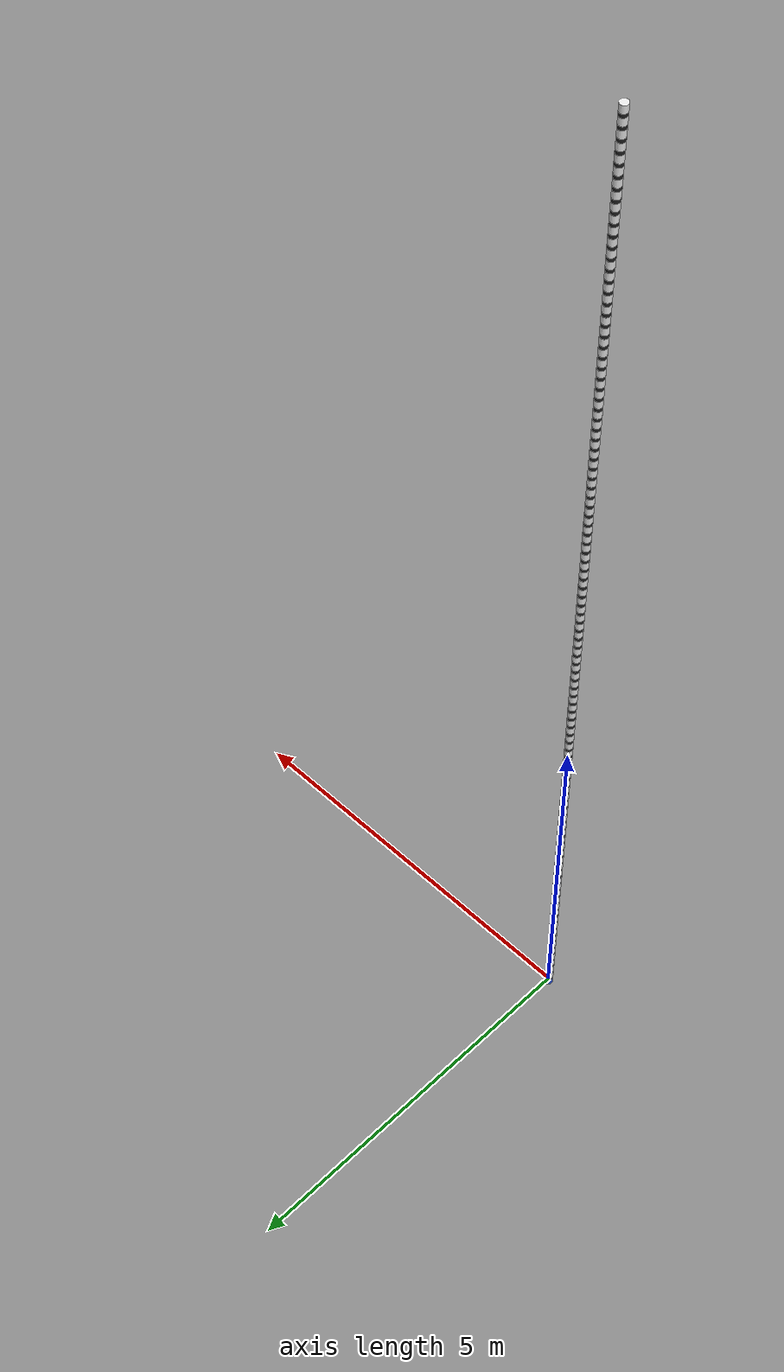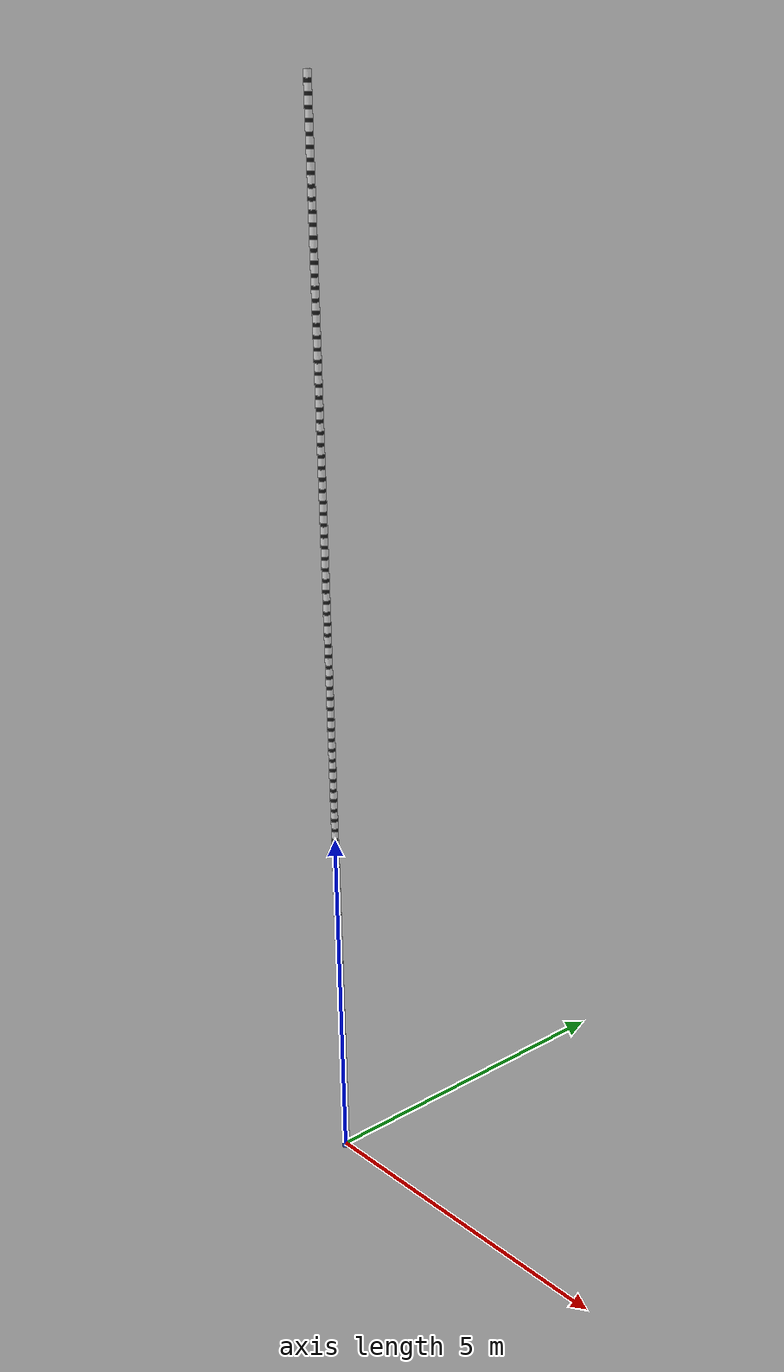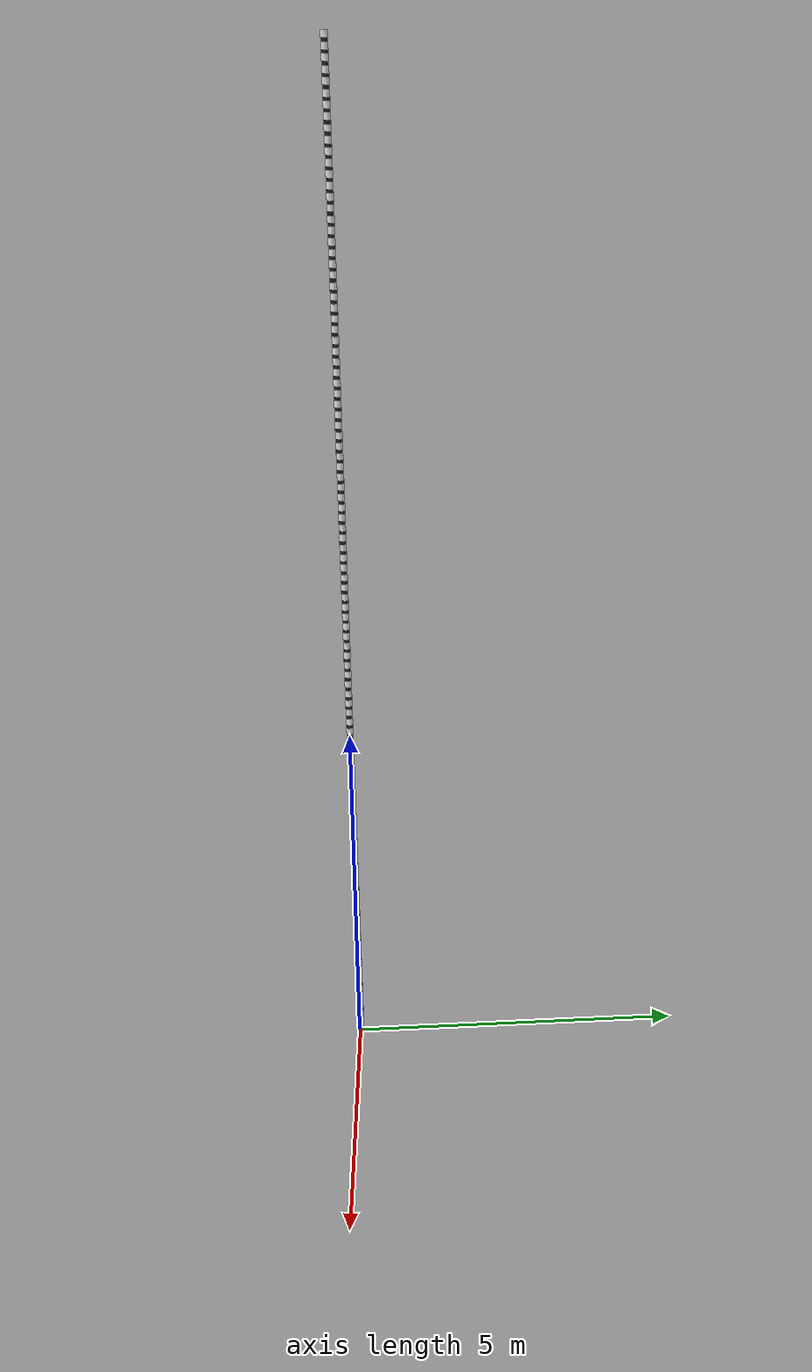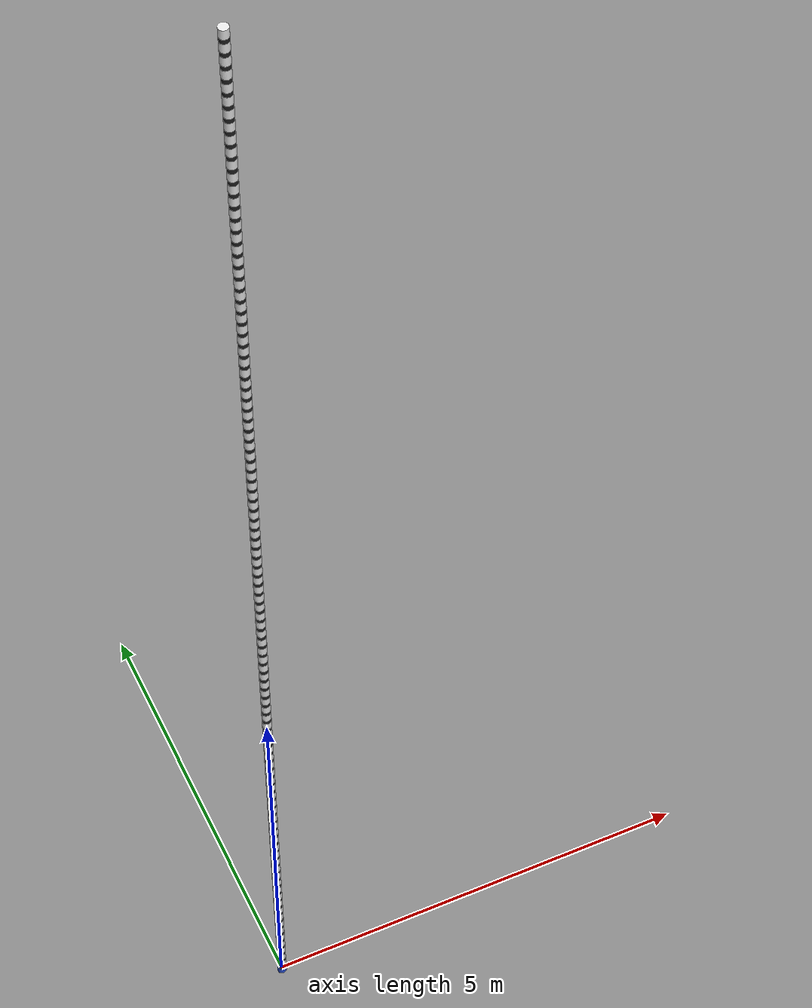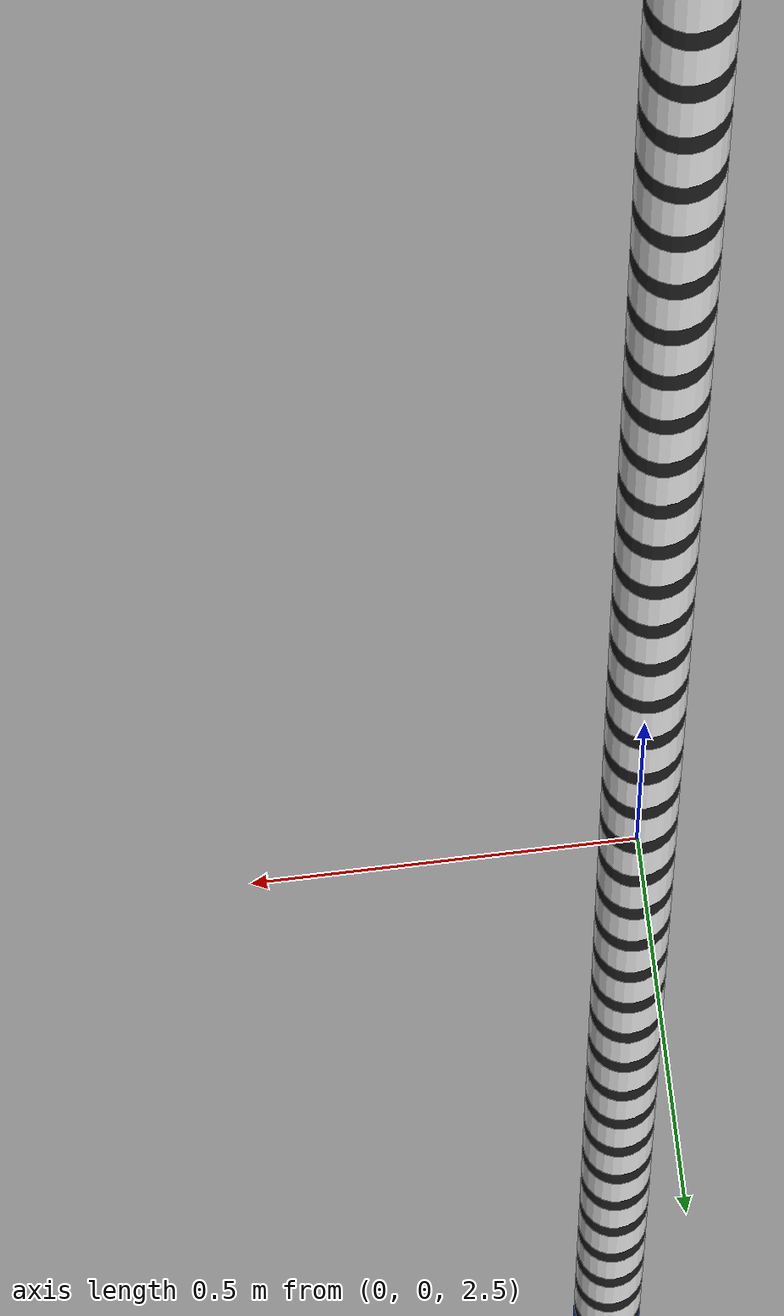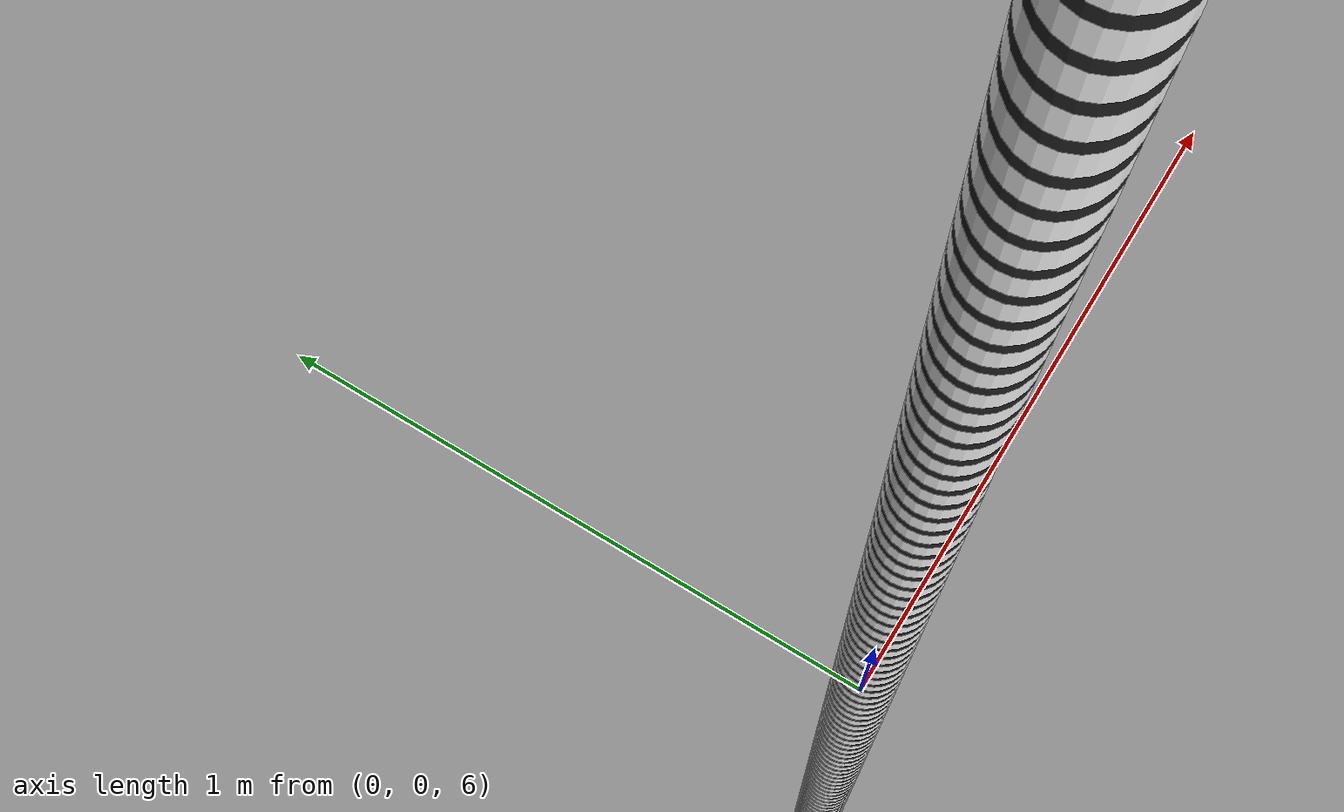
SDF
<?xml version="1.0" ?>
<sdf version="1.5">
  <model name='snake'>

    <link name='body_link_0'>
      <self_collide>1</self_collide>
      <pose>0 0 0 0 -0 0</pose>
      <inertial>
        <pose>0 0 0 0 -0 0</pose>
        <mass>0.5</mass>
        <inertia>
          <ixx>0.0007291666666666668</ixx>
          <ixy>0</ixy>
          <ixz>0</ixz>
          <iyy>0.0007291666666666668</iyy>
          <iyz>0</iyz>
          <izz>0.0006250000000000001</izz>
        </inertia>
      </inertial>
      <collision name='base_link_collision_0'>
        <pose>0 0 0 0 -0 0</pose>
        <geometry>
          <cylinder>
            <length>0.1</length>
            <radius>0.05</radius>
          </cylinder>
        </geometry>
      </collision>
      <visual name='base_link_visual_0'>
        <pose>0 0 0 0 -0 0</pose>
        <geometry>
          <cylinder>
            <length>0.1</length>
            <radius>0.05</radius>
          </cylinder>
        </geometry>
        <material>
          <script>
            <uri>file://media/materials/scripts/gazebo.material</uri>
            <name>Gazebo/Blue</name>
          </script>
        </material>
      </visual>
    </link>

    <link name='aux_body_link_1'>
      <self_collide>1</self_collide>
      <pose>0 0 0.07500000000000001 0 -0 0</pose>
      <inertial>
        <pose>0 0 0 0 -0 0</pose>
        <mass>0.5</mass>
        <inertia>
          <ixx>0.00041666666666666675</ixx>
          <ixy>0</ixy>
          <ixz>0</ixz>
          <iyy>0.00041666666666666675</iyy>
          <iyz>0</iyz>
          <izz>0.0006250000000000001</izz>
        </inertia>
      </inertial>
      <collision name='aux_body_link_1_collision'>
        <pose>0 0 0 0 -0 0</pose>
        <geometry>
          <cylinder>
            <length>0.05</length>
            <radius>0.05</radius>
          </cylinder>
        </geometry>
      </collision>
      <visual name='aux_body_link_1_visual'>
        <pose>0 0 0 0 -0 0</pose>
        <geometry>
          <cylinder>
            <length>0.05</length>
            <radius>0.05</radius>
          </cylinder>
        </geometry>
        <material>
          <script>
            <uri>file://media/materials/scripts/gazebo.material</uri>
            <name>Gazebo/Black</name>
          </script>
        </material>
      </visual>
    </link>

    <joint name='aux_body_link_1_joint' type='revolute'>
        <pose>0 0 -0.025 0 0 0</pose>
      <child>aux_body_link_1</child>
      <parent>body_link_0</parent>
      <axis>
        <xyz>1 0 0</xyz>
        <limit>
          <lower>-0.785398</lower>
          <upper>0.785398</upper>
          <effort>20</effort>
          <velocity>2</velocity>
        </limit>
      </axis>
    </joint>

    <link name='body_link_1'>
      <self_collide>1</self_collide>
      <pose>0 0 0.15000000000000002 0 -0 0</pose>
      <inertial>
        <pose>0 0 0 0 -0 0</pose>
        <mass>0.5</mass>
        <inertia>
          <ixx>0.0007291666666666668</ixx>
          <ixy>0</ixy>
          <ixz>0</ixz>
          <iyy>0.0007291666666666668</iyy>
          <iyz>0</iyz>
          <izz>0.0006250000000000001</izz>
        </inertia>
      </inertial>
      <collision name='body_link_1_collision'>
        <pose>0 0 0 0 -0 0</pose>
        <geometry>
          <cylinder>
            <length>0.1</length>
            <radius>0.05</radius>
          </cylinder>
        </geometry>
      </collision>
      <visual name='body_link_1_visual'>
        <pose>0 0 0 0 -0 0</pose>
        <geometry>
          <cylinder>
            <length>0.1</length>
            <radius>0.05</radius>
          </cylinder>
        </geometry>
        <material>
          <script>
            <uri>file://media/materials/scripts/gazebo.material</uri>
            <name>Gazebo/White</name>
          </script>
        </material>
      </visual>
    </link>

    <joint name='body_link_1_joint' type='revolute'>
        <pose>0 0 -0.05 0 0 0</pose>
      <child>body_link_1</child>
      <parent>aux_body_link_1</parent>
      <axis>
        <xyz>0 1 0</xyz>
        <limit>
          <lower>-0.785398</lower>
          <upper>0.785398</upper>
          <effort>20</effort>
          <velocity>2</velocity>
        </limit>
      </axis>
    </joint>

    <link name='aux_body_link_2'>
      <self_collide>1</self_collide>
      <pose>0 0 0.22500000000000003 0 -0 0</pose>
      <inertial>
        <pose>0 0 0 0 -0 0</pose>
        <mass>0.5</mass>
        <inertia>
          <ixx>0.00041666666666666675</ixx>
          <ixy>0</ixy>
          <ixz>0</ixz>
          <iyy>0.00041666666666666675</iyy>
          <iyz>0</iyz>
          <izz>0.0006250000000000001</izz>
        </inertia>
      </inertial>
      <collision name='aux_body_link_2_collision'>
        <pose>0 0 0 0 -0 0</pose>
        <geometry>
          <cylinder>
            <length>0.05</length>
            <radius>0.05</radius>
          </cylinder>
        </geometry>
      </collision>
      <visual name='aux_body_link_2_visual'>
        <pose>0 0 0 0 -0 0</pose>
        <geometry>
          <cylinder>
            <length>0.05</length>
            <radius>0.05</radius>
          </cylinder>
        </geometry>
        <material>
          <script>
            <uri>file://media/materials/scripts/gazebo.material</uri>
            <name>Gazebo/Black</name>
          </script>
        </material>
      </visual>
    </link>

    <joint name='aux_body_link_2_joint' type='revolute'>
        <pose>0 0 -0.025 0 0 0</pose>
      <child>aux_body_link_2</child>
      <parent>body_link_1</parent>
      <axis>
        <xyz>1 0 0</xyz>
        <limit>
          <lower>-0.785398</lower>
          <upper>0.785398</upper>
          <effort>20</effort>
          <velocity>2</velocity>
        </limit>
      </axis>
    </joint>

    <link name='body_link_2'>
      <self_collide>1</self_collide>
      <pose>0 0 0.30000000000000004 0 -0 0</pose>
      <inertial>
        <pose>0 0 0 0 -0 0</pose>
        <mass>0.5</mass>
        <inertia>
          <ixx>0.0007291666666666668</ixx>
          <ixy>0</ixy>
          <ixz>0</ixz>
          <iyy>0.0007291666666666668</iyy>
          <iyz>0</iyz>
          <izz>0.0006250000000000001</izz>
        </inertia>
      </inertial>
      <collision name='body_link_2_collision'>
        <pose>0 0 0 0 -0 0</pose>
        <geometry>
          <cylinder>
            <length>0.1</length>
            <radius>0.05</radius>
          </cylinder>
        </geometry>
      </collision>
      <visual name='body_link_2_visual'>
        <pose>0 0 0 0 -0 0</pose>
        <geometry>
          <cylinder>
            <length>0.1</length>
            <radius>0.05</radius>
          </cylinder>
        </geometry>
        <material>
          <script>
            <uri>file://media/materials/scripts/gazebo.material</uri>
            <name>Gazebo/White</name>
          </script>
        </material>
      </visual>
    </link>

    <joint name='body_link_2_joint' type='revolute'>
        <pose>0 0 -0.05 0 0 0</pose>
      <child>body_link_2</child>
      <parent>aux_body_link_2</parent>
      <axis>
        <xyz>0 1 0</xyz>
        <limit>
          <lower>-0.785398</lower>
          <upper>0.785398</upper>
          <effort>20</effort>
          <velocity>2</velocity>
        </limit>
      </axis>
    </joint>

    <link name='aux_body_link_3'>
      <self_collide>1</self_collide>
      <pose>0 0 0.37500000000000006 0 -0 0</pose>
      <inertial>
        <pose>0 0 0 0 -0 0</pose>
        <mass>0.5</mass>
        <inertia>
          <ixx>0.00041666666666666675</ixx>
          <ixy>0</ixy>
          <ixz>0</ixz>
          <iyy>0.00041666666666666675</iyy>
          <iyz>0</iyz>
          <izz>0.0006250000000000001</izz>
        </inertia>
      </inertial>
      <collision name='aux_body_link_3_collision'>
        <pose>0 0 0 0 -0 0</pose>
        <geometry>
          <cylinder>
            <length>0.05</length>
            <radius>0.05</radius>
          </cylinder>
        </geometry>
      </collision>
      <visual name='aux_body_link_3_visual'>
        <pose>0 0 0 0 -0 0</pose>
        <geometry>
          <cylinder>
            <length>0.05</length>
            <radius>0.05</radius>
          </cylinder>
        </geometry>
        <material>
          <script>
            <uri>file://media/materials/scripts/gazebo.material</uri>
            <name>Gazebo/Black</name>
          </script>
        </material>
      </visual>
    </link>

    <joint name='aux_body_link_3_joint' type='revolute'>
        <pose>0 0 -0.025 0 0 0</pose>
      <child>aux_body_link_3</child>
      <parent>body_link_2</parent>
      <axis>
        <xyz>1 0 0</xyz>
        <limit>
          <lower>-0.785398</lower>
          <upper>0.785398</upper>
          <effort>20</effort>
          <velocity>2</velocity>
        </limit>
      </axis>
    </joint>

    <link name='body_link_3'>
      <self_collide>1</self_collide>
      <pose>0 0 0.45000000000000007 0 -0 0</pose>
      <inertial>
        <pose>0 0 0 0 -0 0</pose>
        <mass>0.5</mass>
        <inertia>
          <ixx>0.0007291666666666668</ixx>
          <ixy>0</ixy>
          <ixz>0</ixz>
          <iyy>0.0007291666666666668</iyy>
          <iyz>0</iyz>
          <izz>0.0006250000000000001</izz>
        </inertia>
      </inertial>
      <collision name='body_link_3_collision'>
        <pose>0 0 0 0 -0 0</pose>
        <geometry>
          <cylinder>
            <length>0.1</length>
            <radius>0.05</radius>
          </cylinder>
        </geometry>
      </collision>
      <visual name='body_link_3_visual'>
        <pose>0 0 0 0 -0 0</pose>
        <geometry>
          <cylinder>
            <length>0.1</length>
            <radius>0.05</radius>
          </cylinder>
        </geometry>
        <material>
          <script>
            <uri>file://media/materials/scripts/gazebo.material</uri>
            <name>Gazebo/White</name>
          </script>
        </material>
      </visual>
    </link>

    <joint name='body_link_3_joint' type='revolute'>
        <pose>0 0 -0.05 0 0 0</pose>
      <child>body_link_3</child>
      <parent>aux_body_link_3</parent>
      <axis>
        <xyz>0 1 0</xyz>
        <limit>
          <lower>-0.785398</lower>
          <upper>0.785398</upper>
          <effort>20</effort>
          <velocity>2</velocity>
        </limit>
      </axis>
    </joint>

    <link name='aux_body_link_4'>
      <self_collide>1</self_collide>
      <pose>0 0 0.5250000000000001 0 -0 0</pose>
      <inertial>
        <pose>0 0 0 0 -0 0</pose>
        <mass>0.5</mass>
        <inertia>
          <ixx>0.00041666666666666675</ixx>
          <ixy>0</ixy>
          <ixz>0</ixz>
          <iyy>0.00041666666666666675</iyy>
          <iyz>0</iyz>
          <izz>0.0006250000000000001</izz>
        </inertia>
      </inertial>
      <collision name='aux_body_link_4_collision'>
        <pose>0 0 0 0 -0 0</pose>
        <geometry>
          <cylinder>
            <length>0.05</length>
            <radius>0.05</radius>
          </cylinder>
        </geometry>
      </collision>
      <visual name='aux_body_link_4_visual'>
        <pose>0 0 0 0 -0 0</pose>
        <geometry>
          <cylinder>
            <length>0.05</length>
            <radius>0.05</radius>
          </cylinder>
        </geometry>
        <material>
          <script>
            <uri>file://media/materials/scripts/gazebo.material</uri>
            <name>Gazebo/Black</name>
          </script>
        </material>
      </visual>
    </link>

    <joint name='aux_body_link_4_joint' type='revolute'>
        <pose>0 0 -0.025 0 0 0</pose>
      <child>aux_body_link_4</child>
      <parent>body_link_3</parent>
      <axis>
        <xyz>1 0 0</xyz>
        <limit>
          <lower>-0.785398</lower>
          <upper>0.785398</upper>
          <effort>20</effort>
          <velocity>2</velocity>
        </limit>
      </axis>
    </joint>

    <link name='body_link_4'>
      <self_collide>1</self_collide>
      <pose>0 0 0.6000000000000001 0 -0 0</pose>
      <inertial>
        <pose>0 0 0 0 -0 0</pose>
        <mass>0.5</mass>
        <inertia>
          <ixx>0.0007291666666666668</ixx>
          <ixy>0</ixy>
          <ixz>0</ixz>
          <iyy>0.0007291666666666668</iyy>
          <iyz>0</iyz>
          <izz>0.0006250000000000001</izz>
        </inertia>
      </inertial>
      <collision name='body_link_4_collision'>
        <pose>0 0 0 0 -0 0</pose>
        <geometry>
          <cylinder>
            <length>0.1</length>
            <radius>0.05</radius>
          </cylinder>
        </geometry>
      </collision>
      <visual name='body_link_4_visual'>
        <pose>0 0 0 0 -0 0</pose>
        <geometry>
          <cylinder>
            <length>0.1</length>
            <radius>0.05</radius>
          </cylinder>
        </geometry>
        <material>
          <script>
            <uri>file://media/materials/scripts/gazebo.material</uri>
            <name>Gazebo/White</name>
          </script>
        </material>
      </visual>
    </link>

    <joint name='body_link_4_joint' type='revolute'>
        <pose>0 0 -0.05 0 0 0</pose>
      <child>body_link_4</child>
      <parent>aux_body_link_4</parent>
      <axis>
        <xyz>0 1 0</xyz>
        <limit>
          <lower>-0.785398</lower>
          <upper>0.785398</upper>
          <effort>20</effort>
          <velocity>2</velocity>
        </limit>
      </axis>
    </joint>

    <link name='aux_body_link_5'>
      <self_collide>1</self_collide>
      <pose>0 0 0.675 0 -0 0</pose>
      <inertial>
        <pose>0 0 0 0 -0 0</pose>
        <mass>0.5</mass>
        <inertia>
          <ixx>0.00041666666666666675</ixx>
          <ixy>0</ixy>
          <ixz>0</ixz>
          <iyy>0.00041666666666666675</iyy>
          <iyz>0</iyz>
          <izz>0.0006250000000000001</izz>
        </inertia>
      </inertial>
      <collision name='aux_body_link_5_collision'>
        <pose>0 0 0 0 -0 0</pose>
        <geometry>
          <cylinder>
            <length>0.05</length>
            <radius>0.05</radius>
          </cylinder>
        </geometry>
      </collision>
      <visual name='aux_body_link_5_visual'>
        <pose>0 0 0 0 -0 0</pose>
        <geometry>
          <cylinder>
            <length>0.05</length>
            <radius>0.05</radius>
          </cylinder>
        </geometry>
        <material>
          <script>
            <uri>file://media/materials/scripts/gazebo.material</uri>
            <name>Gazebo/Black</name>
          </script>
        </material>
      </visual>
    </link>

    <joint name='aux_body_link_5_joint' type='revolute'>
        <pose>0 0 -0.025 0 0 0</pose>
      <child>aux_body_link_5</child>
      <parent>body_link_4</parent>
      <axis>
        <xyz>1 0 0</xyz>
        <limit>
          <lower>-0.785398</lower>
          <upper>0.785398</upper>
          <effort>20</effort>
          <velocity>2</velocity>
        </limit>
      </axis>
    </joint>

    <link name='body_link_5'>
      <self_collide>1</self_collide>
      <pose>0 0 0.7500000000000001 0 -0 0</pose>
      <inertial>
        <pose>0 0 0 0 -0 0</pose>
        <mass>0.5</mass>
        <inertia>
          <ixx>0.0007291666666666668</ixx>
          <ixy>0</ixy>
          <ixz>0</ixz>
          <iyy>0.0007291666666666668</iyy>
          <iyz>0</iyz>
          <izz>0.0006250000000000001</izz>
        </inertia>
      </inertial>
      <collision name='body_link_5_collision'>
        <pose>0 0 0 0 -0 0</pose>
        <geometry>
          <cylinder>
            <length>0.1</length>
            <radius>0.05</radius>
          </cylinder>
        </geometry>
      </collision>
      <visual name='body_link_5_visual'>
        <pose>0 0 0 0 -0 0</pose>
        <geometry>
          <cylinder>
            <length>0.1</length>
            <radius>0.05</radius>
          </cylinder>
        </geometry>
        <material>
          <script>
            <uri>file://media/materials/scripts/gazebo.material</uri>
            <name>Gazebo/White</name>
          </script>
        </material>
      </visual>
    </link>

    <joint name='body_link_5_joint' type='revolute'>
        <pose>0 0 -0.05 0 0 0</pose>
      <child>body_link_5</child>
      <parent>aux_body_link_5</parent>
      <axis>
        <xyz>0 1 0</xyz>
        <limit>
          <lower>-0.785398</lower>
          <upper>0.785398</upper>
          <effort>20</effort>
          <velocity>2</velocity>
        </limit>
      </axis>
    </joint>

    <link name='aux_body_link_6'>
      <self_collide>1</self_collide>
      <pose>0 0 0.8250000000000002 0 -0 0</pose>
      <inertial>
        <pose>0 0 0 0 -0 0</pose>
        <mass>0.5</mass>
        <inertia>
          <ixx>0.00041666666666666675</ixx>
          <ixy>0</ixy>
          <ixz>0</ixz>
          <iyy>0.00041666666666666675</iyy>
          <iyz>0</iyz>
          <izz>0.0006250000000000001</izz>
        </inertia>
      </inertial>
      <collision name='aux_body_link_6_collision'>
        <pose>0 0 0 0 -0 0</pose>
        <geometry>
          <cylinder>
            <length>0.05</length>
            <radius>0.05</radius>
          </cylinder>
        </geometry>
      </collision>
      <visual name='aux_body_link_6_visual'>
        <pose>0 0 0 0 -0 0</pose>
        <geometry>
          <cylinder>
            <length>0.05</length>
            <radius>0.05</radius>
          </cylinder>
        </geometry>
        <material>
          <script>
            <uri>file://media/materials/scripts/gazebo.material</uri>
            <name>Gazebo/Black</name>
          </script>
        </material>
      </visual>
    </link>

    <joint name='aux_body_link_6_joint' type='revolute'>
        <pose>0 0 -0.025 0 0 0</pose>
      <child>aux_body_link_6</child>
      <parent>body_link_5</parent>
      <axis>
        <xyz>1 0 0</xyz>
        <limit>
          <lower>-0.785398</lower>
          <upper>0.785398</upper>
          <effort>20</effort>
          <velocity>2</velocity>
        </limit>
      </axis>
    </joint>

    <link name='body_link_6'>
      <self_collide>1</self_collide>
      <pose>0 0 0.9000000000000001 0 -0 0</pose>
      <inertial>
        <pose>0 0 0 0 -0 0</pose>
        <mass>0.5</mass>
        <inertia>
          <ixx>0.0007291666666666668</ixx>
          <ixy>0</ixy>
          <ixz>0</ixz>
          <iyy>0.0007291666666666668</iyy>
          <iyz>0</iyz>
          <izz>0.0006250000000000001</izz>
        </inertia>
      </inertial>
      <collision name='body_link_6_collision'>
        <pose>0 0 0 0 -0 0</pose>
        <geometry>
          <cylinder>
            <length>0.1</length>
            <radius>0.05</radius>
          </cylinder>
        </geometry>
      </collision>
      <visual name='body_link_6_visual'>
        <pose>0 0 0 0 -0 0</pose>
        <geometry>
          <cylinder>
            <length>0.1</length>
            <radius>0.05</radius>
          </cylinder>
        </geometry>
        <material>
          <script>
            <uri>file://media/materials/scripts/gazebo.material</uri>
            <name>Gazebo/White</name>
          </script>
        </material>
      </visual>
    </link>

    <joint name='body_link_6_joint' type='revolute'>
        <pose>0 0 -0.05 0 0 0</pose>
      <child>body_link_6</child>
      <parent>aux_body_link_6</parent>
      <axis>
        <xyz>0 1 0</xyz>
        <limit>
          <lower>-0.785398</lower>
          <upper>0.785398</upper>
          <effort>20</effort>
          <velocity>2</velocity>
        </limit>
      </axis>
    </joint>

    <link name='aux_body_link_7'>
      <self_collide>1</self_collide>
      <pose>0 0 0.9750000000000001 0 -0 0</pose>
      <inertial>
        <pose>0 0 0 0 -0 0</pose>
        <mass>0.5</mass>
        <inertia>
          <ixx>0.00041666666666666675</ixx>
          <ixy>0</ixy>
          <ixz>0</ixz>
          <iyy>0.00041666666666666675</iyy>
          <iyz>0</iyz>
          <izz>0.0006250000000000001</izz>
        </inertia>
      </inertial>
      <collision name='aux_body_link_7_collision'>
        <pose>0 0 0 0 -0 0</pose>
        <geometry>
          <cylinder>
            <length>0.05</length>
            <radius>0.05</radius>
          </cylinder>
        </geometry>
      </collision>
      <visual name='aux_body_link_7_visual'>
        <pose>0 0 0 0 -0 0</pose>
        <geometry>
          <cylinder>
            <length>0.05</length>
            <radius>0.05</radius>
          </cylinder>
        </geometry>
        <material>
          <script>
            <uri>file://media/materials/scripts/gazebo.material</uri>
            <name>Gazebo/Black</name>
          </script>
        </material>
      </visual>
    </link>

    <joint name='aux_body_link_7_joint' type='revolute'>
        <pose>0 0 -0.025 0 0 0</pose>
      <child>aux_body_link_7</child>
      <parent>body_link_6</parent>
      <axis>
        <xyz>1 0 0</xyz>
        <limit>
          <lower>-0.785398</lower>
          <upper>0.785398</upper>
          <effort>20</effort>
          <velocity>2</velocity>
        </limit>
      </axis>
    </joint>

    <link name='body_link_7'>
      <self_collide>1</self_collide>
      <pose>0 0 1.0500000000000003 0 -0 0</pose>
      <inertial>
        <pose>0 0 0 0 -0 0</pose>
        <mass>0.5</mass>
        <inertia>
          <ixx>0.0007291666666666668</ixx>
          <ixy>0</ixy>
          <ixz>0</ixz>
          <iyy>0.0007291666666666668</iyy>
          <iyz>0</iyz>
          <izz>0.0006250000000000001</izz>
        </inertia>
      </inertial>
      <collision name='body_link_7_collision'>
        <pose>0 0 0 0 -0 0</pose>
        <geometry>
          <cylinder>
            <length>0.1</length>
            <radius>0.05</radius>
          </cylinder>
        </geometry>
      </collision>
      <visual name='body_link_7_visual'>
        <pose>0 0 0 0 -0 0</pose>
        <geometry>
          <cylinder>
            <length>0.1</length>
            <radius>0.05</radius>
          </cylinder>
        </geometry>
        <material>
          <script>
            <uri>file://media/materials/scripts/gazebo.material</uri>
            <name>Gazebo/White</name>
          </script>
        </material>
      </visual>
    </link>

    <joint name='body_link_7_joint' type='revolute'>
        <pose>0 0 -0.05 0 0 0</pose>
      <child>body_link_7</child>
      <parent>aux_body_link_7</parent>
      <axis>
        <xyz>0 1 0</xyz>
        <limit>
          <lower>-0.785398</lower>
          <upper>0.785398</upper>
          <effort>20</effort>
          <velocity>2</velocity>
        </limit>
      </axis>
    </joint>

    <link name='aux_body_link_8'>
      <self_collide>1</self_collide>
      <pose>0 0 1.1250000000000002 0 -0 0</pose>
      <inertial>
        <pose>0 0 0 0 -0 0</pose>
        <mass>0.5</mass>
        <inertia>
          <ixx>0.00041666666666666675</ixx>
          <ixy>0</ixy>
          <ixz>0</ixz>
          <iyy>0.00041666666666666675</iyy>
          <iyz>0</iyz>
          <izz>0.0006250000000000001</izz>
        </inertia>
      </inertial>
      <collision name='aux_body_link_8_collision'>
        <pose>0 0 0 0 -0 0</pose>
        <geometry>
          <cylinder>
            <length>0.05</length>
            <radius>0.05</radius>
          </cylinder>
        </geometry>
      </collision>
      <visual name='aux_body_link_8_visual'>
        <pose>0 0 0 0 -0 0</pose>
        <geometry>
          <cylinder>
            <length>0.05</length>
            <radius>0.05</radius>
          </cylinder>
        </geometry>
        <material>
          <script>
            <uri>file://media/materials/scripts/gazebo.material</uri>
            <name>Gazebo/Black</name>
          </script>
        </material>
      </visual>
    </link>

    <joint name='aux_body_link_8_joint' type='revolute'>
        <pose>0 0 -0.025 0 0 0</pose>
      <child>aux_body_link_8</child>
      <parent>body_link_7</parent>
      <axis>
        <xyz>1 0 0</xyz>
        <limit>
          <lower>-0.785398</lower>
          <upper>0.785398</upper>
          <effort>20</effort>
          <velocity>2</velocity>
        </limit>
      </axis>
    </joint>

    <link name='body_link_8'>
      <self_collide>1</self_collide>
      <pose>0 0 1.2000000000000002 0 -0 0</pose>
      <inertial>
        <pose>0 0 0 0 -0 0</pose>
        <mass>0.5</mass>
        <inertia>
          <ixx>0.0007291666666666668</ixx>
          <ixy>0</ixy>
          <ixz>0</ixz>
          <iyy>0.0007291666666666668</iyy>
          <iyz>0</iyz>
          <izz>0.0006250000000000001</izz>
        </inertia>
      </inertial>
      <collision name='body_link_8_collision'>
        <pose>0 0 0 0 -0 0</pose>
        <geometry>
          <cylinder>
            <length>0.1</length>
            <radius>0.05</radius>
          </cylinder>
        </geometry>
      </collision>
      <visual name='body_link_8_visual'>
        <pose>0 0 0 0 -0 0</pose>
        <geometry>
          <cylinder>
            <length>0.1</length>
            <radius>0.05</radius>
          </cylinder>
        </geometry>
        <material>
          <script>
            <uri>file://media/materials/scripts/gazebo.material</uri>
            <name>Gazebo/White</name>
          </script>
        </material>
      </visual>
    </link>

    <joint name='body_link_8_joint' type='revolute'>
        <pose>0 0 -0.05 0 0 0</pose>
      <child>body_link_8</child>
      <parent>aux_body_link_8</parent>
      <axis>
        <xyz>0 1 0</xyz>
        <limit>
          <lower>-0.785398</lower>
          <upper>0.785398</upper>
          <effort>20</effort>
          <velocity>2</velocity>
        </limit>
      </axis>
    </joint>

    <link name='aux_body_link_9'>
      <self_collide>1</self_collide>
      <pose>0 0 1.2750000000000001 0 -0 0</pose>
      <inertial>
        <pose>0 0 0 0 -0 0</pose>
        <mass>0.5</mass>
        <inertia>
          <ixx>0.00041666666666666675</ixx>
          <ixy>0</ixy>
          <ixz>0</ixz>
          <iyy>0.00041666666666666675</iyy>
          <iyz>0</iyz>
          <izz>0.0006250000000000001</izz>
        </inertia>
      </inertial>
      <collision name='aux_body_link_9_collision'>
        <pose>0 0 0 0 -0 0</pose>
        <geometry>
          <cylinder>
            <length>0.05</length>
            <radius>0.05</radius>
          </cylinder>
        </geometry>
      </collision>
      <visual name='aux_body_link_9_visual'>
        <pose>0 0 0 0 -0 0</pose>
        <geometry>
          <cylinder>
            <length>0.05</length>
            <radius>0.05</radius>
          </cylinder>
        </geometry>
        <material>
          <script>
            <uri>file://media/materials/scripts/gazebo.material</uri>
            <name>Gazebo/Black</name>
          </script>
        </material>
      </visual>
    </link>

    <joint name='aux_body_link_9_joint' type='revolute'>
        <pose>0 0 -0.025 0 0 0</pose>
      <child>aux_body_link_9</child>
      <parent>body_link_8</parent>
      <axis>
        <xyz>1 0 0</xyz>
        <limit>
          <lower>-0.785398</lower>
          <upper>0.785398</upper>
          <effort>20</effort>
          <velocity>2</velocity>
        </limit>
      </axis>
    </joint>

    <link name='body_link_9'>
      <self_collide>1</self_collide>
      <pose>0 0 1.35 0 -0 0</pose>
      <inertial>
        <pose>0 0 0 0 -0 0</pose>
        <mass>0.5</mass>
        <inertia>
          <ixx>0.0007291666666666668</ixx>
          <ixy>0</ixy>
          <ixz>0</ixz>
          <iyy>0.0007291666666666668</iyy>
          <iyz>0</iyz>
          <izz>0.0006250000000000001</izz>
        </inertia>
      </inertial>
      <collision name='body_link_9_collision'>
        <pose>0 0 0 0 -0 0</pose>
        <geometry>
          <cylinder>
            <length>0.1</length>
            <radius>0.05</radius>
          </cylinder>
        </geometry>
      </collision>
      <visual name='body_link_9_visual'>
        <pose>0 0 0 0 -0 0</pose>
        <geometry>
          <cylinder>
            <length>0.1</length>
            <radius>0.05</radius>
          </cylinder>
        </geometry>
        <material>
          <script>
            <uri>file://media/materials/scripts/gazebo.material</uri>
            <name>Gazebo/White</name>
          </script>
        </material>
      </visual>
    </link>

    <joint name='body_link_9_joint' type='revolute'>
        <pose>0 0 -0.05 0 0 0</pose>
      <child>body_link_9</child>
      <parent>aux_body_link_9</parent>
      <axis>
        <xyz>0 1 0</xyz>
        <limit>
          <lower>-0.785398</lower>
          <upper>0.785398</upper>
          <effort>20</effort>
          <velocity>2</velocity>
        </limit>
      </axis>
    </joint>

    <link name='aux_body_link_10'>
      <self_collide>1</self_collide>
      <pose>0 0 1.4250000000000003 0 -0 0</pose>
      <inertial>
        <pose>0 0 0 0 -0 0</pose>
        <mass>0.5</mass>
        <inertia>
          <ixx>0.00041666666666666675</ixx>
          <ixy>0</ixy>
          <ixz>0</ixz>
          <iyy>0.00041666666666666675</iyy>
          <iyz>0</iyz>
          <izz>0.0006250000000000001</izz>
        </inertia>
      </inertial>
      <collision name='aux_body_link_10_collision'>
        <pose>0 0 0 0 -0 0</pose>
        <geometry>
          <cylinder>
            <length>0.05</length>
            <radius>0.05</radius>
          </cylinder>
        </geometry>
      </collision>
      <visual name='aux_body_link_10_visual'>
        <pose>0 0 0 0 -0 0</pose>
        <geometry>
          <cylinder>
            <length>0.05</length>
            <radius>0.05</radius>
          </cylinder>
        </geometry>
        <material>
          <script>
            <uri>file://media/materials/scripts/gazebo.material</uri>
            <name>Gazebo/Black</name>
          </script>
        </material>
      </visual>
    </link>

    <joint name='aux_body_link_10_joint' type='revolute'>
        <pose>0 0 -0.025 0 0 0</pose>
      <child>aux_body_link_10</child>
      <parent>body_link_9</parent>
      <axis>
        <xyz>1 0 0</xyz>
        <limit>
          <lower>-0.785398</lower>
          <upper>0.785398</upper>
          <effort>20</effort>
          <velocity>2</velocity>
        </limit>
      </axis>
    </joint>

    <link name='body_link_10'>
      <self_collide>1</self_collide>
      <pose>0 0 1.5000000000000002 0 -0 0</pose>
      <inertial>
        <pose>0 0 0 0 -0 0</pose>
        <mass>0.5</mass>
        <inertia>
          <ixx>0.0007291666666666668</ixx>
          <ixy>0</ixy>
          <ixz>0</ixz>
          <iyy>0.0007291666666666668</iyy>
          <iyz>0</iyz>
          <izz>0.0006250000000000001</izz>
        </inertia>
      </inertial>
      <collision name='body_link_10_collision'>
        <pose>0 0 0 0 -0 0</pose>
        <geometry>
          <cylinder>
            <length>0.1</length>
            <radius>0.05</radius>
          </cylinder>
        </geometry>
      </collision>
      <visual name='body_link_10_visual'>
        <pose>0 0 0 0 -0 0</pose>
        <geometry>
          <cylinder>
            <length>0.1</length>
            <radius>0.05</radius>
          </cylinder>
        </geometry>
        <material>
          <script>
            <uri>file://media/materials/scripts/gazebo.material</uri>
            <name>Gazebo/White</name>
          </script>
        </material>
      </visual>
    </link>

    <joint name='body_link_10_joint' type='revolute'>
        <pose>0 0 -0.05 0 0 0</pose>
      <child>body_link_10</child>
      <parent>aux_body_link_10</parent>
      <axis>
        <xyz>0 1 0</xyz>
        <limit>
          <lower>-0.785398</lower>
          <upper>0.785398</upper>
          <effort>20</effort>
          <velocity>2</velocity>
        </limit>
      </axis>
    </joint>

    <link name='aux_body_link_11'>
      <self_collide>1</self_collide>
      <pose>0 0 1.5750000000000002 0 -0 0</pose>
      <inertial>
        <pose>0 0 0 0 -0 0</pose>
        <mass>0.5</mass>
        <inertia>
          <ixx>0.00041666666666666675</ixx>
          <ixy>0</ixy>
          <ixz>0</ixz>
          <iyy>0.00041666666666666675</iyy>
          <iyz>0</iyz>
          <izz>0.0006250000000000001</izz>
        </inertia>
      </inertial>
      <collision name='aux_body_link_11_collision'>
        <pose>0 0 0 0 -0 0</pose>
        <geometry>
          <cylinder>
            <length>0.05</length>
            <radius>0.05</radius>
          </cylinder>
        </geometry>
      </collision>
      <visual name='aux_body_link_11_visual'>
        <pose>0 0 0 0 -0 0</pose>
        <geometry>
          <cylinder>
            <length>0.05</length>
            <radius>0.05</radius>
          </cylinder>
        </geometry>
        <material>
          <script>
            <uri>file://media/materials/scripts/gazebo.material</uri>
            <name>Gazebo/Black</name>
          </script>
        </material>
      </visual>
    </link>

    <joint name='aux_body_link_11_joint' type='revolute'>
        <pose>0 0 -0.025 0 0 0</pose>
      <child>aux_body_link_11</child>
      <parent>body_link_10</parent>
      <axis>
        <xyz>1 0 0</xyz>
        <limit>
          <lower>-0.785398</lower>
          <upper>0.785398</upper>
          <effort>20</effort>
          <velocity>2</velocity>
        </limit>
      </axis>
    </joint>

    <link name='body_link_11'>
      <self_collide>1</self_collide>
      <pose>0 0 1.6500000000000004 0 -0 0</pose>
      <inertial>
        <pose>0 0 0 0 -0 0</pose>
        <mass>0.5</mass>
        <inertia>
          <ixx>0.0007291666666666668</ixx>
          <ixy>0</ixy>
          <ixz>0</ixz>
          <iyy>0.0007291666666666668</iyy>
          <iyz>0</iyz>
          <izz>0.0006250000000000001</izz>
        </inertia>
      </inertial>
      <collision name='body_link_11_collision'>
        <pose>0 0 0 0 -0 0</pose>
        <geometry>
          <cylinder>
            <length>0.1</length>
            <radius>0.05</radius>
          </cylinder>
        </geometry>
      </collision>
      <visual name='body_link_11_visual'>
        <pose>0 0 0 0 -0 0</pose>
        <geometry>
          <cylinder>
            <length>0.1</length>
            <radius>0.05</radius>
          </cylinder>
        </geometry>
        <material>
          <script>
            <uri>file://media/materials/scripts/gazebo.material</uri>
            <name>Gazebo/White</name>
          </script>
        </material>
      </visual>
    </link>

    <joint name='body_link_11_joint' type='revolute'>
        <pose>0 0 -0.05 0 0 0</pose>
      <child>body_link_11</child>
      <parent>aux_body_link_11</parent>
      <axis>
        <xyz>0 1 0</xyz>
        <limit>
          <lower>-0.785398</lower>
          <upper>0.785398</upper>
          <effort>20</effort>
          <velocity>2</velocity>
        </limit>
      </axis>
    </joint>

    <link name='aux_body_link_12'>
      <self_collide>1</self_collide>
      <pose>0 0 1.7250000000000003 0 -0 0</pose>
      <inertial>
        <pose>0 0 0 0 -0 0</pose>
        <mass>0.5</mass>
        <inertia>
          <ixx>0.00041666666666666675</ixx>
          <ixy>0</ixy>
          <ixz>0</ixz>
          <iyy>0.00041666666666666675</iyy>
          <iyz>0</iyz>
          <izz>0.0006250000000000001</izz>
        </inertia>
      </inertial>
      <collision name='aux_body_link_12_collision'>
        <pose>0 0 0 0 -0 0</pose>
        <geometry>
          <cylinder>
            <length>0.05</length>
            <radius>0.05</radius>
          </cylinder>
        </geometry>
      </collision>
      <visual name='aux_body_link_12_visual'>
        <pose>0 0 0 0 -0 0</pose>
        <geometry>
          <cylinder>
            <length>0.05</length>
            <radius>0.05</radius>
          </cylinder>
        </geometry>
        <material>
          <script>
            <uri>file://media/materials/scripts/gazebo.material</uri>
            <name>Gazebo/Black</name>
          </script>
        </material>
      </visual>
    </link>

    <joint name='aux_body_link_12_joint' type='revolute'>
        <pose>0 0 -0.025 0 0 0</pose>
      <child>aux_body_link_12</child>
      <parent>body_link_11</parent>
      <axis>
        <xyz>1 0 0</xyz>
        <limit>
          <lower>-0.785398</lower>
          <upper>0.785398</upper>
          <effort>20</effort>
          <velocity>2</velocity>
        </limit>
      </axis>
    </joint>

    <link name='body_link_12'>
      <self_collide>1</self_collide>
      <pose>0 0 1.8000000000000003 0 -0 0</pose>
      <inertial>
        <pose>0 0 0 0 -0 0</pose>
        <mass>0.5</mass>
        <inertia>
          <ixx>0.0007291666666666668</ixx>
          <ixy>0</ixy>
          <ixz>0</ixz>
          <iyy>0.0007291666666666668</iyy>
          <iyz>0</iyz>
          <izz>0.0006250000000000001</izz>
        </inertia>
      </inertial>
      <collision name='body_link_12_collision'>
        <pose>0 0 0 0 -0 0</pose>
        <geometry>
          <cylinder>
            <length>0.1</length>
            <radius>0.05</radius>
          </cylinder>
        </geometry>
      </collision>
      <visual name='body_link_12_visual'>
        <pose>0 0 0 0 -0 0</pose>
        <geometry>
          <cylinder>
            <length>0.1</length>
            <radius>0.05</radius>
          </cylinder>
        </geometry>
        <material>
          <script>
            <uri>file://media/materials/scripts/gazebo.material</uri>
            <name>Gazebo/White</name>
          </script>
        </material>
      </visual>
    </link>

    <joint name='body_link_12_joint' type='revolute'>
        <pose>0 0 -0.05 0 0 0</pose>
      <child>body_link_12</child>
      <parent>aux_body_link_12</parent>
      <axis>
        <xyz>0 1 0</xyz>
        <limit>
          <lower>-0.785398</lower>
          <upper>0.785398</upper>
          <effort>20</effort>
          <velocity>2</velocity>
        </limit>
      </axis>
    </joint>

    <link name='aux_body_link_13'>
      <self_collide>1</self_collide>
      <pose>0 0 1.8750000000000002 0 -0 0</pose>
      <inertial>
        <pose>0 0 0 0 -0 0</pose>
        <mass>0.5</mass>
        <inertia>
          <ixx>0.00041666666666666675</ixx>
          <ixy>0</ixy>
          <ixz>0</ixz>
          <iyy>0.00041666666666666675</iyy>
          <iyz>0</iyz>
          <izz>0.0006250000000000001</izz>
        </inertia>
      </inertial>
      <collision name='aux_body_link_13_collision'>
        <pose>0 0 0 0 -0 0</pose>
        <geometry>
          <cylinder>
            <length>0.05</length>
            <radius>0.05</radius>
          </cylinder>
        </geometry>
      </collision>
      <visual name='aux_body_link_13_visual'>
        <pose>0 0 0 0 -0 0</pose>
        <geometry>
          <cylinder>
            <length>0.05</length>
            <radius>0.05</radius>
          </cylinder>
        </geometry>
        <material>
          <script>
            <uri>file://media/materials/scripts/gazebo.material</uri>
            <name>Gazebo/Black</name>
          </script>
        </material>
      </visual>
    </link>

    <joint name='aux_body_link_13_joint' type='revolute'>
        <pose>0 0 -0.025 0 0 0</pose>
      <child>aux_body_link_13</child>
      <parent>body_link_12</parent>
      <axis>
        <xyz>1 0 0</xyz>
        <limit>
          <lower>-0.785398</lower>
          <upper>0.785398</upper>
          <effort>20</effort>
          <velocity>2</velocity>
        </limit>
      </axis>
    </joint>

    <link name='body_link_13'>
      <self_collide>1</self_collide>
      <pose>0 0 1.9500000000000002 0 -0 0</pose>
      <inertial>
        <pose>0 0 0 0 -0 0</pose>
        <mass>0.5</mass>
        <inertia>
          <ixx>0.0007291666666666668</ixx>
          <ixy>0</ixy>
          <ixz>0</ixz>
          <iyy>0.0007291666666666668</iyy>
          <iyz>0</iyz>
          <izz>0.0006250000000000001</izz>
        </inertia>
      </inertial>
      <collision name='body_link_13_collision'>
        <pose>0 0 0 0 -0 0</pose>
        <geometry>
          <cylinder>
            <length>0.1</length>
            <radius>0.05</radius>
          </cylinder>
        </geometry>
      </collision>
      <visual name='body_link_13_visual'>
        <pose>0 0 0 0 -0 0</pose>
        <geometry>
          <cylinder>
            <length>0.1</length>
            <radius>0.05</radius>
          </cylinder>
        </geometry>
        <material>
          <script>
            <uri>file://media/materials/scripts/gazebo.material</uri>
            <name>Gazebo/White</name>
          </script>
        </material>
      </visual>
    </link>

    <joint name='body_link_13_joint' type='revolute'>
        <pose>0 0 -0.05 0 0 0</pose>
      <child>body_link_13</child>
      <parent>aux_body_link_13</parent>
      <axis>
        <xyz>0 1 0</xyz>
        <limit>
          <lower>-0.785398</lower>
          <upper>0.785398</upper>
          <effort>20</effort>
          <velocity>2</velocity>
        </limit>
      </axis>
    </joint>

    <link name='aux_body_link_14'>
      <self_collide>1</self_collide>
      <pose>0 0 2.0250000000000004 0 -0 0</pose>
      <inertial>
        <pose>0 0 0 0 -0 0</pose>
        <mass>0.5</mass>
        <inertia>
          <ixx>0.00041666666666666675</ixx>
          <ixy>0</ixy>
          <ixz>0</ixz>
          <iyy>0.00041666666666666675</iyy>
          <iyz>0</iyz>
          <izz>0.0006250000000000001</izz>
        </inertia>
      </inertial>
      <collision name='aux_body_link_14_collision'>
        <pose>0 0 0 0 -0 0</pose>
        <geometry>
          <cylinder>
            <length>0.05</length>
            <radius>0.05</radius>
          </cylinder>
        </geometry>
      </collision>
      <visual name='aux_body_link_14_visual'>
        <pose>0 0 0 0 -0 0</pose>
        <geometry>
          <cylinder>
            <length>0.05</length>
            <radius>0.05</radius>
          </cylinder>
        </geometry>
        <material>
          <script>
            <uri>file://media/materials/scripts/gazebo.material</uri>
            <name>Gazebo/Black</name>
          </script>
        </material>
      </visual>
    </link>

    <joint name='aux_body_link_14_joint' type='revolute'>
        <pose>0 0 -0.025 0 0 0</pose>
      <child>aux_body_link_14</child>
      <parent>body_link_13</parent>
      <axis>
        <xyz>1 0 0</xyz>
        <limit>
          <lower>-0.785398</lower>
          <upper>0.785398</upper>
          <effort>20</effort>
          <velocity>2</velocity>
        </limit>
      </axis>
    </joint>

    <link name='body_link_14'>
      <self_collide>1</self_collide>
      <pose>0 0 2.1000000000000005 0 -0 0</pose>
      <inertial>
        <pose>0 0 0 0 -0 0</pose>
        <mass>0.5</mass>
        <inertia>
          <ixx>0.0007291666666666668</ixx>
          <ixy>0</ixy>
          <ixz>0</ixz>
          <iyy>0.0007291666666666668</iyy>
          <iyz>0</iyz>
          <izz>0.0006250000000000001</izz>
        </inertia>
      </inertial>
      <collision name='body_link_14_collision'>
        <pose>0 0 0 0 -0 0</pose>
        <geometry>
          <cylinder>
            <length>0.1</length>
            <radius>0.05</radius>
          </cylinder>
        </geometry>
      </collision>
      <visual name='body_link_14_visual'>
        <pose>0 0 0 0 -0 0</pose>
        <geometry>
          <cylinder>
            <length>0.1</length>
            <radius>0.05</radius>
          </cylinder>
        </geometry>
        <material>
          <script>
            <uri>file://media/materials/scripts/gazebo.material</uri>
            <name>Gazebo/White</name>
          </script>
        </material>
      </visual>
    </link>

    <joint name='body_link_14_joint' type='revolute'>
        <pose>0 0 -0.05 0 0 0</pose>
      <child>body_link_14</child>
      <parent>aux_body_link_14</parent>
      <axis>
        <xyz>0 1 0</xyz>
        <limit>
          <lower>-0.785398</lower>
          <upper>0.785398</upper>
          <effort>20</effort>
          <velocity>2</velocity>
        </limit>
      </axis>
    </joint>

    <link name='aux_body_link_15'>
      <self_collide>1</self_collide>
      <pose>0 0 2.1750000000000003 0 -0 0</pose>
      <inertial>
        <pose>0 0 0 0 -0 0</pose>
        <mass>0.5</mass>
        <inertia>
          <ixx>0.00041666666666666675</ixx>
          <ixy>0</ixy>
          <ixz>0</ixz>
          <iyy>0.00041666666666666675</iyy>
          <iyz>0</iyz>
          <izz>0.0006250000000000001</izz>
        </inertia>
      </inertial>
      <collision name='aux_body_link_15_collision'>
        <pose>0 0 0 0 -0 0</pose>
        <geometry>
          <cylinder>
            <length>0.05</length>
            <radius>0.05</radius>
          </cylinder>
        </geometry>
      </collision>
      <visual name='aux_body_link_15_visual'>
        <pose>0 0 0 0 -0 0</pose>
        <geometry>
          <cylinder>
            <length>0.05</length>
            <radius>0.05</radius>
          </cylinder>
        </geometry>
        <material>
          <script>
            <uri>file://media/materials/scripts/gazebo.material</uri>
            <name>Gazebo/Black</name>
          </script>
        </material>
      </visual>
    </link>

    <joint name='aux_body_link_15_joint' type='revolute'>
        <pose>0 0 -0.025 0 0 0</pose>
      <child>aux_body_link_15</child>
      <parent>body_link_14</parent>
      <axis>
        <xyz>1 0 0</xyz>
        <limit>
          <lower>-0.785398</lower>
          <upper>0.785398</upper>
          <effort>20</effort>
          <velocity>2</velocity>
        </limit>
      </axis>
    </joint>

    <link name='body_link_15'>
      <self_collide>1</self_collide>
      <pose>0 0 2.2500000000000004 0 -0 0</pose>
      <inertial>
        <pose>0 0 0 0 -0 0</pose>
        <mass>0.5</mass>
        <inertia>
          <ixx>0.0007291666666666668</ixx>
          <ixy>0</ixy>
          <ixz>0</ixz>
          <iyy>0.0007291666666666668</iyy>
          <iyz>0</iyz>
          <izz>0.0006250000000000001</izz>
        </inertia>
      </inertial>
      <collision name='body_link_15_collision'>
        <pose>0 0 0 0 -0 0</pose>
        <geometry>
          <cylinder>
            <length>0.1</length>
            <radius>0.05</radius>
          </cylinder>
        </geometry>
      </collision>
      <visual name='body_link_15_visual'>
        <pose>0 0 0 0 -0 0</pose>
        <geometry>
          <cylinder>
            <length>0.1</length>
            <radius>0.05</radius>
          </cylinder>
        </geometry>
        <material>
          <script>
            <uri>file://media/materials/scripts/gazebo.material</uri>
            <name>Gazebo/White</name>
          </script>
        </material>
      </visual>
    </link>

    <joint name='body_link_15_joint' type='revolute'>
        <pose>0 0 -0.05 0 0 0</pose>
      <child>body_link_15</child>
      <parent>aux_body_link_15</parent>
      <axis>
        <xyz>0 1 0</xyz>
        <limit>
          <lower>-0.785398</lower>
          <upper>0.785398</upper>
          <effort>20</effort>
          <velocity>2</velocity>
        </limit>
      </axis>
    </joint>

    <link name='aux_body_link_16'>
      <self_collide>1</self_collide>
      <pose>0 0 2.325 0 -0 0</pose>
      <inertial>
        <pose>0 0 0 0 -0 0</pose>
        <mass>0.5</mass>
        <inertia>
          <ixx>0.00041666666666666675</ixx>
          <ixy>0</ixy>
          <ixz>0</ixz>
          <iyy>0.00041666666666666675</iyy>
          <iyz>0</iyz>
          <izz>0.0006250000000000001</izz>
        </inertia>
      </inertial>
      <collision name='aux_body_link_16_collision'>
        <pose>0 0 0 0 -0 0</pose>
        <geometry>
          <cylinder>
            <length>0.05</length>
            <radius>0.05</radius>
          </cylinder>
        </geometry>
      </collision>
      <visual name='aux_body_link_16_visual'>
        <pose>0 0 0 0 -0 0</pose>
        <geometry>
          <cylinder>
            <length>0.05</length>
            <radius>0.05</radius>
          </cylinder>
        </geometry>
        <material>
          <script>
            <uri>file://media/materials/scripts/gazebo.material</uri>
            <name>Gazebo/Black</name>
          </script>
        </material>
      </visual>
    </link>

    <joint name='aux_body_link_16_joint' type='revolute'>
        <pose>0 0 -0.025 0 0 0</pose>
      <child>aux_body_link_16</child>
      <parent>body_link_15</parent>
      <axis>
        <xyz>1 0 0</xyz>
        <limit>
          <lower>-0.785398</lower>
          <upper>0.785398</upper>
          <effort>20</effort>
          <velocity>2</velocity>
        </limit>
      </axis>
    </joint>

    <link name='body_link_16'>
      <self_collide>1</self_collide>
      <pose>0 0 2.4000000000000004 0 -0 0</pose>
      <inertial>
        <pose>0 0 0 0 -0 0</pose>
        <mass>0.5</mass>
        <inertia>
          <ixx>0.0007291666666666668</ixx>
          <ixy>0</ixy>
          <ixz>0</ixz>
          <iyy>0.0007291666666666668</iyy>
          <iyz>0</iyz>
          <izz>0.0006250000000000001</izz>
        </inertia>
      </inertial>
      <collision name='body_link_16_collision'>
        <pose>0 0 0 0 -0 0</pose>
        <geometry>
          <cylinder>
            <length>0.1</length>
            <radius>0.05</radius>
          </cylinder>
        </geometry>
      </collision>
      <visual name='body_link_16_visual'>
        <pose>0 0 0 0 -0 0</pose>
        <geometry>
          <cylinder>
            <length>0.1</length>
            <radius>0.05</radius>
          </cylinder>
        </geometry>
        <material>
          <script>
            <uri>file://media/materials/scripts/gazebo.material</uri>
            <name>Gazebo/White</name>
          </script>
        </material>
      </visual>
    </link>

    <joint name='body_link_16_joint' type='revolute'>
        <pose>0 0 -0.05 0 0 0</pose>
      <child>body_link_16</child>
      <parent>aux_body_link_16</parent>
      <axis>
        <xyz>0 1 0</xyz>
        <limit>
          <lower>-0.785398</lower>
          <upper>0.785398</upper>
          <effort>20</effort>
          <velocity>2</velocity>
        </limit>
      </axis>
    </joint>

    <link name='aux_body_link_17'>
      <self_collide>1</self_collide>
      <pose>0 0 2.4750000000000005 0 -0 0</pose>
      <inertial>
        <pose>0 0 0 0 -0 0</pose>
        <mass>0.5</mass>
        <inertia>
          <ixx>0.00041666666666666675</ixx>
          <ixy>0</ixy>
          <ixz>0</ixz>
          <iyy>0.00041666666666666675</iyy>
          <iyz>0</iyz>
          <izz>0.0006250000000000001</izz>
        </inertia>
      </inertial>
      <collision name='aux_body_link_17_collision'>
        <pose>0 0 0 0 -0 0</pose>
        <geometry>
          <cylinder>
            <length>0.05</length>
            <radius>0.05</radius>
          </cylinder>
        </geometry>
      </collision>
      <visual name='aux_body_link_17_visual'>
        <pose>0 0 0 0 -0 0</pose>
        <geometry>
          <cylinder>
            <length>0.05</length>
            <radius>0.05</radius>
          </cylinder>
        </geometry>
        <material>
          <script>
            <uri>file://media/materials/scripts/gazebo.material</uri>
            <name>Gazebo/Black</name>
          </script>
        </material>
      </visual>
    </link>

    <joint name='aux_body_link_17_joint' type='revolute'>
        <pose>0 0 -0.025 0 0 0</pose>
      <child>aux_body_link_17</child>
      <parent>body_link_16</parent>
      <axis>
        <xyz>1 0 0</xyz>
        <limit>
          <lower>-0.785398</lower>
          <upper>0.785398</upper>
          <effort>20</effort>
          <velocity>2</velocity>
        </limit>
      </axis>
    </joint>

    <link name='body_link_17'>
      <self_collide>1</self_collide>
      <pose>0 0 2.5500000000000003 0 -0 0</pose>
      <inertial>
        <pose>0 0 0 0 -0 0</pose>
        <mass>0.5</mass>
        <inertia>
          <ixx>0.0007291666666666668</ixx>
          <ixy>0</ixy>
          <ixz>0</ixz>
          <iyy>0.0007291666666666668</iyy>
          <iyz>0</iyz>
          <izz>0.0006250000000000001</izz>
        </inertia>
      </inertial>
      <collision name='body_link_17_collision'>
        <pose>0 0 0 0 -0 0</pose>
        <geometry>
          <cylinder>
            <length>0.1</length>
            <radius>0.05</radius>
          </cylinder>
        </geometry>
      </collision>
      <visual name='body_link_17_visual'>
        <pose>0 0 0 0 -0 0</pose>
        <geometry>
          <cylinder>
            <length>0.1</length>
            <radius>0.05</radius>
          </cylinder>
        </geometry>
        <material>
          <script>
            <uri>file://media/materials/scripts/gazebo.material</uri>
            <name>Gazebo/White</name>
          </script>
        </material>
      </visual>
    </link>

    <joint name='body_link_17_joint' type='revolute'>
        <pose>0 0 -0.05 0 0 0</pose>
      <child>body_link_17</child>
      <parent>aux_body_link_17</parent>
      <axis>
        <xyz>0 1 0</xyz>
        <limit>
          <lower>-0.785398</lower>
          <upper>0.785398</upper>
          <effort>20</effort>
          <velocity>2</velocity>
        </limit>
      </axis>
    </joint>

    <link name='aux_body_link_18'>
      <self_collide>1</self_collide>
      <pose>0 0 2.6250000000000004 0 -0 0</pose>
      <inertial>
        <pose>0 0 0 0 -0 0</pose>
        <mass>0.5</mass>
        <inertia>
          <ixx>0.00041666666666666675</ixx>
          <ixy>0</ixy>
          <ixz>0</ixz>
          <iyy>0.00041666666666666675</iyy>
          <iyz>0</iyz>
          <izz>0.0006250000000000001</izz>
        </inertia>
      </inertial>
      <collision name='aux_body_link_18_collision'>
        <pose>0 0 0 0 -0 0</pose>
        <geometry>
          <cylinder>
            <length>0.05</length>
            <radius>0.05</radius>
          </cylinder>
        </geometry>
      </collision>
      <visual name='aux_body_link_18_visual'>
        <pose>0 0 0 0 -0 0</pose>
        <geometry>
          <cylinder>
            <length>0.05</length>
            <radius>0.05</radius>
          </cylinder>
        </geometry>
        <material>
          <script>
            <uri>file://media/materials/scripts/gazebo.material</uri>
            <name>Gazebo/Black</name>
          </script>
        </material>
      </visual>
    </link>

    <joint name='aux_body_link_18_joint' type='revolute'>
        <pose>0 0 -0.025 0 0 0</pose>
      <child>aux_body_link_18</child>
      <parent>body_link_17</parent>
      <axis>
        <xyz>1 0 0</xyz>
        <limit>
          <lower>-0.785398</lower>
          <upper>0.785398</upper>
          <effort>20</effort>
          <velocity>2</velocity>
        </limit>
      </axis>
    </joint>

    <link name='body_link_18'>
      <self_collide>1</self_collide>
      <pose>0 0 2.7 0 -0 0</pose>
      <inertial>
        <pose>0 0 0 0 -0 0</pose>
        <mass>0.5</mass>
        <inertia>
          <ixx>0.0007291666666666668</ixx>
          <ixy>0</ixy>
          <ixz>0</ixz>
          <iyy>0.0007291666666666668</iyy>
          <iyz>0</iyz>
          <izz>0.0006250000000000001</izz>
        </inertia>
      </inertial>
      <collision name='body_link_18_collision'>
        <pose>0 0 0 0 -0 0</pose>
        <geometry>
          <cylinder>
            <length>0.1</length>
            <radius>0.05</radius>
          </cylinder>
        </geometry>
      </collision>
      <visual name='body_link_18_visual'>
        <pose>0 0 0 0 -0 0</pose>
        <geometry>
          <cylinder>
            <length>0.1</length>
            <radius>0.05</radius>
          </cylinder>
        </geometry>
        <material>
          <script>
            <uri>file://media/materials/scripts/gazebo.material</uri>
            <name>Gazebo/White</name>
          </script>
        </material>
      </visual>
    </link>

    <joint name='body_link_18_joint' type='revolute'>
        <pose>0 0 -0.05 0 0 0</pose>
      <child>body_link_18</child>
      <parent>aux_body_link_18</parent>
      <axis>
        <xyz>0 1 0</xyz>
        <limit>
          <lower>-0.785398</lower>
          <upper>0.785398</upper>
          <effort>20</effort>
          <velocity>2</velocity>
        </limit>
      </axis>
    </joint>

    <link name='aux_body_link_19'>
      <self_collide>1</self_collide>
      <pose>0 0 2.7750000000000004 0 -0 0</pose>
      <inertial>
        <pose>0 0 0 0 -0 0</pose>
        <mass>0.5</mass>
        <inertia>
          <ixx>0.00041666666666666675</ixx>
          <ixy>0</ixy>
          <ixz>0</ixz>
          <iyy>0.00041666666666666675</iyy>
          <iyz>0</iyz>
          <izz>0.0006250000000000001</izz>
        </inertia>
      </inertial>
      <collision name='aux_body_link_19_collision'>
        <pose>0 0 0 0 -0 0</pose>
        <geometry>
          <cylinder>
            <length>0.05</length>
            <radius>0.05</radius>
          </cylinder>
        </geometry>
      </collision>
      <visual name='aux_body_link_19_visual'>
        <pose>0 0 0 0 -0 0</pose>
        <geometry>
          <cylinder>
            <length>0.05</length>
            <radius>0.05</radius>
          </cylinder>
        </geometry>
        <material>
          <script>
            <uri>file://media/materials/scripts/gazebo.material</uri>
            <name>Gazebo/Black</name>
          </script>
        </material>
      </visual>
    </link>

    <joint name='aux_body_link_19_joint' type='revolute'>
        <pose>0 0 -0.025 0 0 0</pose>
      <child>aux_body_link_19</child>
      <parent>body_link_18</parent>
      <axis>
        <xyz>1 0 0</xyz>
        <limit>
          <lower>-0.785398</lower>
          <upper>0.785398</upper>
          <effort>20</effort>
          <velocity>2</velocity>
        </limit>
      </axis>
    </joint>

    <link name='body_link_19'>
      <self_collide>1</self_collide>
      <pose>0 0 2.8500000000000005 0 -0 0</pose>
      <inertial>
        <pose>0 0 0 0 -0 0</pose>
        <mass>0.5</mass>
        <inertia>
          <ixx>0.0007291666666666668</ixx>
          <ixy>0</ixy>
          <ixz>0</ixz>
          <iyy>0.0007291666666666668</iyy>
          <iyz>0</iyz>
          <izz>0.0006250000000000001</izz>
        </inertia>
      </inertial>
      <collision name='body_link_19_collision'>
        <pose>0 0 0 0 -0 0</pose>
        <geometry>
          <cylinder>
            <length>0.1</length>
            <radius>0.05</radius>
          </cylinder>
        </geometry>
      </collision>
      <visual name='body_link_19_visual'>
        <pose>0 0 0 0 -0 0</pose>
        <geometry>
          <cylinder>
            <length>0.1</length>
            <radius>0.05</radius>
          </cylinder>
        </geometry>
        <material>
          <script>
            <uri>file://media/materials/scripts/gazebo.material</uri>
            <name>Gazebo/White</name>
          </script>
        </material>
      </visual>
    </link>

    <joint name='body_link_19_joint' type='revolute'>
        <pose>0 0 -0.05 0 0 0</pose>
      <child>body_link_19</child>
      <parent>aux_body_link_19</parent>
      <axis>
        <xyz>0 1 0</xyz>
        <limit>
          <lower>-0.785398</lower>
          <upper>0.785398</upper>
          <effort>20</effort>
          <velocity>2</velocity>
        </limit>
      </axis>
    </joint>

    <link name='aux_body_link_20'>
      <self_collide>1</self_collide>
      <pose>0 0 2.9250000000000003 0 -0 0</pose>
      <inertial>
        <pose>0 0 0 0 -0 0</pose>
        <mass>0.5</mass>
        <inertia>
          <ixx>0.00041666666666666675</ixx>
          <ixy>0</ixy>
          <ixz>0</ixz>
          <iyy>0.00041666666666666675</iyy>
          <iyz>0</iyz>
          <izz>0.0006250000000000001</izz>
        </inertia>
      </inertial>
      <collision name='aux_body_link_20_collision'>
        <pose>0 0 0 0 -0 0</pose>
        <geometry>
          <cylinder>
            <length>0.05</length>
            <radius>0.05</radius>
          </cylinder>
        </geometry>
      </collision>
      <visual name='aux_body_link_20_visual'>
        <pose>0 0 0 0 -0 0</pose>
        <geometry>
          <cylinder>
            <length>0.05</length>
            <radius>0.05</radius>
          </cylinder>
        </geometry>
        <material>
          <script>
            <uri>file://media/materials/scripts/gazebo.material</uri>
            <name>Gazebo/Black</name>
          </script>
        </material>
      </visual>
    </link>

    <joint name='aux_body_link_20_joint' type='revolute'>
        <pose>0 0 -0.025 0 0 0</pose>
      <child>aux_body_link_20</child>
      <parent>body_link_19</parent>
      <axis>
        <xyz>1 0 0</xyz>
        <limit>
          <lower>-0.785398</lower>
          <upper>0.785398</upper>
          <effort>20</effort>
          <velocity>2</velocity>
        </limit>
      </axis>
    </joint>

    <link name='body_link_20'>
      <self_collide>1</self_collide>
      <pose>0 0 3.0000000000000004 0 -0 0</pose>
      <inertial>
        <pose>0 0 0 0 -0 0</pose>
        <mass>0.5</mass>
        <inertia>
          <ixx>0.0007291666666666668</ixx>
          <ixy>0</ixy>
          <ixz>0</ixz>
          <iyy>0.0007291666666666668</iyy>
          <iyz>0</iyz>
          <izz>0.0006250000000000001</izz>
        </inertia>
      </inertial>
      <collision name='body_link_20_collision'>
        <pose>0 0 0 0 -0 0</pose>
        <geometry>
          <cylinder>
            <length>0.1</length>
            <radius>0.05</radius>
          </cylinder>
        </geometry>
      </collision>
      <visual name='body_link_20_visual'>
        <pose>0 0 0 0 -0 0</pose>
        <geometry>
          <cylinder>
            <length>0.1</length>
            <radius>0.05</radius>
          </cylinder>
        </geometry>
        <material>
          <script>
            <uri>file://media/materials/scripts/gazebo.material</uri>
            <name>Gazebo/White</name>
          </script>
        </material>
      </visual>
    </link>

    <joint name='body_link_20_joint' type='revolute'>
        <pose>0 0 -0.05 0 0 0</pose>
      <child>body_link_20</child>
      <parent>aux_body_link_20</parent>
      <axis>
        <xyz>0 1 0</xyz>
        <limit>
          <lower>-0.785398</lower>
          <upper>0.785398</upper>
          <effort>20</effort>
          <velocity>2</velocity>
        </limit>
      </axis>
    </joint>

    <link name='aux_body_link_21'>
      <self_collide>1</self_collide>
      <pose>0 0 3.0750000000000006 0 -0 0</pose>
      <inertial>
        <pose>0 0 0 0 -0 0</pose>
        <mass>0.5</mass>
        <inertia>
          <ixx>0.00041666666666666675</ixx>
          <ixy>0</ixy>
          <ixz>0</ixz>
          <iyy>0.00041666666666666675</iyy>
          <iyz>0</iyz>
          <izz>0.0006250000000000001</izz>
        </inertia>
      </inertial>
      <collision name='aux_body_link_21_collision'>
        <pose>0 0 0 0 -0 0</pose>
        <geometry>
          <cylinder>
            <length>0.05</length>
            <radius>0.05</radius>
          </cylinder>
        </geometry>
      </collision>
      <visual name='aux_body_link_21_visual'>
        <pose>0 0 0 0 -0 0</pose>
        <geometry>
          <cylinder>
            <length>0.05</length>
            <radius>0.05</radius>
          </cylinder>
        </geometry>
        <material>
          <script>
            <uri>file://media/materials/scripts/gazebo.material</uri>
            <name>Gazebo/Black</name>
          </script>
        </material>
      </visual>
    </link>

    <joint name='aux_body_link_21_joint' type='revolute'>
        <pose>0 0 -0.025 0 0 0</pose>
      <child>aux_body_link_21</child>
      <parent>body_link_20</parent>
      <axis>
        <xyz>1 0 0</xyz>
        <limit>
          <lower>-0.785398</lower>
          <upper>0.785398</upper>
          <effort>20</effort>
          <velocity>2</velocity>
        </limit>
      </axis>
    </joint>

    <link name='body_link_21'>
      <self_collide>1</self_collide>
      <pose>0 0 3.1500000000000004 0 -0 0</pose>
      <inertial>
        <pose>0 0 0 0 -0 0</pose>
        <mass>0.5</mass>
        <inertia>
          <ixx>0.0007291666666666668</ixx>
          <ixy>0</ixy>
          <ixz>0</ixz>
          <iyy>0.0007291666666666668</iyy>
          <iyz>0</iyz>
          <izz>0.0006250000000000001</izz>
        </inertia>
      </inertial>
      <collision name='body_link_21_collision'>
        <pose>0 0 0 0 -0 0</pose>
        <geometry>
          <cylinder>
            <length>0.1</length>
            <radius>0.05</radius>
          </cylinder>
        </geometry>
      </collision>
      <visual name='body_link_21_visual'>
        <pose>0 0 0 0 -0 0</pose>
        <geometry>
          <cylinder>
            <length>0.1</length>
            <radius>0.05</radius>
          </cylinder>
        </geometry>
        <material>
          <script>
            <uri>file://media/materials/scripts/gazebo.material</uri>
            <name>Gazebo/White</name>
          </script>
        </material>
      </visual>
    </link>

    <joint name='body_link_21_joint' type='revolute'>
        <pose>0 0 -0.05 0 0 0</pose>
      <child>body_link_21</child>
      <parent>aux_body_link_21</parent>
      <axis>
        <xyz>0 1 0</xyz>
        <limit>
          <lower>-0.785398</lower>
          <upper>0.785398</upper>
          <effort>20</effort>
          <velocity>2</velocity>
        </limit>
      </axis>
    </joint>

    <link name='aux_body_link_22'>
      <self_collide>1</self_collide>
      <pose>0 0 3.2250000000000005 0 -0 0</pose>
      <inertial>
        <pose>0 0 0 0 -0 0</pose>
        <mass>0.5</mass>
        <inertia>
          <ixx>0.00041666666666666675</ixx>
          <ixy>0</ixy>
          <ixz>0</ixz>
          <iyy>0.00041666666666666675</iyy>
          <iyz>0</iyz>
          <izz>0.0006250000000000001</izz>
        </inertia>
      </inertial>
      <collision name='aux_body_link_22_collision'>
        <pose>0 0 0 0 -0 0</pose>
        <geometry>
          <cylinder>
            <length>0.05</length>
            <radius>0.05</radius>
          </cylinder>
        </geometry>
      </collision>
      <visual name='aux_body_link_22_visual'>
        <pose>0 0 0 0 -0 0</pose>
        <geometry>
          <cylinder>
            <length>0.05</length>
            <radius>0.05</radius>
          </cylinder>
        </geometry>
        <material>
          <script>
            <uri>file://media/materials/scripts/gazebo.material</uri>
            <name>Gazebo/Black</name>
          </script>
        </material>
      </visual>
    </link>

    <joint name='aux_body_link_22_joint' type='revolute'>
        <pose>0 0 -0.025 0 0 0</pose>
      <child>aux_body_link_22</child>
      <parent>body_link_21</parent>
      <axis>
        <xyz>1 0 0</xyz>
        <limit>
          <lower>-0.785398</lower>
          <upper>0.785398</upper>
          <effort>20</effort>
          <velocity>2</velocity>
        </limit>
      </axis>
    </joint>

    <link name='body_link_22'>
      <self_collide>1</self_collide>
      <pose>0 0 3.3000000000000007 0 -0 0</pose>
      <inertial>
        <pose>0 0 0 0 -0 0</pose>
        <mass>0.5</mass>
        <inertia>
          <ixx>0.0007291666666666668</ixx>
          <ixy>0</ixy>
          <ixz>0</ixz>
          <iyy>0.0007291666666666668</iyy>
          <iyz>0</iyz>
          <izz>0.0006250000000000001</izz>
        </inertia>
      </inertial>
      <collision name='body_link_22_collision'>
        <pose>0 0 0 0 -0 0</pose>
        <geometry>
          <cylinder>
            <length>0.1</length>
            <radius>0.05</radius>
          </cylinder>
        </geometry>
      </collision>
      <visual name='body_link_22_visual'>
        <pose>0 0 0 0 -0 0</pose>
        <geometry>
          <cylinder>
            <length>0.1</length>
            <radius>0.05</radius>
          </cylinder>
        </geometry>
        <material>
          <script>
            <uri>file://media/materials/scripts/gazebo.material</uri>
            <name>Gazebo/White</name>
          </script>
        </material>
      </visual>
    </link>

    <joint name='body_link_22_joint' type='revolute'>
        <pose>0 0 -0.05 0 0 0</pose>
      <child>body_link_22</child>
      <parent>aux_body_link_22</parent>
      <axis>
        <xyz>0 1 0</xyz>
        <limit>
          <lower>-0.785398</lower>
          <upper>0.785398</upper>
          <effort>20</effort>
          <velocity>2</velocity>
        </limit>
      </axis>
    </joint>

    <link name='aux_body_link_23'>
      <self_collide>1</self_collide>
      <pose>0 0 3.3750000000000004 0 -0 0</pose>
      <inertial>
        <pose>0 0 0 0 -0 0</pose>
        <mass>0.5</mass>
        <inertia>
          <ixx>0.00041666666666666675</ixx>
          <ixy>0</ixy>
          <ixz>0</ixz>
          <iyy>0.00041666666666666675</iyy>
          <iyz>0</iyz>
          <izz>0.0006250000000000001</izz>
        </inertia>
      </inertial>
      <collision name='aux_body_link_23_collision'>
        <pose>0 0 0 0 -0 0</pose>
        <geometry>
          <cylinder>
            <length>0.05</length>
            <radius>0.05</radius>
          </cylinder>
        </geometry>
      </collision>
      <visual name='aux_body_link_23_visual'>
        <pose>0 0 0 0 -0 0</pose>
        <geometry>
          <cylinder>
            <length>0.05</length>
            <radius>0.05</radius>
          </cylinder>
        </geometry>
        <material>
          <script>
            <uri>file://media/materials/scripts/gazebo.material</uri>
            <name>Gazebo/Black</name>
          </script>
        </material>
      </visual>
    </link>

    <joint name='aux_body_link_23_joint' type='revolute'>
        <pose>0 0 -0.025 0 0 0</pose>
      <child>aux_body_link_23</child>
      <parent>body_link_22</parent>
      <axis>
        <xyz>1 0 0</xyz>
        <limit>
          <lower>-0.785398</lower>
          <upper>0.785398</upper>
          <effort>20</effort>
          <velocity>2</velocity>
        </limit>
      </axis>
    </joint>

    <link name='body_link_23'>
      <self_collide>1</self_collide>
      <pose>0 0 3.4500000000000006 0 -0 0</pose>
      <inertial>
        <pose>0 0 0 0 -0 0</pose>
        <mass>0.5</mass>
        <inertia>
          <ixx>0.0007291666666666668</ixx>
          <ixy>0</ixy>
          <ixz>0</ixz>
          <iyy>0.0007291666666666668</iyy>
          <iyz>0</iyz>
          <izz>0.0006250000000000001</izz>
        </inertia>
      </inertial>
      <collision name='body_link_23_collision'>
        <pose>0 0 0 0 -0 0</pose>
        <geometry>
          <cylinder>
            <length>0.1</length>
            <radius>0.05</radius>
          </cylinder>
        </geometry>
      </collision>
      <visual name='body_link_23_visual'>
        <pose>0 0 0 0 -0 0</pose>
        <geometry>
          <cylinder>
            <length>0.1</length>
            <radius>0.05</radius>
          </cylinder>
        </geometry>
        <material>
          <script>
            <uri>file://media/materials/scripts/gazebo.material</uri>
            <name>Gazebo/White</name>
          </script>
        </material>
      </visual>
    </link>

    <joint name='body_link_23_joint' type='revolute'>
        <pose>0 0 -0.05 0 0 0</pose>
      <child>body_link_23</child>
      <parent>aux_body_link_23</parent>
      <axis>
        <xyz>0 1 0</xyz>
        <limit>
          <lower>-0.785398</lower>
          <upper>0.785398</upper>
          <effort>20</effort>
          <velocity>2</velocity>
        </limit>
      </axis>
    </joint>

    <link name='aux_body_link_24'>
      <self_collide>1</self_collide>
      <pose>0 0 3.5250000000000004 0 -0 0</pose>
      <inertial>
        <pose>0 0 0 0 -0 0</pose>
        <mass>0.5</mass>
        <inertia>
          <ixx>0.00041666666666666675</ixx>
          <ixy>0</ixy>
          <ixz>0</ixz>
          <iyy>0.00041666666666666675</iyy>
          <iyz>0</iyz>
          <izz>0.0006250000000000001</izz>
        </inertia>
      </inertial>
      <collision name='aux_body_link_24_collision'>
        <pose>0 0 0 0 -0 0</pose>
        <geometry>
          <cylinder>
            <length>0.05</length>
            <radius>0.05</radius>
          </cylinder>
        </geometry>
      </collision>
      <visual name='aux_body_link_24_visual'>
        <pose>0 0 0 0 -0 0</pose>
        <geometry>
          <cylinder>
            <length>0.05</length>
            <radius>0.05</radius>
          </cylinder>
        </geometry>
        <material>
          <script>
            <uri>file://media/materials/scripts/gazebo.material</uri>
            <name>Gazebo/Black</name>
          </script>
        </material>
      </visual>
    </link>

    <joint name='aux_body_link_24_joint' type='revolute'>
        <pose>0 0 -0.025 0 0 0</pose>
      <child>aux_body_link_24</child>
      <parent>body_link_23</parent>
      <axis>
        <xyz>1 0 0</xyz>
        <limit>
          <lower>-0.785398</lower>
          <upper>0.785398</upper>
          <effort>20</effort>
          <velocity>2</velocity>
        </limit>
      </axis>
    </joint>

    <link name='body_link_24'>
      <self_collide>1</self_collide>
      <pose>0 0 3.6000000000000005 0 -0 0</pose>
      <inertial>
        <pose>0 0 0 0 -0 0</pose>
        <mass>0.5</mass>
        <inertia>
          <ixx>0.0007291666666666668</ixx>
          <ixy>0</ixy>
          <ixz>0</ixz>
          <iyy>0.0007291666666666668</iyy>
          <iyz>0</iyz>
          <izz>0.0006250000000000001</izz>
        </inertia>
      </inertial>
      <collision name='body_link_24_collision'>
        <pose>0 0 0 0 -0 0</pose>
        <geometry>
          <cylinder>
            <length>0.1</length>
            <radius>0.05</radius>
          </cylinder>
        </geometry>
      </collision>
      <visual name='body_link_24_visual'>
        <pose>0 0 0 0 -0 0</pose>
        <geometry>
          <cylinder>
            <length>0.1</length>
            <radius>0.05</radius>
          </cylinder>
        </geometry>
        <material>
          <script>
            <uri>file://media/materials/scripts/gazebo.material</uri>
            <name>Gazebo/White</name>
          </script>
        </material>
      </visual>
    </link>

    <joint name='body_link_24_joint' type='revolute'>
        <pose>0 0 -0.05 0 0 0</pose>
      <child>body_link_24</child>
      <parent>aux_body_link_24</parent>
      <axis>
        <xyz>0 1 0</xyz>
        <limit>
          <lower>-0.785398</lower>
          <upper>0.785398</upper>
          <effort>20</effort>
          <velocity>2</velocity>
        </limit>
      </axis>
    </joint>

    <link name='aux_body_link_25'>
      <self_collide>1</self_collide>
      <pose>0 0 3.6750000000000007 0 -0 0</pose>
      <inertial>
        <pose>0 0 0 0 -0 0</pose>
        <mass>0.5</mass>
        <inertia>
          <ixx>0.00041666666666666675</ixx>
          <ixy>0</ixy>
          <ixz>0</ixz>
          <iyy>0.00041666666666666675</iyy>
          <iyz>0</iyz>
          <izz>0.0006250000000000001</izz>
        </inertia>
      </inertial>
      <collision name='aux_body_link_25_collision'>
        <pose>0 0 0 0 -0 0</pose>
        <geometry>
          <cylinder>
            <length>0.05</length>
            <radius>0.05</radius>
          </cylinder>
        </geometry>
      </collision>
      <visual name='aux_body_link_25_visual'>
        <pose>0 0 0 0 -0 0</pose>
        <geometry>
          <cylinder>
            <length>0.05</length>
            <radius>0.05</radius>
          </cylinder>
        </geometry>
        <material>
          <script>
            <uri>file://media/materials/scripts/gazebo.material</uri>
            <name>Gazebo/Black</name>
          </script>
        </material>
      </visual>
    </link>

    <joint name='aux_body_link_25_joint' type='revolute'>
        <pose>0 0 -0.025 0 0 0</pose>
      <child>aux_body_link_25</child>
      <parent>body_link_24</parent>
      <axis>
        <xyz>1 0 0</xyz>
        <limit>
          <lower>-0.785398</lower>
          <upper>0.785398</upper>
          <effort>20</effort>
          <velocity>2</velocity>
        </limit>
      </axis>
    </joint>

    <link name='body_link_25'>
      <self_collide>1</self_collide>
      <pose>0 0 3.7500000000000004 0 -0 0</pose>
      <inertial>
        <pose>0 0 0 0 -0 0</pose>
        <mass>0.5</mass>
        <inertia>
          <ixx>0.0007291666666666668</ixx>
          <ixy>0</ixy>
          <ixz>0</ixz>
          <iyy>0.0007291666666666668</iyy>
          <iyz>0</iyz>
          <izz>0.0006250000000000001</izz>
        </inertia>
      </inertial>
      <collision name='body_link_25_collision'>
        <pose>0 0 0 0 -0 0</pose>
        <geometry>
          <cylinder>
            <length>0.1</length>
            <radius>0.05</radius>
          </cylinder>
        </geometry>
      </collision>
      <visual name='body_link_25_visual'>
        <pose>0 0 0 0 -0 0</pose>
        <geometry>
          <cylinder>
            <length>0.1</length>
            <radius>0.05</radius>
          </cylinder>
        </geometry>
        <material>
          <script>
            <uri>file://media/materials/scripts/gazebo.material</uri>
            <name>Gazebo/White</name>
          </script>
        </material>
      </visual>
    </link>

    <joint name='body_link_25_joint' type='revolute'>
        <pose>0 0 -0.05 0 0 0</pose>
      <child>body_link_25</child>
      <parent>aux_body_link_25</parent>
      <axis>
        <xyz>0 1 0</xyz>
        <limit>
          <lower>-0.785398</lower>
          <upper>0.785398</upper>
          <effort>20</effort>
          <velocity>2</velocity>
        </limit>
      </axis>
    </joint>

    <link name='aux_body_link_26'>
      <self_collide>1</self_collide>
      <pose>0 0 3.8250000000000006 0 -0 0</pose>
      <inertial>
        <pose>0 0 0 0 -0 0</pose>
        <mass>0.5</mass>
        <inertia>
          <ixx>0.00041666666666666675</ixx>
          <ixy>0</ixy>
          <ixz>0</ixz>
          <iyy>0.00041666666666666675</iyy>
          <iyz>0</iyz>
          <izz>0.0006250000000000001</izz>
        </inertia>
      </inertial>
      <collision name='aux_body_link_26_collision'>
        <pose>0 0 0 0 -0 0</pose>
        <geometry>
          <cylinder>
            <length>0.05</length>
            <radius>0.05</radius>
          </cylinder>
        </geometry>
      </collision>
      <visual name='aux_body_link_26_visual'>
        <pose>0 0 0 0 -0 0</pose>
        <geometry>
          <cylinder>
            <length>0.05</length>
            <radius>0.05</radius>
          </cylinder>
        </geometry>
        <material>
          <script>
            <uri>file://media/materials/scripts/gazebo.material</uri>
            <name>Gazebo/Black</name>
          </script>
        </material>
      </visual>
    </link>

    <joint name='aux_body_link_26_joint' type='revolute'>
        <pose>0 0 -0.025 0 0 0</pose>
      <child>aux_body_link_26</child>
      <parent>body_link_25</parent>
      <axis>
        <xyz>1 0 0</xyz>
        <limit>
          <lower>-0.785398</lower>
          <upper>0.785398</upper>
          <effort>20</effort>
          <velocity>2</velocity>
        </limit>
      </axis>
    </joint>

    <link name='body_link_26'>
      <self_collide>1</self_collide>
      <pose>0 0 3.9000000000000004 0 -0 0</pose>
      <inertial>
        <pose>0 0 0 0 -0 0</pose>
        <mass>0.5</mass>
        <inertia>
          <ixx>0.0007291666666666668</ixx>
          <ixy>0</ixy>
          <ixz>0</ixz>
          <iyy>0.0007291666666666668</iyy>
          <iyz>0</iyz>
          <izz>0.0006250000000000001</izz>
        </inertia>
      </inertial>
      <collision name='body_link_26_collision'>
        <pose>0 0 0 0 -0 0</pose>
        <geometry>
          <cylinder>
            <length>0.1</length>
            <radius>0.05</radius>
          </cylinder>
        </geometry>
      </collision>
      <visual name='body_link_26_visual'>
        <pose>0 0 0 0 -0 0</pose>
        <geometry>
          <cylinder>
            <length>0.1</length>
            <radius>0.05</radius>
          </cylinder>
        </geometry>
        <material>
          <script>
            <uri>file://media/materials/scripts/gazebo.material</uri>
            <name>Gazebo/White</name>
          </script>
        </material>
      </visual>
    </link>

    <joint name='body_link_26_joint' type='revolute'>
        <pose>0 0 -0.05 0 0 0</pose>
      <child>body_link_26</child>
      <parent>aux_body_link_26</parent>
      <axis>
        <xyz>0 1 0</xyz>
        <limit>
          <lower>-0.785398</lower>
          <upper>0.785398</upper>
          <effort>20</effort>
          <velocity>2</velocity>
        </limit>
      </axis>
    </joint>

    <link name='aux_body_link_27'>
      <self_collide>1</self_collide>
      <pose>0 0 3.9750000000000005 0 -0 0</pose>
      <inertial>
        <pose>0 0 0 0 -0 0</pose>
        <mass>0.5</mass>
        <inertia>
          <ixx>0.00041666666666666675</ixx>
          <ixy>0</ixy>
          <ixz>0</ixz>
          <iyy>0.00041666666666666675</iyy>
          <iyz>0</iyz>
          <izz>0.0006250000000000001</izz>
        </inertia>
      </inertial>
      <collision name='aux_body_link_27_collision'>
        <pose>0 0 0 0 -0 0</pose>
        <geometry>
          <cylinder>
            <length>0.05</length>
            <radius>0.05</radius>
          </cylinder>
        </geometry>
      </collision>
      <visual name='aux_body_link_27_visual'>
        <pose>0 0 0 0 -0 0</pose>
        <geometry>
          <cylinder>
            <length>0.05</length>
            <radius>0.05</radius>
          </cylinder>
        </geometry>
        <material>
          <script>
            <uri>file://media/materials/scripts/gazebo.material</uri>
            <name>Gazebo/Black</name>
          </script>
        </material>
      </visual>
    </link>

    <joint name='aux_body_link_27_joint' type='revolute'>
        <pose>0 0 -0.025 0 0 0</pose>
      <child>aux_body_link_27</child>
      <parent>body_link_26</parent>
      <axis>
        <xyz>1 0 0</xyz>
        <limit>
          <lower>-0.785398</lower>
          <upper>0.785398</upper>
          <effort>20</effort>
          <velocity>2</velocity>
        </limit>
      </axis>
    </joint>

    <link name='body_link_27'>
      <self_collide>1</self_collide>
      <pose>0 0 4.050000000000001 0 -0 0</pose>
      <inertial>
        <pose>0 0 0 0 -0 0</pose>
        <mass>0.5</mass>
        <inertia>
          <ixx>0.0007291666666666668</ixx>
          <ixy>0</ixy>
          <ixz>0</ixz>
          <iyy>0.0007291666666666668</iyy>
          <iyz>0</iyz>
          <izz>0.0006250000000000001</izz>
        </inertia>
      </inertial>
      <collision name='body_link_27_collision'>
        <pose>0 0 0 0 -0 0</pose>
        <geometry>
          <cylinder>
            <length>0.1</length>
            <radius>0.05</radius>
          </cylinder>
        </geometry>
      </collision>
      <visual name='body_link_27_visual'>
        <pose>0 0 0 0 -0 0</pose>
        <geometry>
          <cylinder>
            <length>0.1</length>
            <radius>0.05</radius>
          </cylinder>
        </geometry>
        <material>
          <script>
            <uri>file://media/materials/scripts/gazebo.material</uri>
            <name>Gazebo/White</name>
          </script>
        </material>
      </visual>
    </link>

    <joint name='body_link_27_joint' type='revolute'>
        <pose>0 0 -0.05 0 0 0</pose>
      <child>body_link_27</child>
      <parent>aux_body_link_27</parent>
      <axis>
        <xyz>0 1 0</xyz>
        <limit>
          <lower>-0.785398</lower>
          <upper>0.785398</upper>
          <effort>20</effort>
          <velocity>2</velocity>
        </limit>
      </axis>
    </joint>

    <link name='aux_body_link_28'>
      <self_collide>1</self_collide>
      <pose>0 0 4.125000000000001 0 -0 0</pose>
      <inertial>
        <pose>0 0 0 0 -0 0</pose>
        <mass>0.5</mass>
        <inertia>
          <ixx>0.00041666666666666675</ixx>
          <ixy>0</ixy>
          <ixz>0</ixz>
          <iyy>0.00041666666666666675</iyy>
          <iyz>0</iyz>
          <izz>0.0006250000000000001</izz>
        </inertia>
      </inertial>
      <collision name='aux_body_link_28_collision'>
        <pose>0 0 0 0 -0 0</pose>
        <geometry>
          <cylinder>
            <length>0.05</length>
            <radius>0.05</radius>
          </cylinder>
        </geometry>
      </collision>
      <visual name='aux_body_link_28_visual'>
        <pose>0 0 0 0 -0 0</pose>
        <geometry>
          <cylinder>
            <length>0.05</length>
            <radius>0.05</radius>
          </cylinder>
        </geometry>
        <material>
          <script>
            <uri>file://media/materials/scripts/gazebo.material</uri>
            <name>Gazebo/Black</name>
          </script>
        </material>
      </visual>
    </link>

    <joint name='aux_body_link_28_joint' type='revolute'>
        <pose>0 0 -0.025 0 0 0</pose>
      <child>aux_body_link_28</child>
      <parent>body_link_27</parent>
      <axis>
        <xyz>1 0 0</xyz>
        <limit>
          <lower>-0.785398</lower>
          <upper>0.785398</upper>
          <effort>20</effort>
          <velocity>2</velocity>
        </limit>
      </axis>
    </joint>

    <link name='body_link_28'>
      <self_collide>1</self_collide>
      <pose>0 0 4.200000000000001 0 -0 0</pose>
      <inertial>
        <pose>0 0 0 0 -0 0</pose>
        <mass>0.5</mass>
        <inertia>
          <ixx>0.0007291666666666668</ixx>
          <ixy>0</ixy>
          <ixz>0</ixz>
          <iyy>0.0007291666666666668</iyy>
          <iyz>0</iyz>
          <izz>0.0006250000000000001</izz>
        </inertia>
      </inertial>
      <collision name='body_link_28_collision'>
        <pose>0 0 0 0 -0 0</pose>
        <geometry>
          <cylinder>
            <length>0.1</length>
            <radius>0.05</radius>
          </cylinder>
        </geometry>
      </collision>
      <visual name='body_link_28_visual'>
        <pose>0 0 0 0 -0 0</pose>
        <geometry>
          <cylinder>
            <length>0.1</length>
            <radius>0.05</radius>
          </cylinder>
        </geometry>
        <material>
          <script>
            <uri>file://media/materials/scripts/gazebo.material</uri>
            <name>Gazebo/White</name>
          </script>
        </material>
      </visual>
    </link>

    <joint name='body_link_28_joint' type='revolute'>
        <pose>0 0 -0.05 0 0 0</pose>
      <child>body_link_28</child>
      <parent>aux_body_link_28</parent>
      <axis>
        <xyz>0 1 0</xyz>
        <limit>
          <lower>-0.785398</lower>
          <upper>0.785398</upper>
          <effort>20</effort>
          <velocity>2</velocity>
        </limit>
      </axis>
    </joint>

    <link name='aux_body_link_29'>
      <self_collide>1</self_collide>
      <pose>0 0 4.275 0 -0 0</pose>
      <inertial>
        <pose>0 0 0 0 -0 0</pose>
        <mass>0.5</mass>
        <inertia>
          <ixx>0.00041666666666666675</ixx>
          <ixy>0</ixy>
          <ixz>0</ixz>
          <iyy>0.00041666666666666675</iyy>
          <iyz>0</iyz>
          <izz>0.0006250000000000001</izz>
        </inertia>
      </inertial>
      <collision name='aux_body_link_29_collision'>
        <pose>0 0 0 0 -0 0</pose>
        <geometry>
          <cylinder>
            <length>0.05</length>
            <radius>0.05</radius>
          </cylinder>
        </geometry>
      </collision>
      <visual name='aux_body_link_29_visual'>
        <pose>0 0 0 0 -0 0</pose>
        <geometry>
          <cylinder>
            <length>0.05</length>
            <radius>0.05</radius>
          </cylinder>
        </geometry>
        <material>
          <script>
            <uri>file://media/materials/scripts/gazebo.material</uri>
            <name>Gazebo/Black</name>
          </script>
        </material>
      </visual>
    </link>

    <joint name='aux_body_link_29_joint' type='revolute'>
        <pose>0 0 -0.025 0 0 0</pose>
      <child>aux_body_link_29</child>
      <parent>body_link_28</parent>
      <axis>
        <xyz>1 0 0</xyz>
        <limit>
          <lower>-0.785398</lower>
          <upper>0.785398</upper>
          <effort>20</effort>
          <velocity>2</velocity>
        </limit>
      </axis>
    </joint>

    <link name='body_link_29'>
      <self_collide>1</self_collide>
      <pose>0 0 4.3500000000000005 0 -0 0</pose>
      <inertial>
        <pose>0 0 0 0 -0 0</pose>
        <mass>0.5</mass>
        <inertia>
          <ixx>0.0007291666666666668</ixx>
          <ixy>0</ixy>
          <ixz>0</ixz>
          <iyy>0.0007291666666666668</iyy>
          <iyz>0</iyz>
          <izz>0.0006250000000000001</izz>
        </inertia>
      </inertial>
      <collision name='body_link_29_collision'>
        <pose>0 0 0 0 -0 0</pose>
        <geometry>
          <cylinder>
            <length>0.1</length>
            <radius>0.05</radius>
          </cylinder>
        </geometry>
      </collision>
      <visual name='body_link_29_visual'>
        <pose>0 0 0 0 -0 0</pose>
        <geometry>
          <cylinder>
            <length>0.1</length>
            <radius>0.05</radius>
          </cylinder>
        </geometry>
        <material>
          <script>
            <uri>file://media/materials/scripts/gazebo.material</uri>
            <name>Gazebo/White</name>
          </script>
        </material>
      </visual>
    </link>

    <joint name='body_link_29_joint' type='revolute'>
        <pose>0 0 -0.05 0 0 0</pose>
      <child>body_link_29</child>
      <parent>aux_body_link_29</parent>
      <axis>
        <xyz>0 1 0</xyz>
        <limit>
          <lower>-0.785398</lower>
          <upper>0.785398</upper>
          <effort>20</effort>
          <velocity>2</velocity>
        </limit>
      </axis>
    </joint>

    <link name='aux_body_link_30'>
      <self_collide>1</self_collide>
      <pose>0 0 4.425000000000001 0 -0 0</pose>
      <inertial>
        <pose>0 0 0 0 -0 0</pose>
        <mass>0.5</mass>
        <inertia>
          <ixx>0.00041666666666666675</ixx>
          <ixy>0</ixy>
          <ixz>0</ixz>
          <iyy>0.00041666666666666675</iyy>
          <iyz>0</iyz>
          <izz>0.0006250000000000001</izz>
        </inertia>
      </inertial>
      <collision name='aux_body_link_30_collision'>
        <pose>0 0 0 0 -0 0</pose>
        <geometry>
          <cylinder>
            <length>0.05</length>
            <radius>0.05</radius>
          </cylinder>
        </geometry>
      </collision>
      <visual name='aux_body_link_30_visual'>
        <pose>0 0 0 0 -0 0</pose>
        <geometry>
          <cylinder>
            <length>0.05</length>
            <radius>0.05</radius>
          </cylinder>
        </geometry>
        <material>
          <script>
            <uri>file://media/materials/scripts/gazebo.material</uri>
            <name>Gazebo/Black</name>
          </script>
        </material>
      </visual>
    </link>

    <joint name='aux_body_link_30_joint' type='revolute'>
        <pose>0 0 -0.025 0 0 0</pose>
      <child>aux_body_link_30</child>
      <parent>body_link_29</parent>
      <axis>
        <xyz>1 0 0</xyz>
        <limit>
          <lower>-0.785398</lower>
          <upper>0.785398</upper>
          <effort>20</effort>
          <velocity>2</velocity>
        </limit>
      </axis>
    </joint>

    <link name='body_link_30'>
      <self_collide>1</self_collide>
      <pose>0 0 4.500000000000001 0 -0 0</pose>
      <inertial>
        <pose>0 0 0 0 -0 0</pose>
        <mass>0.5</mass>
        <inertia>
          <ixx>0.0007291666666666668</ixx>
          <ixy>0</ixy>
          <ixz>0</ixz>
          <iyy>0.0007291666666666668</iyy>
          <iyz>0</iyz>
          <izz>0.0006250000000000001</izz>
        </inertia>
      </inertial>
      <collision name='body_link_30_collision'>
        <pose>0 0 0 0 -0 0</pose>
        <geometry>
          <cylinder>
            <length>0.1</length>
            <radius>0.05</radius>
          </cylinder>
        </geometry>
      </collision>
      <visual name='body_link_30_visual'>
        <pose>0 0 0 0 -0 0</pose>
        <geometry>
          <cylinder>
            <length>0.1</length>
            <radius>0.05</radius>
          </cylinder>
        </geometry>
        <material>
          <script>
            <uri>file://media/materials/scripts/gazebo.material</uri>
            <name>Gazebo/White</name>
          </script>
        </material>
      </visual>
    </link>

    <joint name='body_link_30_joint' type='revolute'>
        <pose>0 0 -0.05 0 0 0</pose>
      <child>body_link_30</child>
      <parent>aux_body_link_30</parent>
      <axis>
        <xyz>0 1 0</xyz>
        <limit>
          <lower>-0.785398</lower>
          <upper>0.785398</upper>
          <effort>20</effort>
          <velocity>2</velocity>
        </limit>
      </axis>
    </joint>

    <link name='aux_body_link_31'>
      <self_collide>1</self_collide>
      <pose>0 0 4.575000000000001 0 -0 0</pose>
      <inertial>
        <pose>0 0 0 0 -0 0</pose>
        <mass>0.5</mass>
        <inertia>
          <ixx>0.00041666666666666675</ixx>
          <ixy>0</ixy>
          <ixz>0</ixz>
          <iyy>0.00041666666666666675</iyy>
          <iyz>0</iyz>
          <izz>0.0006250000000000001</izz>
        </inertia>
      </inertial>
      <collision name='aux_body_link_31_collision'>
        <pose>0 0 0 0 -0 0</pose>
        <geometry>
          <cylinder>
            <length>0.05</length>
            <radius>0.05</radius>
          </cylinder>
        </geometry>
      </collision>
      <visual name='aux_body_link_31_visual'>
        <pose>0 0 0 0 -0 0</pose>
        <geometry>
          <cylinder>
            <length>0.05</length>
            <radius>0.05</radius>
          </cylinder>
        </geometry>
        <material>
          <script>
            <uri>file://media/materials/scripts/gazebo.material</uri>
            <name>Gazebo/Black</name>
          </script>
        </material>
      </visual>
    </link>

    <joint name='aux_body_link_31_joint' type='revolute'>
        <pose>0 0 -0.025 0 0 0</pose>
      <child>aux_body_link_31</child>
      <parent>body_link_30</parent>
      <axis>
        <xyz>1 0 0</xyz>
        <limit>
          <lower>-0.785398</lower>
          <upper>0.785398</upper>
          <effort>20</effort>
          <velocity>2</velocity>
        </limit>
      </axis>
    </joint>

    <link name='body_link_31'>
      <self_collide>1</self_collide>
      <pose>0 0 4.65 0 -0 0</pose>
      <inertial>
        <pose>0 0 0 0 -0 0</pose>
        <mass>0.5</mass>
        <inertia>
          <ixx>0.0007291666666666668</ixx>
          <ixy>0</ixy>
          <ixz>0</ixz>
          <iyy>0.0007291666666666668</iyy>
          <iyz>0</iyz>
          <izz>0.0006250000000000001</izz>
        </inertia>
      </inertial>
      <collision name='body_link_31_collision'>
        <pose>0 0 0 0 -0 0</pose>
        <geometry>
          <cylinder>
            <length>0.1</length>
            <radius>0.05</radius>
          </cylinder>
        </geometry>
      </collision>
      <visual name='body_link_31_visual'>
        <pose>0 0 0 0 -0 0</pose>
        <geometry>
          <cylinder>
            <length>0.1</length>
            <radius>0.05</radius>
          </cylinder>
        </geometry>
        <material>
          <script>
            <uri>file://media/materials/scripts/gazebo.material</uri>
            <name>Gazebo/White</name>
          </script>
        </material>
      </visual>
    </link>

    <joint name='body_link_31_joint' type='revolute'>
        <pose>0 0 -0.05 0 0 0</pose>
      <child>body_link_31</child>
      <parent>aux_body_link_31</parent>
      <axis>
        <xyz>0 1 0</xyz>
        <limit>
          <lower>-0.785398</lower>
          <upper>0.785398</upper>
          <effort>20</effort>
          <velocity>2</velocity>
        </limit>
      </axis>
    </joint>

    <link name='aux_body_link_32'>
      <self_collide>1</self_collide>
      <pose>0 0 4.7250000000000005 0 -0 0</pose>
      <inertial>
        <pose>0 0 0 0 -0 0</pose>
        <mass>0.5</mass>
        <inertia>
          <ixx>0.00041666666666666675</ixx>
          <ixy>0</ixy>
          <ixz>0</ixz>
          <iyy>0.00041666666666666675</iyy>
          <iyz>0</iyz>
          <izz>0.0006250000000000001</izz>
        </inertia>
      </inertial>
      <collision name='aux_body_link_32_collision'>
        <pose>0 0 0 0 -0 0</pose>
        <geometry>
          <cylinder>
            <length>0.05</length>
            <radius>0.05</radius>
          </cylinder>
        </geometry>
      </collision>
      <visual name='aux_body_link_32_visual'>
        <pose>0 0 0 0 -0 0</pose>
        <geometry>
          <cylinder>
            <length>0.05</length>
            <radius>0.05</radius>
          </cylinder>
        </geometry>
        <material>
          <script>
            <uri>file://media/materials/scripts/gazebo.material</uri>
            <name>Gazebo/Black</name>
          </script>
        </material>
      </visual>
    </link>

    <joint name='aux_body_link_32_joint' type='revolute'>
        <pose>0 0 -0.025 0 0 0</pose>
      <child>aux_body_link_32</child>
      <parent>body_link_31</parent>
      <axis>
        <xyz>1 0 0</xyz>
        <limit>
          <lower>-0.785398</lower>
          <upper>0.785398</upper>
          <effort>20</effort>
          <velocity>2</velocity>
        </limit>
      </axis>
    </joint>

    <link name='body_link_32'>
      <self_collide>1</self_collide>
      <pose>0 0 4.800000000000001 0 -0 0</pose>
      <inertial>
        <pose>0 0 0 0 -0 0</pose>
        <mass>0.5</mass>
        <inertia>
          <ixx>0.0007291666666666668</ixx>
          <ixy>0</ixy>
          <ixz>0</ixz>
          <iyy>0.0007291666666666668</iyy>
          <iyz>0</iyz>
          <izz>0.0006250000000000001</izz>
        </inertia>
      </inertial>
      <collision name='body_link_32_collision'>
        <pose>0 0 0 0 -0 0</pose>
        <geometry>
          <cylinder>
            <length>0.1</length>
            <radius>0.05</radius>
          </cylinder>
        </geometry>
      </collision>
      <visual name='body_link_32_visual'>
        <pose>0 0 0 0 -0 0</pose>
        <geometry>
          <cylinder>
            <length>0.1</length>
            <radius>0.05</radius>
          </cylinder>
        </geometry>
        <material>
          <script>
            <uri>file://media/materials/scripts/gazebo.material</uri>
            <name>Gazebo/White</name>
          </script>
        </material>
      </visual>
    </link>

    <joint name='body_link_32_joint' type='revolute'>
        <pose>0 0 -0.05 0 0 0</pose>
      <child>body_link_32</child>
      <parent>aux_body_link_32</parent>
      <axis>
        <xyz>0 1 0</xyz>
        <limit>
          <lower>-0.785398</lower>
          <upper>0.785398</upper>
          <effort>20</effort>
          <velocity>2</velocity>
        </limit>
      </axis>
    </joint>

    <link name='aux_body_link_33'>
      <self_collide>1</self_collide>
      <pose>0 0 4.875000000000001 0 -0 0</pose>
      <inertial>
        <pose>0 0 0 0 -0 0</pose>
        <mass>0.5</mass>
        <inertia>
          <ixx>0.00041666666666666675</ixx>
          <ixy>0</ixy>
          <ixz>0</ixz>
          <iyy>0.00041666666666666675</iyy>
          <iyz>0</iyz>
          <izz>0.0006250000000000001</izz>
        </inertia>
      </inertial>
      <collision name='aux_body_link_33_collision'>
        <pose>0 0 0 0 -0 0</pose>
        <geometry>
          <cylinder>
            <length>0.05</length>
            <radius>0.05</radius>
          </cylinder>
        </geometry>
      </collision>
      <visual name='aux_body_link_33_visual'>
        <pose>0 0 0 0 -0 0</pose>
        <geometry>
          <cylinder>
            <length>0.05</length>
            <radius>0.05</radius>
          </cylinder>
        </geometry>
        <material>
          <script>
            <uri>file://media/materials/scripts/gazebo.material</uri>
            <name>Gazebo/Black</name>
          </script>
        </material>
      </visual>
    </link>

    <joint name='aux_body_link_33_joint' type='revolute'>
        <pose>0 0 -0.025 0 0 0</pose>
      <child>aux_body_link_33</child>
      <parent>body_link_32</parent>
      <axis>
        <xyz>1 0 0</xyz>
        <limit>
          <lower>-0.785398</lower>
          <upper>0.785398</upper>
          <effort>20</effort>
          <velocity>2</velocity>
        </limit>
      </axis>
    </joint>

    <link name='body_link_33'>
      <self_collide>1</self_collide>
      <pose>0 0 4.950000000000001 0 -0 0</pose>
      <inertial>
        <pose>0 0 0 0 -0 0</pose>
        <mass>0.5</mass>
        <inertia>
          <ixx>0.0007291666666666668</ixx>
          <ixy>0</ixy>
          <ixz>0</ixz>
          <iyy>0.0007291666666666668</iyy>
          <iyz>0</iyz>
          <izz>0.0006250000000000001</izz>
        </inertia>
      </inertial>
      <collision name='body_link_33_collision'>
        <pose>0 0 0 0 -0 0</pose>
        <geometry>
          <cylinder>
            <length>0.1</length>
            <radius>0.05</radius>
          </cylinder>
        </geometry>
      </collision>
      <visual name='body_link_33_visual'>
        <pose>0 0 0 0 -0 0</pose>
        <geometry>
          <cylinder>
            <length>0.1</length>
            <radius>0.05</radius>
          </cylinder>
        </geometry>
        <material>
          <script>
            <uri>file://media/materials/scripts/gazebo.material</uri>
            <name>Gazebo/White</name>
          </script>
        </material>
      </visual>
    </link>

    <joint name='body_link_33_joint' type='revolute'>
        <pose>0 0 -0.05 0 0 0</pose>
      <child>body_link_33</child>
      <parent>aux_body_link_33</parent>
      <axis>
        <xyz>0 1 0</xyz>
        <limit>
          <lower>-0.785398</lower>
          <upper>0.785398</upper>
          <effort>20</effort>
          <velocity>2</velocity>
        </limit>
      </axis>
    </joint>

    <link name='aux_body_link_34'>
      <self_collide>1</self_collide>
      <pose>0 0 5.025 0 -0 0</pose>
      <inertial>
        <pose>0 0 0 0 -0 0</pose>
        <mass>0.5</mass>
        <inertia>
          <ixx>0.00041666666666666675</ixx>
          <ixy>0</ixy>
          <ixz>0</ixz>
          <iyy>0.00041666666666666675</iyy>
          <iyz>0</iyz>
          <izz>0.0006250000000000001</izz>
        </inertia>
      </inertial>
      <collision name='aux_body_link_34_collision'>
        <pose>0 0 0 0 -0 0</pose>
        <geometry>
          <cylinder>
            <length>0.05</length>
            <radius>0.05</radius>
          </cylinder>
        </geometry>
      </collision>
      <visual name='aux_body_link_34_visual'>
        <pose>0 0 0 0 -0 0</pose>
        <geometry>
          <cylinder>
            <length>0.05</length>
            <radius>0.05</radius>
          </cylinder>
        </geometry>
        <material>
          <script>
            <uri>file://media/materials/scripts/gazebo.material</uri>
            <name>Gazebo/Black</name>
          </script>
        </material>
      </visual>
    </link>

    <joint name='aux_body_link_34_joint' type='revolute'>
        <pose>0 0 -0.025 0 0 0</pose>
      <child>aux_body_link_34</child>
      <parent>body_link_33</parent>
      <axis>
        <xyz>1 0 0</xyz>
        <limit>
          <lower>-0.785398</lower>
          <upper>0.785398</upper>
          <effort>20</effort>
          <velocity>2</velocity>
        </limit>
      </axis>
    </joint>

    <link name='body_link_34'>
      <self_collide>1</self_collide>
      <pose>0 0 5.1000000000000005 0 -0 0</pose>
      <inertial>
        <pose>0 0 0 0 -0 0</pose>
        <mass>0.5</mass>
        <inertia>
          <ixx>0.0007291666666666668</ixx>
          <ixy>0</ixy>
          <ixz>0</ixz>
          <iyy>0.0007291666666666668</iyy>
          <iyz>0</iyz>
          <izz>0.0006250000000000001</izz>
        </inertia>
      </inertial>
      <collision name='body_link_34_collision'>
        <pose>0 0 0 0 -0 0</pose>
        <geometry>
          <cylinder>
            <length>0.1</length>
            <radius>0.05</radius>
          </cylinder>
        </geometry>
      </collision>
      <visual name='body_link_34_visual'>
        <pose>0 0 0 0 -0 0</pose>
        <geometry>
          <cylinder>
            <length>0.1</length>
            <radius>0.05</radius>
          </cylinder>
        </geometry>
        <material>
          <script>
            <uri>file://media/materials/scripts/gazebo.material</uri>
            <name>Gazebo/White</name>
          </script>
        </material>
      </visual>
    </link>

    <joint name='body_link_34_joint' type='revolute'>
        <pose>0 0 -0.05 0 0 0</pose>
      <child>body_link_34</child>
      <parent>aux_body_link_34</parent>
      <axis>
        <xyz>0 1 0</xyz>
        <limit>
          <lower>-0.785398</lower>
          <upper>0.785398</upper>
          <effort>20</effort>
          <velocity>2</velocity>
        </limit>
      </axis>
    </joint>

    <link name='aux_body_link_35'>
      <self_collide>1</self_collide>
      <pose>0 0 5.175000000000001 0 -0 0</pose>
      <inertial>
        <pose>0 0 0 0 -0 0</pose>
        <mass>0.5</mass>
        <inertia>
          <ixx>0.00041666666666666675</ixx>
          <ixy>0</ixy>
          <ixz>0</ixz>
          <iyy>0.00041666666666666675</iyy>
          <iyz>0</iyz>
          <izz>0.0006250000000000001</izz>
        </inertia>
      </inertial>
      <collision name='aux_body_link_35_collision'>
        <pose>0 0 0 0 -0 0</pose>
        <geometry>
          <cylinder>
            <length>0.05</length>
            <radius>0.05</radius>
          </cylinder>
        </geometry>
      </collision>
      <visual name='aux_body_link_35_visual'>
        <pose>0 0 0 0 -0 0</pose>
        <geometry>
          <cylinder>
            <length>0.05</length>
            <radius>0.05</radius>
          </cylinder>
        </geometry>
        <material>
          <script>
            <uri>file://media/materials/scripts/gazebo.material</uri>
            <name>Gazebo/Black</name>
          </script>
        </material>
      </visual>
    </link>

    <joint name='aux_body_link_35_joint' type='revolute'>
        <pose>0 0 -0.025 0 0 0</pose>
      <child>aux_body_link_35</child>
      <parent>body_link_34</parent>
      <axis>
        <xyz>1 0 0</xyz>
        <limit>
          <lower>-0.785398</lower>
          <upper>0.785398</upper>
          <effort>20</effort>
          <velocity>2</velocity>
        </limit>
      </axis>
    </joint>

    <link name='body_link_35'>
      <self_collide>1</self_collide>
      <pose>0 0 5.250000000000001 0 -0 0</pose>
      <inertial>
        <pose>0 0 0 0 -0 0</pose>
        <mass>0.5</mass>
        <inertia>
          <ixx>0.0007291666666666668</ixx>
          <ixy>0</ixy>
          <ixz>0</ixz>
          <iyy>0.0007291666666666668</iyy>
          <iyz>0</iyz>
          <izz>0.0006250000000000001</izz>
        </inertia>
      </inertial>
      <collision name='body_link_35_collision'>
        <pose>0 0 0 0 -0 0</pose>
        <geometry>
          <cylinder>
            <length>0.1</length>
            <radius>0.05</radius>
          </cylinder>
        </geometry>
      </collision>
      <visual name='body_link_35_visual'>
        <pose>0 0 0 0 -0 0</pose>
        <geometry>
          <cylinder>
            <length>0.1</length>
            <radius>0.05</radius>
          </cylinder>
        </geometry>
        <material>
          <script>
            <uri>file://media/materials/scripts/gazebo.material</uri>
            <name>Gazebo/White</name>
          </script>
        </material>
      </visual>
    </link>

    <joint name='body_link_35_joint' type='revolute'>
        <pose>0 0 -0.05 0 0 0</pose>
      <child>body_link_35</child>
      <parent>aux_body_link_35</parent>
      <axis>
        <xyz>0 1 0</xyz>
        <limit>
          <lower>-0.785398</lower>
          <upper>0.785398</upper>
          <effort>20</effort>
          <velocity>2</velocity>
        </limit>
      </axis>
    </joint>

    <link name='aux_body_link_36'>
      <self_collide>1</self_collide>
      <pose>0 0 5.325000000000001 0 -0 0</pose>
      <inertial>
        <pose>0 0 0 0 -0 0</pose>
        <mass>0.5</mass>
        <inertia>
          <ixx>0.00041666666666666675</ixx>
          <ixy>0</ixy>
          <ixz>0</ixz>
          <iyy>0.00041666666666666675</iyy>
          <iyz>0</iyz>
          <izz>0.0006250000000000001</izz>
        </inertia>
      </inertial>
      <collision name='aux_body_link_36_collision'>
        <pose>0 0 0 0 -0 0</pose>
        <geometry>
          <cylinder>
            <length>0.05</length>
            <radius>0.05</radius>
          </cylinder>
        </geometry>
      </collision>
      <visual name='aux_body_link_36_visual'>
        <pose>0 0 0 0 -0 0</pose>
        <geometry>
          <cylinder>
            <length>0.05</length>
            <radius>0.05</radius>
          </cylinder>
        </geometry>
        <material>
          <script>
            <uri>file://media/materials/scripts/gazebo.material</uri>
            <name>Gazebo/Black</name>
          </script>
        </material>
      </visual>
    </link>

    <joint name='aux_body_link_36_joint' type='revolute'>
        <pose>0 0 -0.025 0 0 0</pose>
      <child>aux_body_link_36</child>
      <parent>body_link_35</parent>
      <axis>
        <xyz>1 0 0</xyz>
        <limit>
          <lower>-0.785398</lower>
          <upper>0.785398</upper>
          <effort>20</effort>
          <velocity>2</velocity>
        </limit>
      </axis>
    </joint>

    <link name='body_link_36'>
      <self_collide>1</self_collide>
      <pose>0 0 5.4 0 -0 0</pose>
      <inertial>
        <pose>0 0 0 0 -0 0</pose>
        <mass>0.5</mass>
        <inertia>
          <ixx>0.0007291666666666668</ixx>
          <ixy>0</ixy>
          <ixz>0</ixz>
          <iyy>0.0007291666666666668</iyy>
          <iyz>0</iyz>
          <izz>0.0006250000000000001</izz>
        </inertia>
      </inertial>
      <collision name='body_link_36_collision'>
        <pose>0 0 0 0 -0 0</pose>
        <geometry>
          <cylinder>
            <length>0.1</length>
            <radius>0.05</radius>
          </cylinder>
        </geometry>
      </collision>
      <visual name='body_link_36_visual'>
        <pose>0 0 0 0 -0 0</pose>
        <geometry>
          <cylinder>
            <length>0.1</length>
            <radius>0.05</radius>
          </cylinder>
        </geometry>
        <material>
          <script>
            <uri>file://media/materials/scripts/gazebo.material</uri>
            <name>Gazebo/White</name>
          </script>
        </material>
      </visual>
    </link>

    <joint name='body_link_36_joint' type='revolute'>
        <pose>0 0 -0.05 0 0 0</pose>
      <child>body_link_36</child>
      <parent>aux_body_link_36</parent>
      <axis>
        <xyz>0 1 0</xyz>
        <limit>
          <lower>-0.785398</lower>
          <upper>0.785398</upper>
          <effort>20</effort>
          <velocity>2</velocity>
        </limit>
      </axis>
    </joint>

    <link name='aux_body_link_37'>
      <self_collide>1</self_collide>
      <pose>0 0 5.4750000000000005 0 -0 0</pose>
      <inertial>
        <pose>0 0 0 0 -0 0</pose>
        <mass>0.5</mass>
        <inertia>
          <ixx>0.00041666666666666675</ixx>
          <ixy>0</ixy>
          <ixz>0</ixz>
          <iyy>0.00041666666666666675</iyy>
          <iyz>0</iyz>
          <izz>0.0006250000000000001</izz>
        </inertia>
      </inertial>
      <collision name='aux_body_link_37_collision'>
        <pose>0 0 0 0 -0 0</pose>
        <geometry>
          <cylinder>
            <length>0.05</length>
            <radius>0.05</radius>
          </cylinder>
        </geometry>
      </collision>
      <visual name='aux_body_link_37_visual'>
        <pose>0 0 0 0 -0 0</pose>
        <geometry>
          <cylinder>
            <length>0.05</length>
            <radius>0.05</radius>
          </cylinder>
        </geometry>
        <material>
          <script>
            <uri>file://media/materials/scripts/gazebo.material</uri>
            <name>Gazebo/Black</name>
          </script>
        </material>
      </visual>
    </link>

    <joint name='aux_body_link_37_joint' type='revolute'>
        <pose>0 0 -0.025 0 0 0</pose>
      <child>aux_body_link_37</child>
      <parent>body_link_36</parent>
      <axis>
        <xyz>1 0 0</xyz>
        <limit>
          <lower>-0.785398</lower>
          <upper>0.785398</upper>
          <effort>20</effort>
          <velocity>2</velocity>
        </limit>
      </axis>
    </joint>

    <link name='body_link_37'>
      <self_collide>1</self_collide>
      <pose>0 0 5.550000000000001 0 -0 0</pose>
      <inertial>
        <pose>0 0 0 0 -0 0</pose>
        <mass>0.5</mass>
        <inertia>
          <ixx>0.0007291666666666668</ixx>
          <ixy>0</ixy>
          <ixz>0</ixz>
          <iyy>0.0007291666666666668</iyy>
          <iyz>0</iyz>
          <izz>0.0006250000000000001</izz>
        </inertia>
      </inertial>
      <collision name='body_link_37_collision'>
        <pose>0 0 0 0 -0 0</pose>
        <geometry>
          <cylinder>
            <length>0.1</length>
            <radius>0.05</radius>
          </cylinder>
        </geometry>
      </collision>
      <visual name='body_link_37_visual'>
        <pose>0 0 0 0 -0 0</pose>
        <geometry>
          <cylinder>
            <length>0.1</length>
            <radius>0.05</radius>
          </cylinder>
        </geometry>
        <material>
          <script>
            <uri>file://media/materials/scripts/gazebo.material</uri>
            <name>Gazebo/White</name>
          </script>
        </material>
      </visual>
    </link>

    <joint name='body_link_37_joint' type='revolute'>
        <pose>0 0 -0.05 0 0 0</pose>
      <child>body_link_37</child>
      <parent>aux_body_link_37</parent>
      <axis>
        <xyz>0 1 0</xyz>
        <limit>
          <lower>-0.785398</lower>
          <upper>0.785398</upper>
          <effort>20</effort>
          <velocity>2</velocity>
        </limit>
      </axis>
    </joint>

    <link name='aux_body_link_38'>
      <self_collide>1</self_collide>
      <pose>0 0 5.625000000000001 0 -0 0</pose>
      <inertial>
        <pose>0 0 0 0 -0 0</pose>
        <mass>0.5</mass>
        <inertia>
          <ixx>0.00041666666666666675</ixx>
          <ixy>0</ixy>
          <ixz>0</ixz>
          <iyy>0.00041666666666666675</iyy>
          <iyz>0</iyz>
          <izz>0.0006250000000000001</izz>
        </inertia>
      </inertial>
      <collision name='aux_body_link_38_collision'>
        <pose>0 0 0 0 -0 0</pose>
        <geometry>
          <cylinder>
            <length>0.05</length>
            <radius>0.05</radius>
          </cylinder>
        </geometry>
      </collision>
      <visual name='aux_body_link_38_visual'>
        <pose>0 0 0 0 -0 0</pose>
        <geometry>
          <cylinder>
            <length>0.05</length>
            <radius>0.05</radius>
          </cylinder>
        </geometry>
        <material>
          <script>
            <uri>file://media/materials/scripts/gazebo.material</uri>
            <name>Gazebo/Black</name>
          </script>
        </material>
      </visual>
    </link>

    <joint name='aux_body_link_38_joint' type='revolute'>
        <pose>0 0 -0.025 0 0 0</pose>
      <child>aux_body_link_38</child>
      <parent>body_link_37</parent>
      <axis>
        <xyz>1 0 0</xyz>
        <limit>
          <lower>-0.785398</lower>
          <upper>0.785398</upper>
          <effort>20</effort>
          <velocity>2</velocity>
        </limit>
      </axis>
    </joint>

    <link name='body_link_38'>
      <self_collide>1</self_collide>
      <pose>0 0 5.700000000000001 0 -0 0</pose>
      <inertial>
        <pose>0 0 0 0 -0 0</pose>
        <mass>0.5</mass>
        <inertia>
          <ixx>0.0007291666666666668</ixx>
          <ixy>0</ixy>
          <ixz>0</ixz>
          <iyy>0.0007291666666666668</iyy>
          <iyz>0</iyz>
          <izz>0.0006250000000000001</izz>
        </inertia>
      </inertial>
      <collision name='body_link_38_collision'>
        <pose>0 0 0 0 -0 0</pose>
        <geometry>
          <cylinder>
            <length>0.1</length>
            <radius>0.05</radius>
          </cylinder>
        </geometry>
      </collision>
      <visual name='body_link_38_visual'>
        <pose>0 0 0 0 -0 0</pose>
        <geometry>
          <cylinder>
            <length>0.1</length>
            <radius>0.05</radius>
          </cylinder>
        </geometry>
        <material>
          <script>
            <uri>file://media/materials/scripts/gazebo.material</uri>
            <name>Gazebo/White</name>
          </script>
        </material>
      </visual>
    </link>

    <joint name='body_link_38_joint' type='revolute'>
        <pose>0 0 -0.05 0 0 0</pose>
      <child>body_link_38</child>
      <parent>aux_body_link_38</parent>
      <axis>
        <xyz>0 1 0</xyz>
        <limit>
          <lower>-0.785398</lower>
          <upper>0.785398</upper>
          <effort>20</effort>
          <velocity>2</velocity>
        </limit>
      </axis>
    </joint>

    <link name='aux_body_link_39'>
      <self_collide>1</self_collide>
      <pose>0 0 5.775000000000001 0 -0 0</pose>
      <inertial>
        <pose>0 0 0 0 -0 0</pose>
        <mass>0.5</mass>
        <inertia>
          <ixx>0.00041666666666666675</ixx>
          <ixy>0</ixy>
          <ixz>0</ixz>
          <iyy>0.00041666666666666675</iyy>
          <iyz>0</iyz>
          <izz>0.0006250000000000001</izz>
        </inertia>
      </inertial>
      <collision name='aux_body_link_39_collision'>
        <pose>0 0 0 0 -0 0</pose>
        <geometry>
          <cylinder>
            <length>0.05</length>
            <radius>0.05</radius>
          </cylinder>
        </geometry>
      </collision>
      <visual name='aux_body_link_39_visual'>
        <pose>0 0 0 0 -0 0</pose>
        <geometry>
          <cylinder>
            <length>0.05</length>
            <radius>0.05</radius>
          </cylinder>
        </geometry>
        <material>
          <script>
            <uri>file://media/materials/scripts/gazebo.material</uri>
            <name>Gazebo/Black</name>
          </script>
        </material>
      </visual>
    </link>

    <joint name='aux_body_link_39_joint' type='revolute'>
        <pose>0 0 -0.025 0 0 0</pose>
      <child>aux_body_link_39</child>
      <parent>body_link_38</parent>
      <axis>
        <xyz>1 0 0</xyz>
        <limit>
          <lower>-0.785398</lower>
          <upper>0.785398</upper>
          <effort>20</effort>
          <velocity>2</velocity>
        </limit>
      </axis>
    </joint>

    <link name='body_link_39'>
      <self_collide>1</self_collide>
      <pose>0 0 5.8500000000000005 0 -0 0</pose>
      <inertial>
        <pose>0 0 0 0 -0 0</pose>
        <mass>0.5</mass>
        <inertia>
          <ixx>0.0007291666666666668</ixx>
          <ixy>0</ixy>
          <ixz>0</ixz>
          <iyy>0.0007291666666666668</iyy>
          <iyz>0</iyz>
          <izz>0.0006250000000000001</izz>
        </inertia>
      </inertial>
      <collision name='body_link_39_collision'>
        <pose>0 0 0 0 -0 0</pose>
        <geometry>
          <cylinder>
            <length>0.1</length>
            <radius>0.05</radius>
          </cylinder>
        </geometry>
      </collision>
      <visual name='body_link_39_visual'>
        <pose>0 0 0 0 -0 0</pose>
        <geometry>
          <cylinder>
            <length>0.1</length>
            <radius>0.05</radius>
          </cylinder>
        </geometry>
        <material>
          <script>
            <uri>file://media/materials/scripts/gazebo.material</uri>
            <name>Gazebo/White</name>
          </script>
        </material>
      </visual>
    </link>

    <joint name='body_link_39_joint' type='revolute'>
        <pose>0 0 -0.05 0 0 0</pose>
      <child>body_link_39</child>
      <parent>aux_body_link_39</parent>
      <axis>
        <xyz>0 1 0</xyz>
        <limit>
          <lower>-0.785398</lower>
          <upper>0.785398</upper>
          <effort>20</effort>
          <velocity>2</velocity>
        </limit>
      </axis>
    </joint>

    <link name='aux_body_link_40'>
      <self_collide>1</self_collide>
      <pose>0 0 5.925000000000001 0 -0 0</pose>
      <inertial>
        <pose>0 0 0 0 -0 0</pose>
        <mass>0.5</mass>
        <inertia>
          <ixx>0.00041666666666666675</ixx>
          <ixy>0</ixy>
          <ixz>0</ixz>
          <iyy>0.00041666666666666675</iyy>
          <iyz>0</iyz>
          <izz>0.0006250000000000001</izz>
        </inertia>
      </inertial>
      <collision name='aux_body_link_40_collision'>
        <pose>0 0 0 0 -0 0</pose>
        <geometry>
          <cylinder>
            <length>0.05</length>
            <radius>0.05</radius>
          </cylinder>
        </geometry>
      </collision>
      <visual name='aux_body_link_40_visual'>
        <pose>0 0 0 0 -0 0</pose>
        <geometry>
          <cylinder>
            <length>0.05</length>
            <radius>0.05</radius>
          </cylinder>
        </geometry>
        <material>
          <script>
            <uri>file://media/materials/scripts/gazebo.material</uri>
            <name>Gazebo/Black</name>
          </script>
        </material>
      </visual>
    </link>

    <joint name='aux_body_link_40_joint' type='revolute'>
        <pose>0 0 -0.025 0 0 0</pose>
      <child>aux_body_link_40</child>
      <parent>body_link_39</parent>
      <axis>
        <xyz>1 0 0</xyz>
        <limit>
          <lower>-0.785398</lower>
          <upper>0.785398</upper>
          <effort>20</effort>
          <velocity>2</velocity>
        </limit>
      </axis>
    </joint>

    <link name='body_link_40'>
      <self_collide>1</self_collide>
      <pose>0 0 6.000000000000001 0 -0 0</pose>
      <inertial>
        <pose>0 0 0 0 -0 0</pose>
        <mass>0.5</mass>
        <inertia>
          <ixx>0.0007291666666666668</ixx>
          <ixy>0</ixy>
          <ixz>0</ixz>
          <iyy>0.0007291666666666668</iyy>
          <iyz>0</iyz>
          <izz>0.0006250000000000001</izz>
        </inertia>
      </inertial>
      <collision name='body_link_40_collision'>
        <pose>0 0 0 0 -0 0</pose>
        <geometry>
          <cylinder>
            <length>0.1</length>
            <radius>0.05</radius>
          </cylinder>
        </geometry>
      </collision>
      <visual name='body_link_40_visual'>
        <pose>0 0 0 0 -0 0</pose>
        <geometry>
          <cylinder>
            <length>0.1</length>
            <radius>0.05</radius>
          </cylinder>
        </geometry>
        <material>
          <script>
            <uri>file://media/materials/scripts/gazebo.material</uri>
            <name>Gazebo/White</name>
          </script>
        </material>
      </visual>
    </link>

    <joint name='body_link_40_joint' type='revolute'>
        <pose>0 0 -0.05 0 0 0</pose>
      <child>body_link_40</child>
      <parent>aux_body_link_40</parent>
      <axis>
        <xyz>0 1 0</xyz>
        <limit>
          <lower>-0.785398</lower>
          <upper>0.785398</upper>
          <effort>20</effort>
          <velocity>2</velocity>
        </limit>
      </axis>
    </joint>

    <link name='aux_body_link_41'>
      <self_collide>1</self_collide>
      <pose>0 0 6.075000000000001 0 -0 0</pose>
      <inertial>
        <pose>0 0 0 0 -0 0</pose>
        <mass>0.5</mass>
        <inertia>
          <ixx>0.00041666666666666675</ixx>
          <ixy>0</ixy>
          <ixz>0</ixz>
          <iyy>0.00041666666666666675</iyy>
          <iyz>0</iyz>
          <izz>0.0006250000000000001</izz>
        </inertia>
      </inertial>
      <collision name='aux_body_link_41_collision'>
        <pose>0 0 0 0 -0 0</pose>
        <geometry>
          <cylinder>
            <length>0.05</length>
            <radius>0.05</radius>
          </cylinder>
        </geometry>
      </collision>
      <visual name='aux_body_link_41_visual'>
        <pose>0 0 0 0 -0 0</pose>
        <geometry>
          <cylinder>
            <length>0.05</length>
            <radius>0.05</radius>
          </cylinder>
        </geometry>
        <material>
          <script>
            <uri>file://media/materials/scripts/gazebo.material</uri>
            <name>Gazebo/Black</name>
          </script>
        </material>
      </visual>
    </link>

    <joint name='aux_body_link_41_joint' type='revolute'>
        <pose>0 0 -0.025 0 0 0</pose>
      <child>aux_body_link_41</child>
      <parent>body_link_40</parent>
      <axis>
        <xyz>1 0 0</xyz>
        <limit>
          <lower>-0.785398</lower>
          <upper>0.785398</upper>
          <effort>20</effort>
          <velocity>2</velocity>
        </limit>
      </axis>
    </joint>

    <link name='body_link_41'>
      <self_collide>1</self_collide>
      <pose>0 0 6.150000000000001 0 -0 0</pose>
      <inertial>
        <pose>0 0 0 0 -0 0</pose>
        <mass>0.5</mass>
        <inertia>
          <ixx>0.0007291666666666668</ixx>
          <ixy>0</ixy>
          <ixz>0</ixz>
          <iyy>0.0007291666666666668</iyy>
          <iyz>0</iyz>
          <izz>0.0006250000000000001</izz>
        </inertia>
      </inertial>
      <collision name='body_link_41_collision'>
        <pose>0 0 0 0 -0 0</pose>
        <geometry>
          <cylinder>
            <length>0.1</length>
            <radius>0.05</radius>
          </cylinder>
        </geometry>
      </collision>
      <visual name='body_link_41_visual'>
        <pose>0 0 0 0 -0 0</pose>
        <geometry>
          <cylinder>
            <length>0.1</length>
            <radius>0.05</radius>
          </cylinder>
        </geometry>
        <material>
          <script>
            <uri>file://media/materials/scripts/gazebo.material</uri>
            <name>Gazebo/White</name>
          </script>
        </material>
      </visual>
    </link>

    <joint name='body_link_41_joint' type='revolute'>
        <pose>0 0 -0.05 0 0 0</pose>
      <child>body_link_41</child>
      <parent>aux_body_link_41</parent>
      <axis>
        <xyz>0 1 0</xyz>
        <limit>
          <lower>-0.785398</lower>
          <upper>0.785398</upper>
          <effort>20</effort>
          <velocity>2</velocity>
        </limit>
      </axis>
    </joint>

    <link name='aux_body_link_42'>
      <self_collide>1</self_collide>
      <pose>0 0 6.2250000000000005 0 -0 0</pose>
      <inertial>
        <pose>0 0 0 0 -0 0</pose>
        <mass>0.5</mass>
        <inertia>
          <ixx>0.00041666666666666675</ixx>
          <ixy>0</ixy>
          <ixz>0</ixz>
          <iyy>0.00041666666666666675</iyy>
          <iyz>0</iyz>
          <izz>0.0006250000000000001</izz>
        </inertia>
      </inertial>
      <collision name='aux_body_link_42_collision'>
        <pose>0 0 0 0 -0 0</pose>
        <geometry>
          <cylinder>
            <length>0.05</length>
            <radius>0.05</radius>
          </cylinder>
        </geometry>
      </collision>
      <visual name='aux_body_link_42_visual'>
        <pose>0 0 0 0 -0 0</pose>
        <geometry>
          <cylinder>
            <length>0.05</length>
            <radius>0.05</radius>
          </cylinder>
        </geometry>
        <material>
          <script>
            <uri>file://media/materials/scripts/gazebo.material</uri>
            <name>Gazebo/Black</name>
          </script>
        </material>
      </visual>
    </link>

    <joint name='aux_body_link_42_joint' type='revolute'>
        <pose>0 0 -0.025 0 0 0</pose>
      <child>aux_body_link_42</child>
      <parent>body_link_41</parent>
      <axis>
        <xyz>1 0 0</xyz>
        <limit>
          <lower>-0.785398</lower>
          <upper>0.785398</upper>
          <effort>20</effort>
          <velocity>2</velocity>
        </limit>
      </axis>
    </joint>

    <link name='body_link_42'>
      <self_collide>1</self_collide>
      <pose>0 0 6.300000000000001 0 -0 0</pose>
      <inertial>
        <pose>0 0 0 0 -0 0</pose>
        <mass>0.5</mass>
        <inertia>
          <ixx>0.0007291666666666668</ixx>
          <ixy>0</ixy>
          <ixz>0</ixz>
          <iyy>0.0007291666666666668</iyy>
          <iyz>0</iyz>
          <izz>0.0006250000000000001</izz>
        </inertia>
      </inertial>
      <collision name='body_link_42_collision'>
        <pose>0 0 0 0 -0 0</pose>
        <geometry>
          <cylinder>
            <length>0.1</length>
            <radius>0.05</radius>
          </cylinder>
        </geometry>
      </collision>
      <visual name='body_link_42_visual'>
        <pose>0 0 0 0 -0 0</pose>
        <geometry>
          <cylinder>
            <length>0.1</length>
            <radius>0.05</radius>
          </cylinder>
        </geometry>
        <material>
          <script>
            <uri>file://media/materials/scripts/gazebo.material</uri>
            <name>Gazebo/White</name>
          </script>
        </material>
      </visual>
    </link>

    <joint name='body_link_42_joint' type='revolute'>
        <pose>0 0 -0.05 0 0 0</pose>
      <child>body_link_42</child>
      <parent>aux_body_link_42</parent>
      <axis>
        <xyz>0 1 0</xyz>
        <limit>
          <lower>-0.785398</lower>
          <upper>0.785398</upper>
          <effort>20</effort>
          <velocity>2</velocity>
        </limit>
      </axis>
    </joint>

    <link name='aux_body_link_43'>
      <self_collide>1</self_collide>
      <pose>0 0 6.375000000000001 0 -0 0</pose>
      <inertial>
        <pose>0 0 0 0 -0 0</pose>
        <mass>0.5</mass>
        <inertia>
          <ixx>0.00041666666666666675</ixx>
          <ixy>0</ixy>
          <ixz>0</ixz>
          <iyy>0.00041666666666666675</iyy>
          <iyz>0</iyz>
          <izz>0.0006250000000000001</izz>
        </inertia>
      </inertial>
      <collision name='aux_body_link_43_collision'>
        <pose>0 0 0 0 -0 0</pose>
        <geometry>
          <cylinder>
            <length>0.05</length>
            <radius>0.05</radius>
          </cylinder>
        </geometry>
      </collision>
      <visual name='aux_body_link_43_visual'>
        <pose>0 0 0 0 -0 0</pose>
        <geometry>
          <cylinder>
            <length>0.05</length>
            <radius>0.05</radius>
          </cylinder>
        </geometry>
        <material>
          <script>
            <uri>file://media/materials/scripts/gazebo.material</uri>
            <name>Gazebo/Black</name>
          </script>
        </material>
      </visual>
    </link>

    <joint name='aux_body_link_43_joint' type='revolute'>
        <pose>0 0 -0.025 0 0 0</pose>
      <child>aux_body_link_43</child>
      <parent>body_link_42</parent>
      <axis>
        <xyz>1 0 0</xyz>
        <limit>
          <lower>-0.785398</lower>
          <upper>0.785398</upper>
          <effort>20</effort>
          <velocity>2</velocity>
        </limit>
      </axis>
    </joint>

    <link name='body_link_43'>
      <self_collide>1</self_collide>
      <pose>0 0 6.450000000000001 0 -0 0</pose>
      <inertial>
        <pose>0 0 0 0 -0 0</pose>
        <mass>0.5</mass>
        <inertia>
          <ixx>0.0007291666666666668</ixx>
          <ixy>0</ixy>
          <ixz>0</ixz>
          <iyy>0.0007291666666666668</iyy>
          <iyz>0</iyz>
          <izz>0.0006250000000000001</izz>
        </inertia>
      </inertial>
      <collision name='body_link_43_collision'>
        <pose>0 0 0 0 -0 0</pose>
        <geometry>
          <cylinder>
            <length>0.1</length>
            <radius>0.05</radius>
          </cylinder>
        </geometry>
      </collision>
      <visual name='body_link_43_visual'>
        <pose>0 0 0 0 -0 0</pose>
        <geometry>
          <cylinder>
            <length>0.1</length>
            <radius>0.05</radius>
          </cylinder>
        </geometry>
        <material>
          <script>
            <uri>file://media/materials/scripts/gazebo.material</uri>
            <name>Gazebo/White</name>
          </script>
        </material>
      </visual>
    </link>

    <joint name='body_link_43_joint' type='revolute'>
        <pose>0 0 -0.05 0 0 0</pose>
      <child>body_link_43</child>
      <parent>aux_body_link_43</parent>
      <axis>
        <xyz>0 1 0</xyz>
        <limit>
          <lower>-0.785398</lower>
          <upper>0.785398</upper>
          <effort>20</effort>
          <velocity>2</velocity>
        </limit>
      </axis>
    </joint>

    <link name='aux_body_link_44'>
      <self_collide>1</self_collide>
      <pose>0 0 6.525000000000001 0 -0 0</pose>
      <inertial>
        <pose>0 0 0 0 -0 0</pose>
        <mass>0.5</mass>
        <inertia>
          <ixx>0.00041666666666666675</ixx>
          <ixy>0</ixy>
          <ixz>0</ixz>
          <iyy>0.00041666666666666675</iyy>
          <iyz>0</iyz>
          <izz>0.0006250000000000001</izz>
        </inertia>
      </inertial>
      <collision name='aux_body_link_44_collision'>
        <pose>0 0 0 0 -0 0</pose>
        <geometry>
          <cylinder>
            <length>0.05</length>
            <radius>0.05</radius>
          </cylinder>
        </geometry>
      </collision>
      <visual name='aux_body_link_44_visual'>
        <pose>0 0 0 0 -0 0</pose>
        <geometry>
          <cylinder>
            <length>0.05</length>
            <radius>0.05</radius>
          </cylinder>
        </geometry>
        <material>
          <script>
            <uri>file://media/materials/scripts/gazebo.material</uri>
            <name>Gazebo/Black</name>
          </script>
        </material>
      </visual>
    </link>

    <joint name='aux_body_link_44_joint' type='revolute'>
        <pose>0 0 -0.025 0 0 0</pose>
      <child>aux_body_link_44</child>
      <parent>body_link_43</parent>
      <axis>
        <xyz>1 0 0</xyz>
        <limit>
          <lower>-0.785398</lower>
          <upper>0.785398</upper>
          <effort>20</effort>
          <velocity>2</velocity>
        </limit>
      </axis>
    </joint>

    <link name='body_link_44'>
      <self_collide>1</self_collide>
      <pose>0 0 6.600000000000001 0 -0 0</pose>
      <inertial>
        <pose>0 0 0 0 -0 0</pose>
        <mass>0.5</mass>
        <inertia>
          <ixx>0.0007291666666666668</ixx>
          <ixy>0</ixy>
          <ixz>0</ixz>
          <iyy>0.0007291666666666668</iyy>
          <iyz>0</iyz>
          <izz>0.0006250000000000001</izz>
        </inertia>
      </inertial>
      <collision name='body_link_44_collision'>
        <pose>0 0 0 0 -0 0</pose>
        <geometry>
          <cylinder>
            <length>0.1</length>
            <radius>0.05</radius>
          </cylinder>
        </geometry>
      </collision>
      <visual name='body_link_44_visual'>
        <pose>0 0 0 0 -0 0</pose>
        <geometry>
          <cylinder>
            <length>0.1</length>
            <radius>0.05</radius>
          </cylinder>
        </geometry>
        <material>
          <script>
            <uri>file://media/materials/scripts/gazebo.material</uri>
            <name>Gazebo/White</name>
          </script>
        </material>
      </visual>
    </link>

    <joint name='body_link_44_joint' type='revolute'>
        <pose>0 0 -0.05 0 0 0</pose>
      <child>body_link_44</child>
      <parent>aux_body_link_44</parent>
      <axis>
        <xyz>0 1 0</xyz>
        <limit>
          <lower>-0.785398</lower>
          <upper>0.785398</upper>
          <effort>20</effort>
          <velocity>2</velocity>
        </limit>
      </axis>
    </joint>

    <link name='aux_body_link_45'>
      <self_collide>1</self_collide>
      <pose>0 0 6.675000000000001 0 -0 0</pose>
      <inertial>
        <pose>0 0 0 0 -0 0</pose>
        <mass>0.5</mass>
        <inertia>
          <ixx>0.00041666666666666675</ixx>
          <ixy>0</ixy>
          <ixz>0</ixz>
          <iyy>0.00041666666666666675</iyy>
          <iyz>0</iyz>
          <izz>0.0006250000000000001</izz>
        </inertia>
      </inertial>
      <collision name='aux_body_link_45_collision'>
        <pose>0 0 0 0 -0 0</pose>
        <geometry>
          <cylinder>
            <length>0.05</length>
            <radius>0.05</radius>
          </cylinder>
        </geometry>
      </collision>
      <visual name='aux_body_link_45_visual'>
        <pose>0 0 0 0 -0 0</pose>
        <geometry>
          <cylinder>
            <length>0.05</length>
            <radius>0.05</radius>
          </cylinder>
        </geometry>
        <material>
          <script>
            <uri>file://media/materials/scripts/gazebo.material</uri>
            <name>Gazebo/Black</name>
          </script>
        </material>
      </visual>
    </link>

    <joint name='aux_body_link_45_joint' type='revolute'>
        <pose>0 0 -0.025 0 0 0</pose>
      <child>aux_body_link_45</child>
      <parent>body_link_44</parent>
      <axis>
        <xyz>1 0 0</xyz>
        <limit>
          <lower>-0.785398</lower>
          <upper>0.785398</upper>
          <effort>20</effort>
          <velocity>2</velocity>
        </limit>
      </axis>
    </joint>

    <link name='body_link_45'>
      <self_collide>1</self_collide>
      <pose>0 0 6.750000000000001 0 -0 0</pose>
      <inertial>
        <pose>0 0 0 0 -0 0</pose>
        <mass>0.5</mass>
        <inertia>
          <ixx>0.0007291666666666668</ixx>
          <ixy>0</ixy>
          <ixz>0</ixz>
          <iyy>0.0007291666666666668</iyy>
          <iyz>0</iyz>
          <izz>0.0006250000000000001</izz>
        </inertia>
      </inertial>
      <collision name='body_link_45_collision'>
        <pose>0 0 0 0 -0 0</pose>
        <geometry>
          <cylinder>
            <length>0.1</length>
            <radius>0.05</radius>
          </cylinder>
        </geometry>
      </collision>
      <visual name='body_link_45_visual'>
        <pose>0 0 0 0 -0 0</pose>
        <geometry>
          <cylinder>
            <length>0.1</length>
            <radius>0.05</radius>
          </cylinder>
        </geometry>
        <material>
          <script>
            <uri>file://media/materials/scripts/gazebo.material</uri>
            <name>Gazebo/White</name>
          </script>
        </material>
      </visual>
    </link>

    <joint name='body_link_45_joint' type='revolute'>
        <pose>0 0 -0.05 0 0 0</pose>
      <child>body_link_45</child>
      <parent>aux_body_link_45</parent>
      <axis>
        <xyz>0 1 0</xyz>
        <limit>
          <lower>-0.785398</lower>
          <upper>0.785398</upper>
          <effort>20</effort>
          <velocity>2</velocity>
        </limit>
      </axis>
    </joint>

    <link name='aux_body_link_46'>
      <self_collide>1</self_collide>
      <pose>0 0 6.825000000000001 0 -0 0</pose>
      <inertial>
        <pose>0 0 0 0 -0 0</pose>
        <mass>0.5</mass>
        <inertia>
          <ixx>0.00041666666666666675</ixx>
          <ixy>0</ixy>
          <ixz>0</ixz>
          <iyy>0.00041666666666666675</iyy>
          <iyz>0</iyz>
          <izz>0.0006250000000000001</izz>
        </inertia>
      </inertial>
      <collision name='aux_body_link_46_collision'>
        <pose>0 0 0 0 -0 0</pose>
        <geometry>
          <cylinder>
            <length>0.05</length>
            <radius>0.05</radius>
          </cylinder>
        </geometry>
      </collision>
      <visual name='aux_body_link_46_visual'>
        <pose>0 0 0 0 -0 0</pose>
        <geometry>
          <cylinder>
            <length>0.05</length>
            <radius>0.05</radius>
          </cylinder>
        </geometry>
        <material>
          <script>
            <uri>file://media/materials/scripts/gazebo.material</uri>
            <name>Gazebo/Black</name>
          </script>
        </material>
      </visual>
    </link>

    <joint name='aux_body_link_46_joint' type='revolute'>
        <pose>0 0 -0.025 0 0 0</pose>
      <child>aux_body_link_46</child>
      <parent>body_link_45</parent>
      <axis>
        <xyz>1 0 0</xyz>
        <limit>
          <lower>-0.785398</lower>
          <upper>0.785398</upper>
          <effort>20</effort>
          <velocity>2</velocity>
        </limit>
      </axis>
    </joint>

    <link name='body_link_46'>
      <self_collide>1</self_collide>
      <pose>0 0 6.900000000000001 0 -0 0</pose>
      <inertial>
        <pose>0 0 0 0 -0 0</pose>
        <mass>0.5</mass>
        <inertia>
          <ixx>0.0007291666666666668</ixx>
          <ixy>0</ixy>
          <ixz>0</ixz>
          <iyy>0.0007291666666666668</iyy>
          <iyz>0</iyz>
          <izz>0.0006250000000000001</izz>
        </inertia>
      </inertial>
      <collision name='body_link_46_collision'>
        <pose>0 0 0 0 -0 0</pose>
        <geometry>
          <cylinder>
            <length>0.1</length>
            <radius>0.05</radius>
          </cylinder>
        </geometry>
      </collision>
      <visual name='body_link_46_visual'>
        <pose>0 0 0 0 -0 0</pose>
        <geometry>
          <cylinder>
            <length>0.1</length>
            <radius>0.05</radius>
          </cylinder>
        </geometry>
        <material>
          <script>
            <uri>file://media/materials/scripts/gazebo.material</uri>
            <name>Gazebo/White</name>
          </script>
        </material>
      </visual>
    </link>

    <joint name='body_link_46_joint' type='revolute'>
        <pose>0 0 -0.05 0 0 0</pose>
      <child>body_link_46</child>
      <parent>aux_body_link_46</parent>
      <axis>
        <xyz>0 1 0</xyz>
        <limit>
          <lower>-0.785398</lower>
          <upper>0.785398</upper>
          <effort>20</effort>
          <velocity>2</velocity>
        </limit>
      </axis>
    </joint>

    <link name='aux_body_link_47'>
      <self_collide>1</self_collide>
      <pose>0 0 6.975000000000001 0 -0 0</pose>
      <inertial>
        <pose>0 0 0 0 -0 0</pose>
        <mass>0.5</mass>
        <inertia>
          <ixx>0.00041666666666666675</ixx>
          <ixy>0</ixy>
          <ixz>0</ixz>
          <iyy>0.00041666666666666675</iyy>
          <iyz>0</iyz>
          <izz>0.0006250000000000001</izz>
        </inertia>
      </inertial>
      <collision name='aux_body_link_47_collision'>
        <pose>0 0 0 0 -0 0</pose>
        <geometry>
          <cylinder>
            <length>0.05</length>
            <radius>0.05</radius>
          </cylinder>
        </geometry>
      </collision>
      <visual name='aux_body_link_47_visual'>
        <pose>0 0 0 0 -0 0</pose>
        <geometry>
          <cylinder>
            <length>0.05</length>
            <radius>0.05</radius>
          </cylinder>
        </geometry>
        <material>
          <script>
            <uri>file://media/materials/scripts/gazebo.material</uri>
            <name>Gazebo/Black</name>
          </script>
        </material>
      </visual>
    </link>

    <joint name='aux_body_link_47_joint' type='revolute'>
        <pose>0 0 -0.025 0 0 0</pose>
      <child>aux_body_link_47</child>
      <parent>body_link_46</parent>
      <axis>
        <xyz>1 0 0</xyz>
        <limit>
          <lower>-0.785398</lower>
          <upper>0.785398</upper>
          <effort>20</effort>
          <velocity>2</velocity>
        </limit>
      </axis>
    </joint>

    <link name='body_link_47'>
      <self_collide>1</self_collide>
      <pose>0 0 7.050000000000001 0 -0 0</pose>
      <inertial>
        <pose>0 0 0 0 -0 0</pose>
        <mass>0.5</mass>
        <inertia>
          <ixx>0.0007291666666666668</ixx>
          <ixy>0</ixy>
          <ixz>0</ixz>
          <iyy>0.0007291666666666668</iyy>
          <iyz>0</iyz>
          <izz>0.0006250000000000001</izz>
        </inertia>
      </inertial>
      <collision name='body_link_47_collision'>
        <pose>0 0 0 0 -0 0</pose>
        <geometry>
          <cylinder>
            <length>0.1</length>
            <radius>0.05</radius>
          </cylinder>
        </geometry>
      </collision>
      <visual name='body_link_47_visual'>
        <pose>0 0 0 0 -0 0</pose>
        <geometry>
          <cylinder>
            <length>0.1</length>
            <radius>0.05</radius>
          </cylinder>
        </geometry>
        <material>
          <script>
            <uri>file://media/materials/scripts/gazebo.material</uri>
            <name>Gazebo/White</name>
          </script>
        </material>
      </visual>
    </link>

    <joint name='body_link_47_joint' type='revolute'>
        <pose>0 0 -0.05 0 0 0</pose>
      <child>body_link_47</child>
      <parent>aux_body_link_47</parent>
      <axis>
        <xyz>0 1 0</xyz>
        <limit>
          <lower>-0.785398</lower>
          <upper>0.785398</upper>
          <effort>20</effort>
          <velocity>2</velocity>
        </limit>
      </axis>
    </joint>

    <link name='aux_body_link_48'>
      <self_collide>1</self_collide>
      <pose>0 0 7.125000000000001 0 -0 0</pose>
      <inertial>
        <pose>0 0 0 0 -0 0</pose>
        <mass>0.5</mass>
        <inertia>
          <ixx>0.00041666666666666675</ixx>
          <ixy>0</ixy>
          <ixz>0</ixz>
          <iyy>0.00041666666666666675</iyy>
          <iyz>0</iyz>
          <izz>0.0006250000000000001</izz>
        </inertia>
      </inertial>
      <collision name='aux_body_link_48_collision'>
        <pose>0 0 0 0 -0 0</pose>
        <geometry>
          <cylinder>
            <length>0.05</length>
            <radius>0.05</radius>
          </cylinder>
        </geometry>
      </collision>
      <visual name='aux_body_link_48_visual'>
        <pose>0 0 0 0 -0 0</pose>
        <geometry>
          <cylinder>
            <length>0.05</length>
            <radius>0.05</radius>
          </cylinder>
        </geometry>
        <material>
          <script>
            <uri>file://media/materials/scripts/gazebo.material</uri>
            <name>Gazebo/Black</name>
          </script>
        </material>
      </visual>
    </link>

    <joint name='aux_body_link_48_joint' type='revolute'>
        <pose>0 0 -0.025 0 0 0</pose>
      <child>aux_body_link_48</child>
      <parent>body_link_47</parent>
      <axis>
        <xyz>1 0 0</xyz>
        <limit>
          <lower>-0.785398</lower>
          <upper>0.785398</upper>
          <effort>20</effort>
          <velocity>2</velocity>
        </limit>
      </axis>
    </joint>

    <link name='body_link_48'>
      <self_collide>1</self_collide>
      <pose>0 0 7.200000000000001 0 -0 0</pose>
      <inertial>
        <pose>0 0 0 0 -0 0</pose>
        <mass>0.5</mass>
        <inertia>
          <ixx>0.0007291666666666668</ixx>
          <ixy>0</ixy>
          <ixz>0</ixz>
          <iyy>0.0007291666666666668</iyy>
          <iyz>0</iyz>
          <izz>0.0006250000000000001</izz>
        </inertia>
      </inertial>
      <collision name='body_link_48_collision'>
        <pose>0 0 0 0 -0 0</pose>
        <geometry>
          <cylinder>
            <length>0.1</length>
            <radius>0.05</radius>
          </cylinder>
        </geometry>
      </collision>
      <visual name='body_link_48_visual'>
        <pose>0 0 0 0 -0 0</pose>
        <geometry>
          <cylinder>
            <length>0.1</length>
            <radius>0.05</radius>
          </cylinder>
        </geometry>
        <material>
          <script>
            <uri>file://media/materials/scripts/gazebo.material</uri>
            <name>Gazebo/White</name>
          </script>
        </material>
      </visual>
    </link>

    <joint name='body_link_48_joint' type='revolute'>
        <pose>0 0 -0.05 0 0 0</pose>
      <child>body_link_48</child>
      <parent>aux_body_link_48</parent>
      <axis>
        <xyz>0 1 0</xyz>
        <limit>
          <lower>-0.785398</lower>
          <upper>0.785398</upper>
          <effort>20</effort>
          <velocity>2</velocity>
        </limit>
      </axis>
    </joint>

    <link name='aux_body_link_49'>
      <self_collide>1</self_collide>
      <pose>0 0 7.275000000000001 0 -0 0</pose>
      <inertial>
        <pose>0 0 0 0 -0 0</pose>
        <mass>0.5</mass>
        <inertia>
          <ixx>0.00041666666666666675</ixx>
          <ixy>0</ixy>
          <ixz>0</ixz>
          <iyy>0.00041666666666666675</iyy>
          <iyz>0</iyz>
          <izz>0.0006250000000000001</izz>
        </inertia>
      </inertial>
      <collision name='aux_body_link_49_collision'>
        <pose>0 0 0 0 -0 0</pose>
        <geometry>
          <cylinder>
            <length>0.05</length>
            <radius>0.05</radius>
          </cylinder>
        </geometry>
      </collision>
      <visual name='aux_body_link_49_visual'>
        <pose>0 0 0 0 -0 0</pose>
        <geometry>
          <cylinder>
            <length>0.05</length>
            <radius>0.05</radius>
          </cylinder>
        </geometry>
        <material>
          <script>
            <uri>file://media/materials/scripts/gazebo.material</uri>
            <name>Gazebo/Black</name>
          </script>
        </material>
      </visual>
    </link>

    <joint name='aux_body_link_49_joint' type='revolute'>
        <pose>0 0 -0.025 0 0 0</pose>
      <child>aux_body_link_49</child>
      <parent>body_link_48</parent>
      <axis>
        <xyz>1 0 0</xyz>
        <limit>
          <lower>-0.785398</lower>
          <upper>0.785398</upper>
          <effort>20</effort>
          <velocity>2</velocity>
        </limit>
      </axis>
    </joint>

    <link name='body_link_49'>
      <self_collide>1</self_collide>
      <pose>0 0 7.350000000000001 0 -0 0</pose>
      <inertial>
        <pose>0 0 0 0 -0 0</pose>
        <mass>0.5</mass>
        <inertia>
          <ixx>0.0007291666666666668</ixx>
          <ixy>0</ixy>
          <ixz>0</ixz>
          <iyy>0.0007291666666666668</iyy>
          <iyz>0</iyz>
          <izz>0.0006250000000000001</izz>
        </inertia>
      </inertial>
      <collision name='body_link_49_collision'>
        <pose>0 0 0 0 -0 0</pose>
        <geometry>
          <cylinder>
            <length>0.1</length>
            <radius>0.05</radius>
          </cylinder>
        </geometry>
      </collision>
      <visual name='body_link_49_visual'>
        <pose>0 0 0 0 -0 0</pose>
        <geometry>
          <cylinder>
            <length>0.1</length>
            <radius>0.05</radius>
          </cylinder>
        </geometry>
        <material>
          <script>
            <uri>file://media/materials/scripts/gazebo.material</uri>
            <name>Gazebo/White</name>
          </script>
        </material>
      </visual>
    </link>

    <joint name='body_link_49_joint' type='revolute'>
        <pose>0 0 -0.05 0 0 0</pose>
      <child>body_link_49</child>
      <parent>aux_body_link_49</parent>
      <axis>
        <xyz>0 1 0</xyz>
        <limit>
          <lower>-0.785398</lower>
          <upper>0.785398</upper>
          <effort>20</effort>
          <velocity>2</velocity>
        </limit>
      </axis>
    </joint>

    <link name='aux_body_link_50'>
      <self_collide>1</self_collide>
      <pose>0 0 7.425000000000001 0 -0 0</pose>
      <inertial>
        <pose>0 0 0 0 -0 0</pose>
        <mass>0.5</mass>
        <inertia>
          <ixx>0.00041666666666666675</ixx>
          <ixy>0</ixy>
          <ixz>0</ixz>
          <iyy>0.00041666666666666675</iyy>
          <iyz>0</iyz>
          <izz>0.0006250000000000001</izz>
        </inertia>
      </inertial>
      <collision name='aux_body_link_50_collision'>
        <pose>0 0 0 0 -0 0</pose>
        <geometry>
          <cylinder>
            <length>0.05</length>
            <radius>0.05</radius>
          </cylinder>
        </geometry>
      </collision>
      <visual name='aux_body_link_50_visual'>
        <pose>0 0 0 0 -0 0</pose>
        <geometry>
          <cylinder>
            <length>0.05</length>
            <radius>0.05</radius>
          </cylinder>
        </geometry>
        <material>
          <script>
            <uri>file://media/materials/scripts/gazebo.material</uri>
            <name>Gazebo/Black</name>
          </script>
        </material>
      </visual>
    </link>

    <joint name='aux_body_link_50_joint' type='revolute'>
        <pose>0 0 -0.025 0 0 0</pose>
      <child>aux_body_link_50</child>
      <parent>body_link_49</parent>
      <axis>
        <xyz>1 0 0</xyz>
        <limit>
          <lower>-0.785398</lower>
          <upper>0.785398</upper>
          <effort>20</effort>
          <velocity>2</velocity>
        </limit>
      </axis>
    </joint>

    <link name='body_link_50'>
      <self_collide>1</self_collide>
      <pose>0 0 7.500000000000001 0 -0 0</pose>
      <inertial>
        <pose>0 0 0 0 -0 0</pose>
        <mass>0.5</mass>
        <inertia>
          <ixx>0.0007291666666666668</ixx>
          <ixy>0</ixy>
          <ixz>0</ixz>
          <iyy>0.0007291666666666668</iyy>
          <iyz>0</iyz>
          <izz>0.0006250000000000001</izz>
        </inertia>
      </inertial>
      <collision name='body_link_50_collision'>
        <pose>0 0 0 0 -0 0</pose>
        <geometry>
          <cylinder>
            <length>0.1</length>
            <radius>0.05</radius>
          </cylinder>
        </geometry>
      </collision>
      <visual name='body_link_50_visual'>
        <pose>0 0 0 0 -0 0</pose>
        <geometry>
          <cylinder>
            <length>0.1</length>
            <radius>0.05</radius>
          </cylinder>
        </geometry>
        <material>
          <script>
            <uri>file://media/materials/scripts/gazebo.material</uri>
            <name>Gazebo/White</name>
          </script>
        </material>
      </visual>
    </link>

    <joint name='body_link_50_joint' type='revolute'>
        <pose>0 0 -0.05 0 0 0</pose>
      <child>body_link_50</child>
      <parent>aux_body_link_50</parent>
      <axis>
        <xyz>0 1 0</xyz>
        <limit>
          <lower>-0.785398</lower>
          <upper>0.785398</upper>
          <effort>20</effort>
          <velocity>2</velocity>
        </limit>
      </axis>
    </joint>

    <link name='aux_body_link_51'>
      <self_collide>1</self_collide>
      <pose>0 0 7.575000000000001 0 -0 0</pose>
      <inertial>
        <pose>0 0 0 0 -0 0</pose>
        <mass>0.5</mass>
        <inertia>
          <ixx>0.00041666666666666675</ixx>
          <ixy>0</ixy>
          <ixz>0</ixz>
          <iyy>0.00041666666666666675</iyy>
          <iyz>0</iyz>
          <izz>0.0006250000000000001</izz>
        </inertia>
      </inertial>
      <collision name='aux_body_link_51_collision'>
        <pose>0 0 0 0 -0 0</pose>
        <geometry>
          <cylinder>
            <length>0.05</length>
            <radius>0.05</radius>
          </cylinder>
        </geometry>
      </collision>
      <visual name='aux_body_link_51_visual'>
        <pose>0 0 0 0 -0 0</pose>
        <geometry>
          <cylinder>
            <length>0.05</length>
            <radius>0.05</radius>
          </cylinder>
        </geometry>
        <material>
          <script>
            <uri>file://media/materials/scripts/gazebo.material</uri>
            <name>Gazebo/Black</name>
          </script>
        </material>
      </visual>
    </link>

    <joint name='aux_body_link_51_joint' type='revolute'>
        <pose>0 0 -0.025 0 0 0</pose>
      <child>aux_body_link_51</child>
      <parent>body_link_50</parent>
      <axis>
        <xyz>1 0 0</xyz>
        <limit>
          <lower>-0.785398</lower>
          <upper>0.785398</upper>
          <effort>20</effort>
          <velocity>2</velocity>
        </limit>
      </axis>
    </joint>

    <link name='body_link_51'>
      <self_collide>1</self_collide>
      <pose>0 0 7.650000000000001 0 -0 0</pose>
      <inertial>
        <pose>0 0 0 0 -0 0</pose>
        <mass>0.5</mass>
        <inertia>
          <ixx>0.0007291666666666668</ixx>
          <ixy>0</ixy>
          <ixz>0</ixz>
          <iyy>0.0007291666666666668</iyy>
          <iyz>0</iyz>
          <izz>0.0006250000000000001</izz>
        </inertia>
      </inertial>
      <collision name='body_link_51_collision'>
        <pose>0 0 0 0 -0 0</pose>
        <geometry>
          <cylinder>
            <length>0.1</length>
            <radius>0.05</radius>
          </cylinder>
        </geometry>
      </collision>
      <visual name='body_link_51_visual'>
        <pose>0 0 0 0 -0 0</pose>
        <geometry>
          <cylinder>
            <length>0.1</length>
            <radius>0.05</radius>
          </cylinder>
        </geometry>
        <material>
          <script>
            <uri>file://media/materials/scripts/gazebo.material</uri>
            <name>Gazebo/White</name>
          </script>
        </material>
      </visual>
    </link>

    <joint name='body_link_51_joint' type='revolute'>
        <pose>0 0 -0.05 0 0 0</pose>
      <child>body_link_51</child>
      <parent>aux_body_link_51</parent>
      <axis>
        <xyz>0 1 0</xyz>
        <limit>
          <lower>-0.785398</lower>
          <upper>0.785398</upper>
          <effort>20</effort>
          <velocity>2</velocity>
        </limit>
      </axis>
    </joint>

    <link name='aux_body_link_52'>
      <self_collide>1</self_collide>
      <pose>0 0 7.725000000000001 0 -0 0</pose>
      <inertial>
        <pose>0 0 0 0 -0 0</pose>
        <mass>0.5</mass>
        <inertia>
          <ixx>0.00041666666666666675</ixx>
          <ixy>0</ixy>
          <ixz>0</ixz>
          <iyy>0.00041666666666666675</iyy>
          <iyz>0</iyz>
          <izz>0.0006250000000000001</izz>
        </inertia>
      </inertial>
      <collision name='aux_body_link_52_collision'>
        <pose>0 0 0 0 -0 0</pose>
        <geometry>
          <cylinder>
            <length>0.05</length>
            <radius>0.05</radius>
          </cylinder>
        </geometry>
      </collision>
      <visual name='aux_body_link_52_visual'>
        <pose>0 0 0 0 -0 0</pose>
        <geometry>
          <cylinder>
            <length>0.05</length>
            <radius>0.05</radius>
          </cylinder>
        </geometry>
        <material>
          <script>
            <uri>file://media/materials/scripts/gazebo.material</uri>
            <name>Gazebo/Black</name>
          </script>
        </material>
      </visual>
    </link>

    <joint name='aux_body_link_52_joint' type='revolute'>
        <pose>0 0 -0.025 0 0 0</pose>
      <child>aux_body_link_52</child>
      <parent>body_link_51</parent>
      <axis>
        <xyz>1 0 0</xyz>
        <limit>
          <lower>-0.785398</lower>
          <upper>0.785398</upper>
          <effort>20</effort>
          <velocity>2</velocity>
        </limit>
      </axis>
    </joint>

    <link name='body_link_52'>
      <self_collide>1</self_collide>
      <pose>0 0 7.800000000000001 0 -0 0</pose>
      <inertial>
        <pose>0 0 0 0 -0 0</pose>
        <mass>0.5</mass>
        <inertia>
          <ixx>0.0007291666666666668</ixx>
          <ixy>0</ixy>
          <ixz>0</ixz>
          <iyy>0.0007291666666666668</iyy>
          <iyz>0</iyz>
          <izz>0.0006250000000000001</izz>
        </inertia>
      </inertial>
      <collision name='body_link_52_collision'>
        <pose>0 0 0 0 -0 0</pose>
        <geometry>
          <cylinder>
            <length>0.1</length>
            <radius>0.05</radius>
          </cylinder>
        </geometry>
      </collision>
      <visual name='body_link_52_visual'>
        <pose>0 0 0 0 -0 0</pose>
        <geometry>
          <cylinder>
            <length>0.1</length>
            <radius>0.05</radius>
          </cylinder>
        </geometry>
        <material>
          <script>
            <uri>file://media/materials/scripts/gazebo.material</uri>
            <name>Gazebo/White</name>
          </script>
        </material>
      </visual>
    </link>

    <joint name='body_link_52_joint' type='revolute'>
        <pose>0 0 -0.05 0 0 0</pose>
      <child>body_link_52</child>
      <parent>aux_body_link_52</parent>
      <axis>
        <xyz>0 1 0</xyz>
        <limit>
          <lower>-0.785398</lower>
          <upper>0.785398</upper>
          <effort>20</effort>
          <velocity>2</velocity>
        </limit>
      </axis>
    </joint>

    <link name='aux_body_link_53'>
      <self_collide>1</self_collide>
      <pose>0 0 7.875000000000001 0 -0 0</pose>
      <inertial>
        <pose>0 0 0 0 -0 0</pose>
        <mass>0.5</mass>
        <inertia>
          <ixx>0.00041666666666666675</ixx>
          <ixy>0</ixy>
          <ixz>0</ixz>
          <iyy>0.00041666666666666675</iyy>
          <iyz>0</iyz>
          <izz>0.0006250000000000001</izz>
        </inertia>
      </inertial>
      <collision name='aux_body_link_53_collision'>
        <pose>0 0 0 0 -0 0</pose>
        <geometry>
          <cylinder>
            <length>0.05</length>
            <radius>0.05</radius>
          </cylinder>
        </geometry>
      </collision>
      <visual name='aux_body_link_53_visual'>
        <pose>0 0 0 0 -0 0</pose>
        <geometry>
          <cylinder>
            <length>0.05</length>
            <radius>0.05</radius>
          </cylinder>
        </geometry>
        <material>
          <script>
            <uri>file://media/materials/scripts/gazebo.material</uri>
            <name>Gazebo/Black</name>
          </script>
        </material>
      </visual>
    </link>

    <joint name='aux_body_link_53_joint' type='revolute'>
        <pose>0 0 -0.025 0 0 0</pose>
      <child>aux_body_link_53</child>
      <parent>body_link_52</parent>
      <axis>
        <xyz>1 0 0</xyz>
        <limit>
          <lower>-0.785398</lower>
          <upper>0.785398</upper>
          <effort>20</effort>
          <velocity>2</velocity>
        </limit>
      </axis>
    </joint>

    <link name='body_link_53'>
      <self_collide>1</self_collide>
      <pose>0 0 7.950000000000001 0 -0 0</pose>
      <inertial>
        <pose>0 0 0 0 -0 0</pose>
        <mass>0.5</mass>
        <inertia>
          <ixx>0.0007291666666666668</ixx>
          <ixy>0</ixy>
          <ixz>0</ixz>
          <iyy>0.0007291666666666668</iyy>
          <iyz>0</iyz>
          <izz>0.0006250000000000001</izz>
        </inertia>
      </inertial>
      <collision name='body_link_53_collision'>
        <pose>0 0 0 0 -0 0</pose>
        <geometry>
          <cylinder>
            <length>0.1</length>
            <radius>0.05</radius>
          </cylinder>
        </geometry>
      </collision>
      <visual name='body_link_53_visual'>
        <pose>0 0 0 0 -0 0</pose>
        <geometry>
          <cylinder>
            <length>0.1</length>
            <radius>0.05</radius>
          </cylinder>
        </geometry>
        <material>
          <script>
            <uri>file://media/materials/scripts/gazebo.material</uri>
            <name>Gazebo/White</name>
          </script>
        </material>
      </visual>
    </link>

    <joint name='body_link_53_joint' type='revolute'>
        <pose>0 0 -0.05 0 0 0</pose>
      <child>body_link_53</child>
      <parent>aux_body_link_53</parent>
      <axis>
        <xyz>0 1 0</xyz>
        <limit>
          <lower>-0.785398</lower>
          <upper>0.785398</upper>
          <effort>20</effort>
          <velocity>2</velocity>
        </limit>
      </axis>
    </joint>

    <link name='aux_body_link_54'>
      <self_collide>1</self_collide>
      <pose>0 0 8.025 0 -0 0</pose>
      <inertial>
        <pose>0 0 0 0 -0 0</pose>
        <mass>0.5</mass>
        <inertia>
          <ixx>0.00041666666666666675</ixx>
          <ixy>0</ixy>
          <ixz>0</ixz>
          <iyy>0.00041666666666666675</iyy>
          <iyz>0</iyz>
          <izz>0.0006250000000000001</izz>
        </inertia>
      </inertial>
      <collision name='aux_body_link_54_collision'>
        <pose>0 0 0 0 -0 0</pose>
        <geometry>
          <cylinder>
            <length>0.05</length>
            <radius>0.05</radius>
          </cylinder>
        </geometry>
      </collision>
      <visual name='aux_body_link_54_visual'>
        <pose>0 0 0 0 -0 0</pose>
        <geometry>
          <cylinder>
            <length>0.05</length>
            <radius>0.05</radius>
          </cylinder>
        </geometry>
        <material>
          <script>
            <uri>file://media/materials/scripts/gazebo.material</uri>
            <name>Gazebo/Black</name>
          </script>
        </material>
      </visual>
    </link>

    <joint name='aux_body_link_54_joint' type='revolute'>
        <pose>0 0 -0.025 0 0 0</pose>
      <child>aux_body_link_54</child>
      <parent>body_link_53</parent>
      <axis>
        <xyz>1 0 0</xyz>
        <limit>
          <lower>-0.785398</lower>
          <upper>0.785398</upper>
          <effort>20</effort>
          <velocity>2</velocity>
        </limit>
      </axis>
    </joint>

    <link name='body_link_54'>
      <self_collide>1</self_collide>
      <pose>0 0 8.100000000000001 0 -0 0</pose>
      <inertial>
        <pose>0 0 0 0 -0 0</pose>
        <mass>0.5</mass>
        <inertia>
          <ixx>0.0007291666666666668</ixx>
          <ixy>0</ixy>
          <ixz>0</ixz>
          <iyy>0.0007291666666666668</iyy>
          <iyz>0</iyz>
          <izz>0.0006250000000000001</izz>
        </inertia>
      </inertial>
      <collision name='body_link_54_collision'>
        <pose>0 0 0 0 -0 0</pose>
        <geometry>
          <cylinder>
            <length>0.1</length>
            <radius>0.05</radius>
          </cylinder>
        </geometry>
      </collision>
      <visual name='body_link_54_visual'>
        <pose>0 0 0 0 -0 0</pose>
        <geometry>
          <cylinder>
            <length>0.1</length>
            <radius>0.05</radius>
          </cylinder>
        </geometry>
        <material>
          <script>
            <uri>file://media/materials/scripts/gazebo.material</uri>
            <name>Gazebo/White</name>
          </script>
        </material>
      </visual>
    </link>

    <joint name='body_link_54_joint' type='revolute'>
        <pose>0 0 -0.05 0 0 0</pose>
      <child>body_link_54</child>
      <parent>aux_body_link_54</parent>
      <axis>
        <xyz>0 1 0</xyz>
        <limit>
          <lower>-0.785398</lower>
          <upper>0.785398</upper>
          <effort>20</effort>
          <velocity>2</velocity>
        </limit>
      </axis>
    </joint>

    <link name='aux_body_link_55'>
      <self_collide>1</self_collide>
      <pose>0 0 8.175 0 -0 0</pose>
      <inertial>
        <pose>0 0 0 0 -0 0</pose>
        <mass>0.5</mass>
        <inertia>
          <ixx>0.00041666666666666675</ixx>
          <ixy>0</ixy>
          <ixz>0</ixz>
          <iyy>0.00041666666666666675</iyy>
          <iyz>0</iyz>
          <izz>0.0006250000000000001</izz>
        </inertia>
      </inertial>
      <collision name='aux_body_link_55_collision'>
        <pose>0 0 0 0 -0 0</pose>
        <geometry>
          <cylinder>
            <length>0.05</length>
            <radius>0.05</radius>
          </cylinder>
        </geometry>
      </collision>
      <visual name='aux_body_link_55_visual'>
        <pose>0 0 0 0 -0 0</pose>
        <geometry>
          <cylinder>
            <length>0.05</length>
            <radius>0.05</radius>
          </cylinder>
        </geometry>
        <material>
          <script>
            <uri>file://media/materials/scripts/gazebo.material</uri>
            <name>Gazebo/Black</name>
          </script>
        </material>
      </visual>
    </link>

    <joint name='aux_body_link_55_joint' type='revolute'>
        <pose>0 0 -0.025 0 0 0</pose>
      <child>aux_body_link_55</child>
      <parent>body_link_54</parent>
      <axis>
        <xyz>1 0 0</xyz>
        <limit>
          <lower>-0.785398</lower>
          <upper>0.785398</upper>
          <effort>20</effort>
          <velocity>2</velocity>
        </limit>
      </axis>
    </joint>

    <link name='body_link_55'>
      <self_collide>1</self_collide>
      <pose>0 0 8.250000000000002 0 -0 0</pose>
      <inertial>
        <pose>0 0 0 0 -0 0</pose>
        <mass>0.5</mass>
        <inertia>
          <ixx>0.0007291666666666668</ixx>
          <ixy>0</ixy>
          <ixz>0</ixz>
          <iyy>0.0007291666666666668</iyy>
          <iyz>0</iyz>
          <izz>0.0006250000000000001</izz>
        </inertia>
      </inertial>
      <collision name='body_link_55_collision'>
        <pose>0 0 0 0 -0 0</pose>
        <geometry>
          <cylinder>
            <length>0.1</length>
            <radius>0.05</radius>
          </cylinder>
        </geometry>
      </collision>
      <visual name='body_link_55_visual'>
        <pose>0 0 0 0 -0 0</pose>
        <geometry>
          <cylinder>
            <length>0.1</length>
            <radius>0.05</radius>
          </cylinder>
        </geometry>
        <material>
          <script>
            <uri>file://media/materials/scripts/gazebo.material</uri>
            <name>Gazebo/White</name>
          </script>
        </material>
      </visual>
    </link>

    <joint name='body_link_55_joint' type='revolute'>
        <pose>0 0 -0.05 0 0 0</pose>
      <child>body_link_55</child>
      <parent>aux_body_link_55</parent>
      <axis>
        <xyz>0 1 0</xyz>
        <limit>
          <lower>-0.785398</lower>
          <upper>0.785398</upper>
          <effort>20</effort>
          <velocity>2</velocity>
        </limit>
      </axis>
    </joint>

    <link name='aux_body_link_56'>
      <self_collide>1</self_collide>
      <pose>0 0 8.325000000000001 0 -0 0</pose>
      <inertial>
        <pose>0 0 0 0 -0 0</pose>
        <mass>0.5</mass>
        <inertia>
          <ixx>0.00041666666666666675</ixx>
          <ixy>0</ixy>
          <ixz>0</ixz>
          <iyy>0.00041666666666666675</iyy>
          <iyz>0</iyz>
          <izz>0.0006250000000000001</izz>
        </inertia>
      </inertial>
      <collision name='aux_body_link_56_collision'>
        <pose>0 0 0 0 -0 0</pose>
        <geometry>
          <cylinder>
            <length>0.05</length>
            <radius>0.05</radius>
          </cylinder>
        </geometry>
      </collision>
      <visual name='aux_body_link_56_visual'>
        <pose>0 0 0 0 -0 0</pose>
        <geometry>
          <cylinder>
            <length>0.05</length>
            <radius>0.05</radius>
          </cylinder>
        </geometry>
        <material>
          <script>
            <uri>file://media/materials/scripts/gazebo.material</uri>
            <name>Gazebo/Black</name>
          </script>
        </material>
      </visual>
    </link>

    <joint name='aux_body_link_56_joint' type='revolute'>
        <pose>0 0 -0.025 0 0 0</pose>
      <child>aux_body_link_56</child>
      <parent>body_link_55</parent>
      <axis>
        <xyz>1 0 0</xyz>
        <limit>
          <lower>-0.785398</lower>
          <upper>0.785398</upper>
          <effort>20</effort>
          <velocity>2</velocity>
        </limit>
      </axis>
    </joint>

    <link name='body_link_56'>
      <self_collide>1</self_collide>
      <pose>0 0 8.400000000000002 0 -0 0</pose>
      <inertial>
        <pose>0 0 0 0 -0 0</pose>
        <mass>0.5</mass>
        <inertia>
          <ixx>0.0007291666666666668</ixx>
          <ixy>0</ixy>
          <ixz>0</ixz>
          <iyy>0.0007291666666666668</iyy>
          <iyz>0</iyz>
          <izz>0.0006250000000000001</izz>
        </inertia>
      </inertial>
      <collision name='body_link_56_collision'>
        <pose>0 0 0 0 -0 0</pose>
        <geometry>
          <cylinder>
            <length>0.1</length>
            <radius>0.05</radius>
          </cylinder>
        </geometry>
      </collision>
      <visual name='body_link_56_visual'>
        <pose>0 0 0 0 -0 0</pose>
        <geometry>
          <cylinder>
            <length>0.1</length>
            <radius>0.05</radius>
          </cylinder>
        </geometry>
        <material>
          <script>
            <uri>file://media/materials/scripts/gazebo.material</uri>
            <name>Gazebo/White</name>
          </script>
        </material>
      </visual>
    </link>

    <joint name='body_link_56_joint' type='revolute'>
        <pose>0 0 -0.05 0 0 0</pose>
      <child>body_link_56</child>
      <parent>aux_body_link_56</parent>
      <axis>
        <xyz>0 1 0</xyz>
        <limit>
          <lower>-0.785398</lower>
          <upper>0.785398</upper>
          <effort>20</effort>
          <velocity>2</velocity>
        </limit>
      </axis>
    </joint>

    <link name='aux_body_link_57'>
      <self_collide>1</self_collide>
      <pose>0 0 8.475000000000001 0 -0 0</pose>
      <inertial>
        <pose>0 0 0 0 -0 0</pose>
        <mass>0.5</mass>
        <inertia>
          <ixx>0.00041666666666666675</ixx>
          <ixy>0</ixy>
          <ixz>0</ixz>
          <iyy>0.00041666666666666675</iyy>
          <iyz>0</iyz>
          <izz>0.0006250000000000001</izz>
        </inertia>
      </inertial>
      <collision name='aux_body_link_57_collision'>
        <pose>0 0 0 0 -0 0</pose>
        <geometry>
          <cylinder>
            <length>0.05</length>
            <radius>0.05</radius>
          </cylinder>
        </geometry>
      </collision>
      <visual name='aux_body_link_57_visual'>
        <pose>0 0 0 0 -0 0</pose>
        <geometry>
          <cylinder>
            <length>0.05</length>
            <radius>0.05</radius>
          </cylinder>
        </geometry>
        <material>
          <script>
            <uri>file://media/materials/scripts/gazebo.material</uri>
            <name>Gazebo/Black</name>
          </script>
        </material>
      </visual>
    </link>

    <joint name='aux_body_link_57_joint' type='revolute'>
        <pose>0 0 -0.025 0 0 0</pose>
      <child>aux_body_link_57</child>
      <parent>body_link_56</parent>
      <axis>
        <xyz>1 0 0</xyz>
        <limit>
          <lower>-0.785398</lower>
          <upper>0.785398</upper>
          <effort>20</effort>
          <velocity>2</velocity>
        </limit>
      </axis>
    </joint>

    <link name='body_link_57'>
      <self_collide>1</self_collide>
      <pose>0 0 8.55 0 -0 0</pose>
      <inertial>
        <pose>0 0 0 0 -0 0</pose>
        <mass>0.5</mass>
        <inertia>
          <ixx>0.0007291666666666668</ixx>
          <ixy>0</ixy>
          <ixz>0</ixz>
          <iyy>0.0007291666666666668</iyy>
          <iyz>0</iyz>
          <izz>0.0006250000000000001</izz>
        </inertia>
      </inertial>
      <collision name='body_link_57_collision'>
        <pose>0 0 0 0 -0 0</pose>
        <geometry>
          <cylinder>
            <length>0.1</length>
            <radius>0.05</radius>
          </cylinder>
        </geometry>
      </collision>
      <visual name='body_link_57_visual'>
        <pose>0 0 0 0 -0 0</pose>
        <geometry>
          <cylinder>
            <length>0.1</length>
            <radius>0.05</radius>
          </cylinder>
        </geometry>
        <material>
          <script>
            <uri>file://media/materials/scripts/gazebo.material</uri>
            <name>Gazebo/White</name>
          </script>
        </material>
      </visual>
    </link>

    <joint name='body_link_57_joint' type='revolute'>
        <pose>0 0 -0.05 0 0 0</pose>
      <child>body_link_57</child>
      <parent>aux_body_link_57</parent>
      <axis>
        <xyz>0 1 0</xyz>
        <limit>
          <lower>-0.785398</lower>
          <upper>0.785398</upper>
          <effort>20</effort>
          <velocity>2</velocity>
        </limit>
      </axis>
    </joint>

    <link name='aux_body_link_58'>
      <self_collide>1</self_collide>
      <pose>0 0 8.625000000000002 0 -0 0</pose>
      <inertial>
        <pose>0 0 0 0 -0 0</pose>
        <mass>0.5</mass>
        <inertia>
          <ixx>0.00041666666666666675</ixx>
          <ixy>0</ixy>
          <ixz>0</ixz>
          <iyy>0.00041666666666666675</iyy>
          <iyz>0</iyz>
          <izz>0.0006250000000000001</izz>
        </inertia>
      </inertial>
      <collision name='aux_body_link_58_collision'>
        <pose>0 0 0 0 -0 0</pose>
        <geometry>
          <cylinder>
            <length>0.05</length>
            <radius>0.05</radius>
          </cylinder>
        </geometry>
      </collision>
      <visual name='aux_body_link_58_visual'>
        <pose>0 0 0 0 -0 0</pose>
        <geometry>
          <cylinder>
            <length>0.05</length>
            <radius>0.05</radius>
          </cylinder>
        </geometry>
        <material>
          <script>
            <uri>file://media/materials/scripts/gazebo.material</uri>
            <name>Gazebo/Black</name>
          </script>
        </material>
      </visual>
    </link>

    <joint name='aux_body_link_58_joint' type='revolute'>
        <pose>0 0 -0.025 0 0 0</pose>
      <child>aux_body_link_58</child>
      <parent>body_link_57</parent>
      <axis>
        <xyz>1 0 0</xyz>
        <limit>
          <lower>-0.785398</lower>
          <upper>0.785398</upper>
          <effort>20</effort>
          <velocity>2</velocity>
        </limit>
      </axis>
    </joint>

    <link name='body_link_58'>
      <self_collide>1</self_collide>
      <pose>0 0 8.700000000000001 0 -0 0</pose>
      <inertial>
        <pose>0 0 0 0 -0 0</pose>
        <mass>0.5</mass>
        <inertia>
          <ixx>0.0007291666666666668</ixx>
          <ixy>0</ixy>
          <ixz>0</ixz>
          <iyy>0.0007291666666666668</iyy>
          <iyz>0</iyz>
          <izz>0.0006250000000000001</izz>
        </inertia>
      </inertial>
      <collision name='body_link_58_collision'>
        <pose>0 0 0 0 -0 0</pose>
        <geometry>
          <cylinder>
            <length>0.1</length>
            <radius>0.05</radius>
          </cylinder>
        </geometry>
      </collision>
      <visual name='body_link_58_visual'>
        <pose>0 0 0 0 -0 0</pose>
        <geometry>
          <cylinder>
            <length>0.1</length>
            <radius>0.05</radius>
          </cylinder>
        </geometry>
        <material>
          <script>
            <uri>file://media/materials/scripts/gazebo.material</uri>
            <name>Gazebo/White</name>
          </script>
        </material>
      </visual>
    </link>

    <joint name='body_link_58_joint' type='revolute'>
        <pose>0 0 -0.05 0 0 0</pose>
      <child>body_link_58</child>
      <parent>aux_body_link_58</parent>
      <axis>
        <xyz>0 1 0</xyz>
        <limit>
          <lower>-0.785398</lower>
          <upper>0.785398</upper>
          <effort>20</effort>
          <velocity>2</velocity>
        </limit>
      </axis>
    </joint>

    <link name='aux_body_link_59'>
      <self_collide>1</self_collide>
      <pose>0 0 8.775000000000002 0 -0 0</pose>
      <inertial>
        <pose>0 0 0 0 -0 0</pose>
        <mass>0.5</mass>
        <inertia>
          <ixx>0.00041666666666666675</ixx>
          <ixy>0</ixy>
          <ixz>0</ixz>
          <iyy>0.00041666666666666675</iyy>
          <iyz>0</iyz>
          <izz>0.0006250000000000001</izz>
        </inertia>
      </inertial>
      <collision name='aux_body_link_59_collision'>
        <pose>0 0 0 0 -0 0</pose>
        <geometry>
          <cylinder>
            <length>0.05</length>
            <radius>0.05</radius>
          </cylinder>
        </geometry>
      </collision>
      <visual name='aux_body_link_59_visual'>
        <pose>0 0 0 0 -0 0</pose>
        <geometry>
          <cylinder>
            <length>0.05</length>
            <radius>0.05</radius>
          </cylinder>
        </geometry>
        <material>
          <script>
            <uri>file://media/materials/scripts/gazebo.material</uri>
            <name>Gazebo/Black</name>
          </script>
        </material>
      </visual>
    </link>

    <joint name='aux_body_link_59_joint' type='revolute'>
        <pose>0 0 -0.025 0 0 0</pose>
      <child>aux_body_link_59</child>
      <parent>body_link_58</parent>
      <axis>
        <xyz>1 0 0</xyz>
        <limit>
          <lower>-0.785398</lower>
          <upper>0.785398</upper>
          <effort>20</effort>
          <velocity>2</velocity>
        </limit>
      </axis>
    </joint>

    <link name='body_link_59'>
      <self_collide>1</self_collide>
      <pose>0 0 8.850000000000001 0 -0 0</pose>
      <inertial>
        <pose>0 0 0 0 -0 0</pose>
        <mass>0.5</mass>
        <inertia>
          <ixx>0.0007291666666666668</ixx>
          <ixy>0</ixy>
          <ixz>0</ixz>
          <iyy>0.0007291666666666668</iyy>
          <iyz>0</iyz>
          <izz>0.0006250000000000001</izz>
        </inertia>
      </inertial>
      <collision name='body_link_59_collision'>
        <pose>0 0 0 0 -0 0</pose>
        <geometry>
          <cylinder>
            <length>0.1</length>
            <radius>0.05</radius>
          </cylinder>
        </geometry>
      </collision>
      <visual name='body_link_59_visual'>
        <pose>0 0 0 0 -0 0</pose>
        <geometry>
          <cylinder>
            <length>0.1</length>
            <radius>0.05</radius>
          </cylinder>
        </geometry>
        <material>
          <script>
            <uri>file://media/materials/scripts/gazebo.material</uri>
            <name>Gazebo/White</name>
          </script>
        </material>
      </visual>
    </link>

    <joint name='body_link_59_joint' type='revolute'>
        <pose>0 0 -0.05 0 0 0</pose>
      <child>body_link_59</child>
      <parent>aux_body_link_59</parent>
      <axis>
        <xyz>0 1 0</xyz>
        <limit>
          <lower>-0.785398</lower>
          <upper>0.785398</upper>
          <effort>20</effort>
          <velocity>2</velocity>
        </limit>
      </axis>
    </joint>

    <link name='aux_body_link_60'>
      <self_collide>1</self_collide>
      <pose>0 0 8.925 0 -0 0</pose>
      <inertial>
        <pose>0 0 0 0 -0 0</pose>
        <mass>0.5</mass>
        <inertia>
          <ixx>0.00041666666666666675</ixx>
          <ixy>0</ixy>
          <ixz>0</ixz>
          <iyy>0.00041666666666666675</iyy>
          <iyz>0</iyz>
          <izz>0.0006250000000000001</izz>
        </inertia>
      </inertial>
      <collision name='aux_body_link_60_collision'>
        <pose>0 0 0 0 -0 0</pose>
        <geometry>
          <cylinder>
            <length>0.05</length>
            <radius>0.05</radius>
          </cylinder>
        </geometry>
      </collision>
      <visual name='aux_body_link_60_visual'>
        <pose>0 0 0 0 -0 0</pose>
        <geometry>
          <cylinder>
            <length>0.05</length>
            <radius>0.05</radius>
          </cylinder>
        </geometry>
        <material>
          <script>
            <uri>file://media/materials/scripts/gazebo.material</uri>
            <name>Gazebo/Black</name>
          </script>
        </material>
      </visual>
    </link>

    <joint name='aux_body_link_60_joint' type='revolute'>
        <pose>0 0 -0.025 0 0 0</pose>
      <child>aux_body_link_60</child>
      <parent>body_link_59</parent>
      <axis>
        <xyz>1 0 0</xyz>
        <limit>
          <lower>-0.785398</lower>
          <upper>0.785398</upper>
          <effort>20</effort>
          <velocity>2</velocity>
        </limit>
      </axis>
    </joint>

    <link name='body_link_60'>
      <self_collide>1</self_collide>
      <pose>0 0 9.000000000000002 0 -0 0</pose>
      <inertial>
        <pose>0 0 0 0 -0 0</pose>
        <mass>0.5</mass>
        <inertia>
          <ixx>0.0007291666666666668</ixx>
          <ixy>0</ixy>
          <ixz>0</ixz>
          <iyy>0.0007291666666666668</iyy>
          <iyz>0</iyz>
          <izz>0.0006250000000000001</izz>
        </inertia>
      </inertial>
      <collision name='body_link_60_collision'>
        <pose>0 0 0 0 -0 0</pose>
        <geometry>
          <cylinder>
            <length>0.1</length>
            <radius>0.05</radius>
          </cylinder>
        </geometry>
      </collision>
      <visual name='body_link_60_visual'>
        <pose>0 0 0 0 -0 0</pose>
        <geometry>
          <cylinder>
            <length>0.1</length>
            <radius>0.05</radius>
          </cylinder>
        </geometry>
        <material>
          <script>
            <uri>file://media/materials/scripts/gazebo.material</uri>
            <name>Gazebo/White</name>
          </script>
        </material>
      </visual>
    </link>

    <joint name='body_link_60_joint' type='revolute'>
        <pose>0 0 -0.05 0 0 0</pose>
      <child>body_link_60</child>
      <parent>aux_body_link_60</parent>
      <axis>
        <xyz>0 1 0</xyz>
        <limit>
          <lower>-0.785398</lower>
          <upper>0.785398</upper>
          <effort>20</effort>
          <velocity>2</velocity>
        </limit>
      </axis>
    </joint>

    <link name='aux_body_link_61'>
      <self_collide>1</self_collide>
      <pose>0 0 9.075000000000001 0 -0 0</pose>
      <inertial>
        <pose>0 0 0 0 -0 0</pose>
        <mass>0.5</mass>
        <inertia>
          <ixx>0.00041666666666666675</ixx>
          <ixy>0</ixy>
          <ixz>0</ixz>
          <iyy>0.00041666666666666675</iyy>
          <iyz>0</iyz>
          <izz>0.0006250000000000001</izz>
        </inertia>
      </inertial>
      <collision name='aux_body_link_61_collision'>
        <pose>0 0 0 0 -0 0</pose>
        <geometry>
          <cylinder>
            <length>0.05</length>
            <radius>0.05</radius>
          </cylinder>
        </geometry>
      </collision>
      <visual name='aux_body_link_61_visual'>
        <pose>0 0 0 0 -0 0</pose>
        <geometry>
          <cylinder>
            <length>0.05</length>
            <radius>0.05</radius>
          </cylinder>
        </geometry>
        <material>
          <script>
            <uri>file://media/materials/scripts/gazebo.material</uri>
            <name>Gazebo/Black</name>
          </script>
        </material>
      </visual>
    </link>

    <joint name='aux_body_link_61_joint' type='revolute'>
        <pose>0 0 -0.025 0 0 0</pose>
      <child>aux_body_link_61</child>
      <parent>body_link_60</parent>
      <axis>
        <xyz>1 0 0</xyz>
        <limit>
          <lower>-0.785398</lower>
          <upper>0.785398</upper>
          <effort>20</effort>
          <velocity>2</velocity>
        </limit>
      </axis>
    </joint>

    <link name='body_link_61'>
      <self_collide>1</self_collide>
      <pose>0 0 9.150000000000002 0 -0 0</pose>
      <inertial>
        <pose>0 0 0 0 -0 0</pose>
        <mass>0.5</mass>
        <inertia>
          <ixx>0.0007291666666666668</ixx>
          <ixy>0</ixy>
          <ixz>0</ixz>
          <iyy>0.0007291666666666668</iyy>
          <iyz>0</iyz>
          <izz>0.0006250000000000001</izz>
        </inertia>
      </inertial>
      <collision name='body_link_61_collision'>
        <pose>0 0 0 0 -0 0</pose>
        <geometry>
          <cylinder>
            <length>0.1</length>
            <radius>0.05</radius>
          </cylinder>
        </geometry>
      </collision>
      <visual name='body_link_61_visual'>
        <pose>0 0 0 0 -0 0</pose>
        <geometry>
          <cylinder>
            <length>0.1</length>
            <radius>0.05</radius>
          </cylinder>
        </geometry>
        <material>
          <script>
            <uri>file://media/materials/scripts/gazebo.material</uri>
            <name>Gazebo/White</name>
          </script>
        </material>
      </visual>
    </link>

    <joint name='body_link_61_joint' type='revolute'>
        <pose>0 0 -0.05 0 0 0</pose>
      <child>body_link_61</child>
      <parent>aux_body_link_61</parent>
      <axis>
        <xyz>0 1 0</xyz>
        <limit>
          <lower>-0.785398</lower>
          <upper>0.785398</upper>
          <effort>20</effort>
          <velocity>2</velocity>
        </limit>
      </axis>
    </joint>

    <link name='aux_body_link_62'>
      <self_collide>1</self_collide>
      <pose>0 0 9.225000000000001 0 -0 0</pose>
      <inertial>
        <pose>0 0 0 0 -0 0</pose>
        <mass>0.5</mass>
        <inertia>
          <ixx>0.00041666666666666675</ixx>
          <ixy>0</ixy>
          <ixz>0</ixz>
          <iyy>0.00041666666666666675</iyy>
          <iyz>0</iyz>
          <izz>0.0006250000000000001</izz>
        </inertia>
      </inertial>
      <collision name='aux_body_link_62_collision'>
        <pose>0 0 0 0 -0 0</pose>
        <geometry>
          <cylinder>
            <length>0.05</length>
            <radius>0.05</radius>
          </cylinder>
        </geometry>
      </collision>
      <visual name='aux_body_link_62_visual'>
        <pose>0 0 0 0 -0 0</pose>
        <geometry>
          <cylinder>
            <length>0.05</length>
            <radius>0.05</radius>
          </cylinder>
        </geometry>
        <material>
          <script>
            <uri>file://media/materials/scripts/gazebo.material</uri>
            <name>Gazebo/Black</name>
          </script>
        </material>
      </visual>
    </link>

    <joint name='aux_body_link_62_joint' type='revolute'>
        <pose>0 0 -0.025 0 0 0</pose>
      <child>aux_body_link_62</child>
      <parent>body_link_61</parent>
      <axis>
        <xyz>1 0 0</xyz>
        <limit>
          <lower>-0.785398</lower>
          <upper>0.785398</upper>
          <effort>20</effort>
          <velocity>2</velocity>
        </limit>
      </axis>
    </joint>

    <link name='body_link_62'>
      <self_collide>1</self_collide>
      <pose>0 0 9.3 0 -0 0</pose>
      <inertial>
        <pose>0 0 0 0 -0 0</pose>
        <mass>0.5</mass>
        <inertia>
          <ixx>0.0007291666666666668</ixx>
          <ixy>0</ixy>
          <ixz>0</ixz>
          <iyy>0.0007291666666666668</iyy>
          <iyz>0</iyz>
          <izz>0.0006250000000000001</izz>
        </inertia>
      </inertial>
      <collision name='body_link_62_collision'>
        <pose>0 0 0 0 -0 0</pose>
        <geometry>
          <cylinder>
            <length>0.1</length>
            <radius>0.05</radius>
          </cylinder>
        </geometry>
      </collision>
      <visual name='body_link_62_visual'>
        <pose>0 0 0 0 -0 0</pose>
        <geometry>
          <cylinder>
            <length>0.1</length>
            <radius>0.05</radius>
          </cylinder>
        </geometry>
        <material>
          <script>
            <uri>file://media/materials/scripts/gazebo.material</uri>
            <name>Gazebo/White</name>
          </script>
        </material>
      </visual>
    </link>

    <joint name='body_link_62_joint' type='revolute'>
        <pose>0 0 -0.05 0 0 0</pose>
      <child>body_link_62</child>
      <parent>aux_body_link_62</parent>
      <axis>
        <xyz>0 1 0</xyz>
        <limit>
          <lower>-0.785398</lower>
          <upper>0.785398</upper>
          <effort>20</effort>
          <velocity>2</velocity>
        </limit>
      </axis>
    </joint>

    <link name='aux_body_link_63'>
      <self_collide>1</self_collide>
      <pose>0 0 9.375000000000002 0 -0 0</pose>
      <inertial>
        <pose>0 0 0 0 -0 0</pose>
        <mass>0.5</mass>
        <inertia>
          <ixx>0.00041666666666666675</ixx>
          <ixy>0</ixy>
          <ixz>0</ixz>
          <iyy>0.00041666666666666675</iyy>
          <iyz>0</iyz>
          <izz>0.0006250000000000001</izz>
        </inertia>
      </inertial>
      <collision name='aux_body_link_63_collision'>
        <pose>0 0 0 0 -0 0</pose>
        <geometry>
          <cylinder>
            <length>0.05</length>
            <radius>0.05</radius>
          </cylinder>
        </geometry>
      </collision>
      <visual name='aux_body_link_63_visual'>
        <pose>0 0 0 0 -0 0</pose>
        <geometry>
          <cylinder>
            <length>0.05</length>
            <radius>0.05</radius>
          </cylinder>
        </geometry>
        <material>
          <script>
            <uri>file://media/materials/scripts/gazebo.material</uri>
            <name>Gazebo/Black</name>
          </script>
        </material>
      </visual>
    </link>

    <joint name='aux_body_link_63_joint' type='revolute'>
        <pose>0 0 -0.025 0 0 0</pose>
      <child>aux_body_link_63</child>
      <parent>body_link_62</parent>
      <axis>
        <xyz>1 0 0</xyz>
        <limit>
          <lower>-0.785398</lower>
          <upper>0.785398</upper>
          <effort>20</effort>
          <velocity>2</velocity>
        </limit>
      </axis>
    </joint>

    <link name='body_link_63'>
      <self_collide>1</self_collide>
      <pose>0 0 9.450000000000001 0 -0 0</pose>
      <inertial>
        <pose>0 0 0 0 -0 0</pose>
        <mass>0.5</mass>
        <inertia>
          <ixx>0.0007291666666666668</ixx>
          <ixy>0</ixy>
          <ixz>0</ixz>
          <iyy>0.0007291666666666668</iyy>
          <iyz>0</iyz>
          <izz>0.0006250000000000001</izz>
        </inertia>
      </inertial>
      <collision name='body_link_63_collision'>
        <pose>0 0 0 0 -0 0</pose>
        <geometry>
          <cylinder>
            <length>0.1</length>
            <radius>0.05</radius>
          </cylinder>
        </geometry>
      </collision>
      <visual name='body_link_63_visual'>
        <pose>0 0 0 0 -0 0</pose>
        <geometry>
          <cylinder>
            <length>0.1</length>
            <radius>0.05</radius>
          </cylinder>
        </geometry>
        <material>
          <script>
            <uri>file://media/materials/scripts/gazebo.material</uri>
            <name>Gazebo/White</name>
          </script>
        </material>
      </visual>
    </link>

    <joint name='body_link_63_joint' type='revolute'>
        <pose>0 0 -0.05 0 0 0</pose>
      <child>body_link_63</child>
      <parent>aux_body_link_63</parent>
      <axis>
        <xyz>0 1 0</xyz>
        <limit>
          <lower>-0.785398</lower>
          <upper>0.785398</upper>
          <effort>20</effort>
          <velocity>2</velocity>
        </limit>
      </axis>
    </joint>

    <link name='aux_body_link_64'>
      <self_collide>1</self_collide>
      <pose>0 0 9.525000000000002 0 -0 0</pose>
      <inertial>
        <pose>0 0 0 0 -0 0</pose>
        <mass>0.5</mass>
        <inertia>
          <ixx>0.00041666666666666675</ixx>
          <ixy>0</ixy>
          <ixz>0</ixz>
          <iyy>0.00041666666666666675</iyy>
          <iyz>0</iyz>
          <izz>0.0006250000000000001</izz>
        </inertia>
      </inertial>
      <collision name='aux_body_link_64_collision'>
        <pose>0 0 0 0 -0 0</pose>
        <geometry>
          <cylinder>
            <length>0.05</length>
            <radius>0.05</radius>
          </cylinder>
        </geometry>
      </collision>
      <visual name='aux_body_link_64_visual'>
        <pose>0 0 0 0 -0 0</pose>
        <geometry>
          <cylinder>
            <length>0.05</length>
            <radius>0.05</radius>
          </cylinder>
        </geometry>
        <material>
          <script>
            <uri>file://media/materials/scripts/gazebo.material</uri>
            <name>Gazebo/Black</name>
          </script>
        </material>
      </visual>
    </link>

    <joint name='aux_body_link_64_joint' type='revolute'>
        <pose>0 0 -0.025 0 0 0</pose>
      <child>aux_body_link_64</child>
      <parent>body_link_63</parent>
      <axis>
        <xyz>1 0 0</xyz>
        <limit>
          <lower>-0.785398</lower>
          <upper>0.785398</upper>
          <effort>20</effort>
          <velocity>2</velocity>
        </limit>
      </axis>
    </joint>

    <link name='body_link_64'>
      <self_collide>1</self_collide>
      <pose>0 0 9.600000000000001 0 -0 0</pose>
      <inertial>
        <pose>0 0 0 0 -0 0</pose>
        <mass>0.5</mass>
        <inertia>
          <ixx>0.0007291666666666668</ixx>
          <ixy>0</ixy>
          <ixz>0</ixz>
          <iyy>0.0007291666666666668</iyy>
          <iyz>0</iyz>
          <izz>0.0006250000000000001</izz>
        </inertia>
      </inertial>
      <collision name='body_link_64_collision'>
        <pose>0 0 0 0 -0 0</pose>
        <geometry>
          <cylinder>
            <length>0.1</length>
            <radius>0.05</radius>
          </cylinder>
        </geometry>
      </collision>
      <visual name='body_link_64_visual'>
        <pose>0 0 0 0 -0 0</pose>
        <geometry>
          <cylinder>
            <length>0.1</length>
            <radius>0.05</radius>
          </cylinder>
        </geometry>
        <material>
          <script>
            <uri>file://media/materials/scripts/gazebo.material</uri>
            <name>Gazebo/White</name>
          </script>
        </material>
      </visual>
    </link>

    <joint name='body_link_64_joint' type='revolute'>
        <pose>0 0 -0.05 0 0 0</pose>
      <child>body_link_64</child>
      <parent>aux_body_link_64</parent>
      <axis>
        <xyz>0 1 0</xyz>
        <limit>
          <lower>-0.785398</lower>
          <upper>0.785398</upper>
          <effort>20</effort>
          <velocity>2</velocity>
        </limit>
      </axis>
    </joint>

    <link name='aux_body_link_65'>
      <self_collide>1</self_collide>
      <pose>0 0 9.675 0 -0 0</pose>
      <inertial>
        <pose>0 0 0 0 -0 0</pose>
        <mass>0.5</mass>
        <inertia>
          <ixx>0.00041666666666666675</ixx>
          <ixy>0</ixy>
          <ixz>0</ixz>
          <iyy>0.00041666666666666675</iyy>
          <iyz>0</iyz>
          <izz>0.0006250000000000001</izz>
        </inertia>
      </inertial>
      <collision name='aux_body_link_65_collision'>
        <pose>0 0 0 0 -0 0</pose>
        <geometry>
          <cylinder>
            <length>0.05</length>
            <radius>0.05</radius>
          </cylinder>
        </geometry>
      </collision>
      <visual name='aux_body_link_65_visual'>
        <pose>0 0 0 0 -0 0</pose>
        <geometry>
          <cylinder>
            <length>0.05</length>
            <radius>0.05</radius>
          </cylinder>
        </geometry>
        <material>
          <script>
            <uri>file://media/materials/scripts/gazebo.material</uri>
            <name>Gazebo/Black</name>
          </script>
        </material>
      </visual>
    </link>

    <joint name='aux_body_link_65_joint' type='revolute'>
        <pose>0 0 -0.025 0 0 0</pose>
      <child>aux_body_link_65</child>
      <parent>body_link_64</parent>
      <axis>
        <xyz>1 0 0</xyz>
        <limit>
          <lower>-0.785398</lower>
          <upper>0.785398</upper>
          <effort>20</effort>
          <velocity>2</velocity>
        </limit>
      </axis>
    </joint>

    <link name='body_link_65'>
      <self_collide>1</self_collide>
      <pose>0 0 9.750000000000002 0 -0 0</pose>
      <inertial>
        <pose>0 0 0 0 -0 0</pose>
        <mass>0.5</mass>
        <inertia>
          <ixx>0.0007291666666666668</ixx>
          <ixy>0</ixy>
          <ixz>0</ixz>
          <iyy>0.0007291666666666668</iyy>
          <iyz>0</iyz>
          <izz>0.0006250000000000001</izz>
        </inertia>
      </inertial>
      <collision name='body_link_65_collision'>
        <pose>0 0 0 0 -0 0</pose>
        <geometry>
          <cylinder>
            <length>0.1</length>
            <radius>0.05</radius>
          </cylinder>
        </geometry>
      </collision>
      <visual name='body_link_65_visual'>
        <pose>0 0 0 0 -0 0</pose>
        <geometry>
          <cylinder>
            <length>0.1</length>
            <radius>0.05</radius>
          </cylinder>
        </geometry>
        <material>
          <script>
            <uri>file://media/materials/scripts/gazebo.material</uri>
            <name>Gazebo/White</name>
          </script>
        </material>
      </visual>
    </link>

    <joint name='body_link_65_joint' type='revolute'>
        <pose>0 0 -0.05 0 0 0</pose>
      <child>body_link_65</child>
      <parent>aux_body_link_65</parent>
      <axis>
        <xyz>0 1 0</xyz>
        <limit>
          <lower>-0.785398</lower>
          <upper>0.785398</upper>
          <effort>20</effort>
          <velocity>2</velocity>
        </limit>
      </axis>
    </joint>

    <link name='aux_body_link_66'>
      <self_collide>1</self_collide>
      <pose>0 0 9.825000000000001 0 -0 0</pose>
      <inertial>
        <pose>0 0 0 0 -0 0</pose>
        <mass>0.5</mass>
        <inertia>
          <ixx>0.00041666666666666675</ixx>
          <ixy>0</ixy>
          <ixz>0</ixz>
          <iyy>0.00041666666666666675</iyy>
          <iyz>0</iyz>
          <izz>0.0006250000000000001</izz>
        </inertia>
      </inertial>
      <collision name='aux_body_link_66_collision'>
        <pose>0 0 0 0 -0 0</pose>
        <geometry>
          <cylinder>
            <length>0.05</length>
            <radius>0.05</radius>
          </cylinder>
        </geometry>
      </collision>
      <visual name='aux_body_link_66_visual'>
        <pose>0 0 0 0 -0 0</pose>
        <geometry>
          <cylinder>
            <length>0.05</length>
            <radius>0.05</radius>
          </cylinder>
        </geometry>
        <material>
          <script>
            <uri>file://media/materials/scripts/gazebo.material</uri>
            <name>Gazebo/Black</name>
          </script>
        </material>
      </visual>
    </link>

    <joint name='aux_body_link_66_joint' type='revolute'>
        <pose>0 0 -0.025 0 0 0</pose>
      <child>aux_body_link_66</child>
      <parent>body_link_65</parent>
      <axis>
        <xyz>1 0 0</xyz>
        <limit>
          <lower>-0.785398</lower>
          <upper>0.785398</upper>
          <effort>20</effort>
          <velocity>2</velocity>
        </limit>
      </axis>
    </joint>

    <link name='body_link_66'>
      <self_collide>1</self_collide>
      <pose>0 0 9.900000000000002 0 -0 0</pose>
      <inertial>
        <pose>0 0 0 0 -0 0</pose>
        <mass>0.5</mass>
        <inertia>
          <ixx>0.0007291666666666668</ixx>
          <ixy>0</ixy>
          <ixz>0</ixz>
          <iyy>0.0007291666666666668</iyy>
          <iyz>0</iyz>
          <izz>0.0006250000000000001</izz>
        </inertia>
      </inertial>
      <collision name='body_link_66_collision'>
        <pose>0 0 0 0 -0 0</pose>
        <geometry>
          <cylinder>
            <length>0.1</length>
            <radius>0.05</radius>
          </cylinder>
        </geometry>
      </collision>
      <visual name='body_link_66_visual'>
        <pose>0 0 0 0 -0 0</pose>
        <geometry>
          <cylinder>
            <length>0.1</length>
            <radius>0.05</radius>
          </cylinder>
        </geometry>
        <material>
          <script>
            <uri>file://media/materials/scripts/gazebo.material</uri>
            <name>Gazebo/White</name>
          </script>
        </material>
      </visual>
    </link>

    <joint name='body_link_66_joint' type='revolute'>
        <pose>0 0 -0.05 0 0 0</pose>
      <child>body_link_66</child>
      <parent>aux_body_link_66</parent>
      <axis>
        <xyz>0 1 0</xyz>
        <limit>
          <lower>-0.785398</lower>
          <upper>0.785398</upper>
          <effort>20</effort>
          <velocity>2</velocity>
        </limit>
      </axis>
    </joint>

    <link name='aux_body_link_67'>
      <self_collide>1</self_collide>
      <pose>0 0 9.975000000000001 0 -0 0</pose>
      <inertial>
        <pose>0 0 0 0 -0 0</pose>
        <mass>0.5</mass>
        <inertia>
          <ixx>0.00041666666666666675</ixx>
          <ixy>0</ixy>
          <ixz>0</ixz>
          <iyy>0.00041666666666666675</iyy>
          <iyz>0</iyz>
          <izz>0.0006250000000000001</izz>
        </inertia>
      </inertial>
      <collision name='aux_body_link_67_collision'>
        <pose>0 0 0 0 -0 0</pose>
        <geometry>
          <cylinder>
            <length>0.05</length>
            <radius>0.05</radius>
          </cylinder>
        </geometry>
      </collision>
      <visual name='aux_body_link_67_visual'>
        <pose>0 0 0 0 -0 0</pose>
        <geometry>
          <cylinder>
            <length>0.05</length>
            <radius>0.05</radius>
          </cylinder>
        </geometry>
        <material>
          <script>
            <uri>file://media/materials/scripts/gazebo.material</uri>
            <name>Gazebo/Black</name>
          </script>
        </material>
      </visual>
    </link>

    <joint name='aux_body_link_67_joint' type='revolute'>
        <pose>0 0 -0.025 0 0 0</pose>
      <child>aux_body_link_67</child>
      <parent>body_link_66</parent>
      <axis>
        <xyz>1 0 0</xyz>
        <limit>
          <lower>-0.785398</lower>
          <upper>0.785398</upper>
          <effort>20</effort>
          <velocity>2</velocity>
        </limit>
      </axis>
    </joint>

    <link name='body_link_67'>
      <self_collide>1</self_collide>
      <pose>0 0 10.05 0 -0 0</pose>
      <inertial>
        <pose>0 0 0 0 -0 0</pose>
        <mass>0.5</mass>
        <inertia>
          <ixx>0.0007291666666666668</ixx>
          <ixy>0</ixy>
          <ixz>0</ixz>
          <iyy>0.0007291666666666668</iyy>
          <iyz>0</iyz>
          <izz>0.0006250000000000001</izz>
        </inertia>
      </inertial>
      <collision name='body_link_67_collision'>
        <pose>0 0 0 0 -0 0</pose>
        <geometry>
          <cylinder>
            <length>0.1</length>
            <radius>0.05</radius>
          </cylinder>
        </geometry>
      </collision>
      <visual name='body_link_67_visual'>
        <pose>0 0 0 0 -0 0</pose>
        <geometry>
          <cylinder>
            <length>0.1</length>
            <radius>0.05</radius>
          </cylinder>
        </geometry>
        <material>
          <script>
            <uri>file://media/materials/scripts/gazebo.material</uri>
            <name>Gazebo/White</name>
          </script>
        </material>
      </visual>
    </link>

    <joint name='body_link_67_joint' type='revolute'>
        <pose>0 0 -0.05 0 0 0</pose>
      <child>body_link_67</child>
      <parent>aux_body_link_67</parent>
      <axis>
        <xyz>0 1 0</xyz>
        <limit>
          <lower>-0.785398</lower>
          <upper>0.785398</upper>
          <effort>20</effort>
          <velocity>2</velocity>
        </limit>
      </axis>
    </joint>

    <link name='aux_body_link_68'>
      <self_collide>1</self_collide>
      <pose>0 0 10.125000000000002 0 -0 0</pose>
      <inertial>
        <pose>0 0 0 0 -0 0</pose>
        <mass>0.5</mass>
        <inertia>
          <ixx>0.00041666666666666675</ixx>
          <ixy>0</ixy>
          <ixz>0</ixz>
          <iyy>0.00041666666666666675</iyy>
          <iyz>0</iyz>
          <izz>0.0006250000000000001</izz>
        </inertia>
      </inertial>
      <collision name='aux_body_link_68_collision'>
        <pose>0 0 0 0 -0 0</pose>
        <geometry>
          <cylinder>
            <length>0.05</length>
            <radius>0.05</radius>
          </cylinder>
        </geometry>
      </collision>
      <visual name='aux_body_link_68_visual'>
        <pose>0 0 0 0 -0 0</pose>
        <geometry>
          <cylinder>
            <length>0.05</length>
            <radius>0.05</radius>
          </cylinder>
        </geometry>
        <material>
          <script>
            <uri>file://media/materials/scripts/gazebo.material</uri>
            <name>Gazebo/Black</name>
          </script>
        </material>
      </visual>
    </link>

    <joint name='aux_body_link_68_joint' type='revolute'>
        <pose>0 0 -0.025 0 0 0</pose>
      <child>aux_body_link_68</child>
      <parent>body_link_67</parent>
      <axis>
        <xyz>1 0 0</xyz>
        <limit>
          <lower>-0.785398</lower>
          <upper>0.785398</upper>
          <effort>20</effort>
          <velocity>2</velocity>
        </limit>
      </axis>
    </joint>

    <link name='body_link_68'>
      <self_collide>1</self_collide>
      <pose>0 0 10.200000000000001 0 -0 0</pose>
      <inertial>
        <pose>0 0 0 0 -0 0</pose>
        <mass>0.5</mass>
        <inertia>
          <ixx>0.0007291666666666668</ixx>
          <ixy>0</ixy>
          <ixz>0</ixz>
          <iyy>0.0007291666666666668</iyy>
          <iyz>0</iyz>
          <izz>0.0006250000000000001</izz>
        </inertia>
      </inertial>
      <collision name='body_link_68_collision'>
        <pose>0 0 0 0 -0 0</pose>
        <geometry>
          <cylinder>
            <length>0.1</length>
            <radius>0.05</radius>
          </cylinder>
        </geometry>
      </collision>
      <visual name='body_link_68_visual'>
        <pose>0 0 0 0 -0 0</pose>
        <geometry>
          <cylinder>
            <length>0.1</length>
            <radius>0.05</radius>
          </cylinder>
        </geometry>
        <material>
          <script>
            <uri>file://media/materials/scripts/gazebo.material</uri>
            <name>Gazebo/White</name>
          </script>
        </material>
      </visual>
    </link>

    <joint name='body_link_68_joint' type='revolute'>
        <pose>0 0 -0.05 0 0 0</pose>
      <child>body_link_68</child>
      <parent>aux_body_link_68</parent>
      <axis>
        <xyz>0 1 0</xyz>
        <limit>
          <lower>-0.785398</lower>
          <upper>0.785398</upper>
          <effort>20</effort>
          <velocity>2</velocity>
        </limit>
      </axis>
    </joint>

    <link name='aux_body_link_69'>
      <self_collide>1</self_collide>
      <pose>0 0 10.275000000000002 0 -0 0</pose>
      <inertial>
        <pose>0 0 0 0 -0 0</pose>
        <mass>0.5</mass>
        <inertia>
          <ixx>0.00041666666666666675</ixx>
          <ixy>0</ixy>
          <ixz>0</ixz>
          <iyy>0.00041666666666666675</iyy>
          <iyz>0</iyz>
          <izz>0.0006250000000000001</izz>
        </inertia>
      </inertial>
      <collision name='aux_body_link_69_collision'>
        <pose>0 0 0 0 -0 0</pose>
        <geometry>
          <cylinder>
            <length>0.05</length>
            <radius>0.05</radius>
          </cylinder>
        </geometry>
      </collision>
      <visual name='aux_body_link_69_visual'>
        <pose>0 0 0 0 -0 0</pose>
        <geometry>
          <cylinder>
            <length>0.05</length>
            <radius>0.05</radius>
          </cylinder>
        </geometry>
        <material>
          <script>
            <uri>file://media/materials/scripts/gazebo.material</uri>
            <name>Gazebo/Black</name>
          </script>
        </material>
      </visual>
    </link>

    <joint name='aux_body_link_69_joint' type='revolute'>
        <pose>0 0 -0.025 0 0 0</pose>
      <child>aux_body_link_69</child>
      <parent>body_link_68</parent>
      <axis>
        <xyz>1 0 0</xyz>
        <limit>
          <lower>-0.785398</lower>
          <upper>0.785398</upper>
          <effort>20</effort>
          <velocity>2</velocity>
        </limit>
      </axis>
    </joint>

    <link name='body_link_69'>
      <self_collide>1</self_collide>
      <pose>0 0 10.350000000000001 0 -0 0</pose>
      <inertial>
        <pose>0 0 0 0 -0 0</pose>
        <mass>0.5</mass>
        <inertia>
          <ixx>0.0007291666666666668</ixx>
          <ixy>0</ixy>
          <ixz>0</ixz>
          <iyy>0.0007291666666666668</iyy>
          <iyz>0</iyz>
          <izz>0.0006250000000000001</izz>
        </inertia>
      </inertial>
      <collision name='body_link_69_collision'>
        <pose>0 0 0 0 -0 0</pose>
        <geometry>
          <cylinder>
            <length>0.1</length>
            <radius>0.05</radius>
          </cylinder>
        </geometry>
      </collision>
      <visual name='body_link_69_visual'>
        <pose>0 0 0 0 -0 0</pose>
        <geometry>
          <cylinder>
            <length>0.1</length>
            <radius>0.05</radius>
          </cylinder>
        </geometry>
        <material>
          <script>
            <uri>file://media/materials/scripts/gazebo.material</uri>
            <name>Gazebo/White</name>
          </script>
        </material>
      </visual>
    </link>

    <joint name='body_link_69_joint' type='revolute'>
        <pose>0 0 -0.05 0 0 0</pose>
      <child>body_link_69</child>
      <parent>aux_body_link_69</parent>
      <axis>
        <xyz>0 1 0</xyz>
        <limit>
          <lower>-0.785398</lower>
          <upper>0.785398</upper>
          <effort>20</effort>
          <velocity>2</velocity>
        </limit>
      </axis>
    </joint>

    <link name='aux_body_link_70'>
      <self_collide>1</self_collide>
      <pose>0 0 10.425 0 -0 0</pose>
      <inertial>
        <pose>0 0 0 0 -0 0</pose>
        <mass>0.5</mass>
        <inertia>
          <ixx>0.00041666666666666675</ixx>
          <ixy>0</ixy>
          <ixz>0</ixz>
          <iyy>0.00041666666666666675</iyy>
          <iyz>0</iyz>
          <izz>0.0006250000000000001</izz>
        </inertia>
      </inertial>
      <collision name='aux_body_link_70_collision'>
        <pose>0 0 0 0 -0 0</pose>
        <geometry>
          <cylinder>
            <length>0.05</length>
            <radius>0.05</radius>
          </cylinder>
        </geometry>
      </collision>
      <visual name='aux_body_link_70_visual'>
        <pose>0 0 0 0 -0 0</pose>
        <geometry>
          <cylinder>
            <length>0.05</length>
            <radius>0.05</radius>
          </cylinder>
        </geometry>
        <material>
          <script>
            <uri>file://media/materials/scripts/gazebo.material</uri>
            <name>Gazebo/Black</name>
          </script>
        </material>
      </visual>
    </link>

    <joint name='aux_body_link_70_joint' type='revolute'>
        <pose>0 0 -0.025 0 0 0</pose>
      <child>aux_body_link_70</child>
      <parent>body_link_69</parent>
      <axis>
        <xyz>1 0 0</xyz>
        <limit>
          <lower>-0.785398</lower>
          <upper>0.785398</upper>
          <effort>20</effort>
          <velocity>2</velocity>
        </limit>
      </axis>
    </joint>

    <link name='body_link_70'>
      <self_collide>1</self_collide>
      <pose>0 0 10.500000000000002 0 -0 0</pose>
      <inertial>
        <pose>0 0 0 0 -0 0</pose>
        <mass>0.5</mass>
        <inertia>
          <ixx>0.0007291666666666668</ixx>
          <ixy>0</ixy>
          <ixz>0</ixz>
          <iyy>0.0007291666666666668</iyy>
          <iyz>0</iyz>
          <izz>0.0006250000000000001</izz>
        </inertia>
      </inertial>
      <collision name='body_link_70_collision'>
        <pose>0 0 0 0 -0 0</pose>
        <geometry>
          <cylinder>
            <length>0.1</length>
            <radius>0.05</radius>
          </cylinder>
        </geometry>
      </collision>
      <visual name='body_link_70_visual'>
        <pose>0 0 0 0 -0 0</pose>
        <geometry>
          <cylinder>
            <length>0.1</length>
            <radius>0.05</radius>
          </cylinder>
        </geometry>
        <material>
          <script>
            <uri>file://media/materials/scripts/gazebo.material</uri>
            <name>Gazebo/White</name>
          </script>
        </material>
      </visual>
    </link>

    <joint name='body_link_70_joint' type='revolute'>
        <pose>0 0 -0.05 0 0 0</pose>
      <child>body_link_70</child>
      <parent>aux_body_link_70</parent>
      <axis>
        <xyz>0 1 0</xyz>
        <limit>
          <lower>-0.785398</lower>
          <upper>0.785398</upper>
          <effort>20</effort>
          <velocity>2</velocity>
        </limit>
      </axis>
    </joint>

    <link name='aux_body_link_71'>
      <self_collide>1</self_collide>
      <pose>0 0 10.575000000000001 0 -0 0</pose>
      <inertial>
        <pose>0 0 0 0 -0 0</pose>
        <mass>0.5</mass>
        <inertia>
          <ixx>0.00041666666666666675</ixx>
          <ixy>0</ixy>
          <ixz>0</ixz>
          <iyy>0.00041666666666666675</iyy>
          <iyz>0</iyz>
          <izz>0.0006250000000000001</izz>
        </inertia>
      </inertial>
      <collision name='aux_body_link_71_collision'>
        <pose>0 0 0 0 -0 0</pose>
        <geometry>
          <cylinder>
            <length>0.05</length>
            <radius>0.05</radius>
          </cylinder>
        </geometry>
      </collision>
      <visual name='aux_body_link_71_visual'>
        <pose>0 0 0 0 -0 0</pose>
        <geometry>
          <cylinder>
            <length>0.05</length>
            <radius>0.05</radius>
          </cylinder>
        </geometry>
        <material>
          <script>
            <uri>file://media/materials/scripts/gazebo.material</uri>
            <name>Gazebo/Black</name>
          </script>
        </material>
      </visual>
    </link>

    <joint name='aux_body_link_71_joint' type='revolute'>
        <pose>0 0 -0.025 0 0 0</pose>
      <child>aux_body_link_71</child>
      <parent>body_link_70</parent>
      <axis>
        <xyz>1 0 0</xyz>
        <limit>
          <lower>-0.785398</lower>
          <upper>0.785398</upper>
          <effort>20</effort>
          <velocity>2</velocity>
        </limit>
      </axis>
    </joint>

    <link name='body_link_71'>
      <self_collide>1</self_collide>
      <pose>0 0 10.650000000000002 0 -0 0</pose>
      <inertial>
        <pose>0 0 0 0 -0 0</pose>
        <mass>0.5</mass>
        <inertia>
          <ixx>0.0007291666666666668</ixx>
          <ixy>0</ixy>
          <ixz>0</ixz>
          <iyy>0.0007291666666666668</iyy>
          <iyz>0</iyz>
          <izz>0.0006250000000000001</izz>
        </inertia>
      </inertial>
      <collision name='body_link_71_collision'>
        <pose>0 0 0 0 -0 0</pose>
        <geometry>
          <cylinder>
            <length>0.1</length>
            <radius>0.05</radius>
          </cylinder>
        </geometry>
      </collision>
      <visual name='body_link_71_visual'>
        <pose>0 0 0 0 -0 0</pose>
        <geometry>
          <cylinder>
            <length>0.1</length>
            <radius>0.05</radius>
          </cylinder>
        </geometry>
        <material>
          <script>
            <uri>file://media/materials/scripts/gazebo.material</uri>
            <name>Gazebo/White</name>
          </script>
        </material>
      </visual>
    </link>

    <joint name='body_link_71_joint' type='revolute'>
        <pose>0 0 -0.05 0 0 0</pose>
      <child>body_link_71</child>
      <parent>aux_body_link_71</parent>
      <axis>
        <xyz>0 1 0</xyz>
        <limit>
          <lower>-0.785398</lower>
          <upper>0.785398</upper>
          <effort>20</effort>
          <velocity>2</velocity>
        </limit>
      </axis>
    </joint>

    <link name='aux_body_link_72'>
      <self_collide>1</self_collide>
      <pose>0 0 10.725000000000001 0 -0 0</pose>
      <inertial>
        <pose>0 0 0 0 -0 0</pose>
        <mass>0.5</mass>
        <inertia>
          <ixx>0.00041666666666666675</ixx>
          <ixy>0</ixy>
          <ixz>0</ixz>
          <iyy>0.00041666666666666675</iyy>
          <iyz>0</iyz>
          <izz>0.0006250000000000001</izz>
        </inertia>
      </inertial>
      <collision name='aux_body_link_72_collision'>
        <pose>0 0 0 0 -0 0</pose>
        <geometry>
          <cylinder>
            <length>0.05</length>
            <radius>0.05</radius>
          </cylinder>
        </geometry>
      </collision>
      <visual name='aux_body_link_72_visual'>
        <pose>0 0 0 0 -0 0</pose>
        <geometry>
          <cylinder>
            <length>0.05</length>
            <radius>0.05</radius>
          </cylinder>
        </geometry>
        <material>
          <script>
            <uri>file://media/materials/scripts/gazebo.material</uri>
            <name>Gazebo/Black</name>
          </script>
        </material>
      </visual>
    </link>

    <joint name='aux_body_link_72_joint' type='revolute'>
        <pose>0 0 -0.025 0 0 0</pose>
      <child>aux_body_link_72</child>
      <parent>body_link_71</parent>
      <axis>
        <xyz>1 0 0</xyz>
        <limit>
          <lower>-0.785398</lower>
          <upper>0.785398</upper>
          <effort>20</effort>
          <velocity>2</velocity>
        </limit>
      </axis>
    </joint>

    <link name='body_link_72'>
      <self_collide>1</self_collide>
      <pose>0 0 10.8 0 -0 0</pose>
      <inertial>
        <pose>0 0 0 0 -0 0</pose>
        <mass>0.5</mass>
        <inertia>
          <ixx>0.0007291666666666668</ixx>
          <ixy>0</ixy>
          <ixz>0</ixz>
          <iyy>0.0007291666666666668</iyy>
          <iyz>0</iyz>
          <izz>0.0006250000000000001</izz>
        </inertia>
      </inertial>
      <collision name='body_link_72_collision'>
        <pose>0 0 0 0 -0 0</pose>
        <geometry>
          <cylinder>
            <length>0.1</length>
            <radius>0.05</radius>
          </cylinder>
        </geometry>
      </collision>
      <visual name='body_link_72_visual'>
        <pose>0 0 0 0 -0 0</pose>
        <geometry>
          <cylinder>
            <length>0.1</length>
            <radius>0.05</radius>
          </cylinder>
        </geometry>
        <material>
          <script>
            <uri>file://media/materials/scripts/gazebo.material</uri>
            <name>Gazebo/White</name>
          </script>
        </material>
      </visual>
    </link>

    <joint name='body_link_72_joint' type='revolute'>
        <pose>0 0 -0.05 0 0 0</pose>
      <child>body_link_72</child>
      <parent>aux_body_link_72</parent>
      <axis>
        <xyz>0 1 0</xyz>
        <limit>
          <lower>-0.785398</lower>
          <upper>0.785398</upper>
          <effort>20</effort>
          <velocity>2</velocity>
        </limit>
      </axis>
    </joint>

    <link name='aux_body_link_73'>
      <self_collide>1</self_collide>
      <pose>0 0 10.875000000000002 0 -0 0</pose>
      <inertial>
        <pose>0 0 0 0 -0 0</pose>
        <mass>0.5</mass>
        <inertia>
          <ixx>0.00041666666666666675</ixx>
          <ixy>0</ixy>
          <ixz>0</ixz>
          <iyy>0.00041666666666666675</iyy>
          <iyz>0</iyz>
          <izz>0.0006250000000000001</izz>
        </inertia>
      </inertial>
      <collision name='aux_body_link_73_collision'>
        <pose>0 0 0 0 -0 0</pose>
        <geometry>
          <cylinder>
            <length>0.05</length>
            <radius>0.05</radius>
          </cylinder>
        </geometry>
      </collision>
      <visual name='aux_body_link_73_visual'>
        <pose>0 0 0 0 -0 0</pose>
        <geometry>
          <cylinder>
            <length>0.05</length>
            <radius>0.05</radius>
          </cylinder>
        </geometry>
        <material>
          <script>
            <uri>file://media/materials/scripts/gazebo.material</uri>
            <name>Gazebo/Black</name>
          </script>
        </material>
      </visual>
    </link>

    <joint name='aux_body_link_73_joint' type='revolute'>
        <pose>0 0 -0.025 0 0 0</pose>
      <child>aux_body_link_73</child>
      <parent>body_link_72</parent>
      <axis>
        <xyz>1 0 0</xyz>
        <limit>
          <lower>-0.785398</lower>
          <upper>0.785398</upper>
          <effort>20</effort>
          <velocity>2</velocity>
        </limit>
      </axis>
    </joint>

    <link name='body_link_73'>
      <self_collide>1</self_collide>
      <pose>0 0 10.950000000000001 0 -0 0</pose>
      <inertial>
        <pose>0 0 0 0 -0 0</pose>
        <mass>0.5</mass>
        <inertia>
          <ixx>0.0007291666666666668</ixx>
          <ixy>0</ixy>
          <ixz>0</ixz>
          <iyy>0.0007291666666666668</iyy>
          <iyz>0</iyz>
          <izz>0.0006250000000000001</izz>
        </inertia>
      </inertial>
      <collision name='body_link_73_collision'>
        <pose>0 0 0 0 -0 0</pose>
        <geometry>
          <cylinder>
            <length>0.1</length>
            <radius>0.05</radius>
          </cylinder>
        </geometry>
      </collision>
      <visual name='body_link_73_visual'>
        <pose>0 0 0 0 -0 0</pose>
        <geometry>
          <cylinder>
            <length>0.1</length>
            <radius>0.05</radius>
          </cylinder>
        </geometry>
        <material>
          <script>
            <uri>file://media/materials/scripts/gazebo.material</uri>
            <name>Gazebo/White</name>
          </script>
        </material>
      </visual>
    </link>

    <joint name='body_link_73_joint' type='revolute'>
        <pose>0 0 -0.05 0 0 0</pose>
      <child>body_link_73</child>
      <parent>aux_body_link_73</parent>
      <axis>
        <xyz>0 1 0</xyz>
        <limit>
          <lower>-0.785398</lower>
          <upper>0.785398</upper>
          <effort>20</effort>
          <velocity>2</velocity>
        </limit>
      </axis>
    </joint>

    <link name='aux_body_link_74'>
      <self_collide>1</self_collide>
      <pose>0 0 11.025000000000002 0 -0 0</pose>
      <inertial>
        <pose>0 0 0 0 -0 0</pose>
        <mass>0.5</mass>
        <inertia>
          <ixx>0.00041666666666666675</ixx>
          <ixy>0</ixy>
          <ixz>0</ixz>
          <iyy>0.00041666666666666675</iyy>
          <iyz>0</iyz>
          <izz>0.0006250000000000001</izz>
        </inertia>
      </inertial>
      <collision name='aux_body_link_74_collision'>
        <pose>0 0 0 0 -0 0</pose>
        <geometry>
          <cylinder>
            <length>0.05</length>
            <radius>0.05</radius>
          </cylinder>
        </geometry>
      </collision>
      <visual name='aux_body_link_74_visual'>
        <pose>0 0 0 0 -0 0</pose>
        <geometry>
          <cylinder>
            <length>0.05</length>
            <radius>0.05</radius>
          </cylinder>
        </geometry>
        <material>
          <script>
            <uri>file://media/materials/scripts/gazebo.material</uri>
            <name>Gazebo/Black</name>
          </script>
        </material>
      </visual>
    </link>

    <joint name='aux_body_link_74_joint' type='revolute'>
        <pose>0 0 -0.025 0 0 0</pose>
      <child>aux_body_link_74</child>
      <parent>body_link_73</parent>
      <axis>
        <xyz>1 0 0</xyz>
        <limit>
          <lower>-0.785398</lower>
          <upper>0.785398</upper>
          <effort>20</effort>
          <velocity>2</velocity>
        </limit>
      </axis>
    </joint>

    <link name='body_link_74'>
      <self_collide>1</self_collide>
      <pose>0 0 11.100000000000001 0 -0 0</pose>
      <inertial>
        <pose>0 0 0 0 -0 0</pose>
        <mass>0.5</mass>
        <inertia>
          <ixx>0.0007291666666666668</ixx>
          <ixy>0</ixy>
          <ixz>0</ixz>
          <iyy>0.0007291666666666668</iyy>
          <iyz>0</iyz>
          <izz>0.0006250000000000001</izz>
        </inertia>
      </inertial>
      <collision name='body_link_74_collision'>
        <pose>0 0 0 0 -0 0</pose>
        <geometry>
          <cylinder>
            <length>0.1</length>
            <radius>0.05</radius>
          </cylinder>
        </geometry>
      </collision>
      <visual name='body_link_74_visual'>
        <pose>0 0 0 0 -0 0</pose>
        <geometry>
          <cylinder>
            <length>0.1</length>
            <radius>0.05</radius>
          </cylinder>
        </geometry>
        <material>
          <script>
            <uri>file://media/materials/scripts/gazebo.material</uri>
            <name>Gazebo/White</name>
          </script>
        </material>
      </visual>
    </link>

    <joint name='body_link_74_joint' type='revolute'>
        <pose>0 0 -0.05 0 0 0</pose>
      <child>body_link_74</child>
      <parent>aux_body_link_74</parent>
      <axis>
        <xyz>0 1 0</xyz>
        <limit>
          <lower>-0.785398</lower>
          <upper>0.785398</upper>
          <effort>20</effort>
          <velocity>2</velocity>
        </limit>
      </axis>
    </joint>

    <link name='aux_body_link_75'>
      <self_collide>1</self_collide>
      <pose>0 0 11.175000000000002 0 -0 0</pose>
      <inertial>
        <pose>0 0 0 0 -0 0</pose>
        <mass>0.5</mass>
        <inertia>
          <ixx>0.00041666666666666675</ixx>
          <ixy>0</ixy>
          <ixz>0</ixz>
          <iyy>0.00041666666666666675</iyy>
          <iyz>0</iyz>
          <izz>0.0006250000000000001</izz>
        </inertia>
      </inertial>
      <collision name='aux_body_link_75_collision'>
        <pose>0 0 0 0 -0 0</pose>
        <geometry>
          <cylinder>
            <length>0.05</length>
            <radius>0.05</radius>
          </cylinder>
        </geometry>
      </collision>
      <visual name='aux_body_link_75_visual'>
        <pose>0 0 0 0 -0 0</pose>
        <geometry>
          <cylinder>
            <length>0.05</length>
            <radius>0.05</radius>
          </cylinder>
        </geometry>
        <material>
          <script>
            <uri>file://media/materials/scripts/gazebo.material</uri>
            <name>Gazebo/Black</name>
          </script>
        </material>
      </visual>
    </link>

    <joint name='aux_body_link_75_joint' type='revolute'>
        <pose>0 0 -0.025 0 0 0</pose>
      <child>aux_body_link_75</child>
      <parent>body_link_74</parent>
      <axis>
        <xyz>1 0 0</xyz>
        <limit>
          <lower>-0.785398</lower>
          <upper>0.785398</upper>
          <effort>20</effort>
          <velocity>2</velocity>
        </limit>
      </axis>
    </joint>

    <link name='body_link_75'>
      <self_collide>1</self_collide>
      <pose>0 0 11.250000000000002 0 -0 0</pose>
      <inertial>
        <pose>0 0 0 0 -0 0</pose>
        <mass>0.5</mass>
        <inertia>
          <ixx>0.0007291666666666668</ixx>
          <ixy>0</ixy>
          <ixz>0</ixz>
          <iyy>0.0007291666666666668</iyy>
          <iyz>0</iyz>
          <izz>0.0006250000000000001</izz>
        </inertia>
      </inertial>
      <collision name='body_link_75_collision'>
        <pose>0 0 0 0 -0 0</pose>
        <geometry>
          <cylinder>
            <length>0.1</length>
            <radius>0.05</radius>
          </cylinder>
        </geometry>
      </collision>
      <visual name='body_link_75_visual'>
        <pose>0 0 0 0 -0 0</pose>
        <geometry>
          <cylinder>
            <length>0.1</length>
            <radius>0.05</radius>
          </cylinder>
        </geometry>
        <material>
          <script>
            <uri>file://media/materials/scripts/gazebo.material</uri>
            <name>Gazebo/White</name>
          </script>
        </material>
      </visual>
    </link>

    <joint name='body_link_75_joint' type='revolute'>
        <pose>0 0 -0.05 0 0 0</pose>
      <child>body_link_75</child>
      <parent>aux_body_link_75</parent>
      <axis>
        <xyz>0 1 0</xyz>
        <limit>
          <lower>-0.785398</lower>
          <upper>0.785398</upper>
          <effort>20</effort>
          <velocity>2</velocity>
        </limit>
      </axis>
    </joint>

    <link name='aux_body_link_76'>
      <self_collide>1</self_collide>
      <pose>0 0 11.325000000000001 0 -0 0</pose>
      <inertial>
        <pose>0 0 0 0 -0 0</pose>
        <mass>0.5</mass>
        <inertia>
          <ixx>0.00041666666666666675</ixx>
          <ixy>0</ixy>
          <ixz>0</ixz>
          <iyy>0.00041666666666666675</iyy>
          <iyz>0</iyz>
          <izz>0.0006250000000000001</izz>
        </inertia>
      </inertial>
      <collision name='aux_body_link_76_collision'>
        <pose>0 0 0 0 -0 0</pose>
        <geometry>
          <cylinder>
            <length>0.05</length>
            <radius>0.05</radius>
          </cylinder>
        </geometry>
      </collision>
      <visual name='aux_body_link_76_visual'>
        <pose>0 0 0 0 -0 0</pose>
        <geometry>
          <cylinder>
            <length>0.05</length>
            <radius>0.05</radius>
          </cylinder>
        </geometry>
        <material>
          <script>
            <uri>file://media/materials/scripts/gazebo.material</uri>
            <name>Gazebo/Black</name>
          </script>
        </material>
      </visual>
    </link>

    <joint name='aux_body_link_76_joint' type='revolute'>
        <pose>0 0 -0.025 0 0 0</pose>
      <child>aux_body_link_76</child>
      <parent>body_link_75</parent>
      <axis>
        <xyz>1 0 0</xyz>
        <limit>
          <lower>-0.785398</lower>
          <upper>0.785398</upper>
          <effort>20</effort>
          <velocity>2</velocity>
        </limit>
      </axis>
    </joint>

    <link name='body_link_76'>
      <self_collide>1</self_collide>
      <pose>0 0 11.400000000000002 0 -0 0</pose>
      <inertial>
        <pose>0 0 0 0 -0 0</pose>
        <mass>0.5</mass>
        <inertia>
          <ixx>0.0007291666666666668</ixx>
          <ixy>0</ixy>
          <ixz>0</ixz>
          <iyy>0.0007291666666666668</iyy>
          <iyz>0</iyz>
          <izz>0.0006250000000000001</izz>
        </inertia>
      </inertial>
      <collision name='body_link_76_collision'>
        <pose>0 0 0 0 -0 0</pose>
        <geometry>
          <cylinder>
            <length>0.1</length>
            <radius>0.05</radius>
          </cylinder>
        </geometry>
      </collision>
      <visual name='body_link_76_visual'>
        <pose>0 0 0 0 -0 0</pose>
        <geometry>
          <cylinder>
            <length>0.1</length>
            <radius>0.05</radius>
          </cylinder>
        </geometry>
        <material>
          <script>
            <uri>file://media/materials/scripts/gazebo.material</uri>
            <name>Gazebo/White</name>
          </script>
        </material>
      </visual>
    </link>

    <joint name='body_link_76_joint' type='revolute'>
        <pose>0 0 -0.05 0 0 0</pose>
      <child>body_link_76</child>
      <parent>aux_body_link_76</parent>
      <axis>
        <xyz>0 1 0</xyz>
        <limit>
          <lower>-0.785398</lower>
          <upper>0.785398</upper>
          <effort>20</effort>
          <velocity>2</velocity>
        </limit>
      </axis>
    </joint>

    <link name='aux_body_link_77'>
      <self_collide>1</self_collide>
      <pose>0 0 11.475000000000001 0 -0 0</pose>
      <inertial>
        <pose>0 0 0 0 -0 0</pose>
        <mass>0.5</mass>
        <inertia>
          <ixx>0.00041666666666666675</ixx>
          <ixy>0</ixy>
          <ixz>0</ixz>
          <iyy>0.00041666666666666675</iyy>
          <iyz>0</iyz>
          <izz>0.0006250000000000001</izz>
        </inertia>
      </inertial>
      <collision name='aux_body_link_77_collision'>
        <pose>0 0 0 0 -0 0</pose>
        <geometry>
          <cylinder>
            <length>0.05</length>
            <radius>0.05</radius>
          </cylinder>
        </geometry>
      </collision>
      <visual name='aux_body_link_77_visual'>
        <pose>0 0 0 0 -0 0</pose>
        <geometry>
          <cylinder>
            <length>0.05</length>
            <radius>0.05</radius>
          </cylinder>
        </geometry>
        <material>
          <script>
            <uri>file://media/materials/scripts/gazebo.material</uri>
            <name>Gazebo/Black</name>
          </script>
        </material>
      </visual>
    </link>

    <joint name='aux_body_link_77_joint' type='revolute'>
        <pose>0 0 -0.025 0 0 0</pose>
      <child>aux_body_link_77</child>
      <parent>body_link_76</parent>
      <axis>
        <xyz>1 0 0</xyz>
        <limit>
          <lower>-0.785398</lower>
          <upper>0.785398</upper>
          <effort>20</effort>
          <velocity>2</velocity>
        </limit>
      </axis>
    </joint>

    <link name='body_link_77'>
      <self_collide>1</self_collide>
      <pose>0 0 11.550000000000002 0 -0 0</pose>
      <inertial>
        <pose>0 0 0 0 -0 0</pose>
        <mass>0.5</mass>
        <inertia>
          <ixx>0.0007291666666666668</ixx>
          <ixy>0</ixy>
          <ixz>0</ixz>
          <iyy>0.0007291666666666668</iyy>
          <iyz>0</iyz>
          <izz>0.0006250000000000001</izz>
        </inertia>
      </inertial>
      <collision name='body_link_77_collision'>
        <pose>0 0 0 0 -0 0</pose>
        <geometry>
          <cylinder>
            <length>0.1</length>
            <radius>0.05</radius>
          </cylinder>
        </geometry>
      </collision>
      <visual name='body_link_77_visual'>
        <pose>0 0 0 0 -0 0</pose>
        <geometry>
          <cylinder>
            <length>0.1</length>
            <radius>0.05</radius>
          </cylinder>
        </geometry>
        <material>
          <script>
            <uri>file://media/materials/scripts/gazebo.material</uri>
            <name>Gazebo/White</name>
          </script>
        </material>
      </visual>
    </link>

    <joint name='body_link_77_joint' type='revolute'>
        <pose>0 0 -0.05 0 0 0</pose>
      <child>body_link_77</child>
      <parent>aux_body_link_77</parent>
      <axis>
        <xyz>0 1 0</xyz>
        <limit>
          <lower>-0.785398</lower>
          <upper>0.785398</upper>
          <effort>20</effort>
          <velocity>2</velocity>
        </limit>
      </axis>
    </joint>

    <link name='aux_body_link_78'>
      <self_collide>1</self_collide>
      <pose>0 0 11.625000000000002 0 -0 0</pose>
      <inertial>
        <pose>0 0 0 0 -0 0</pose>
        <mass>0.5</mass>
        <inertia>
          <ixx>0.00041666666666666675</ixx>
          <ixy>0</ixy>
          <ixz>0</ixz>
          <iyy>0.00041666666666666675</iyy>
          <iyz>0</iyz>
          <izz>0.0006250000000000001</izz>
        </inertia>
      </inertial>
      <collision name='aux_body_link_78_collision'>
        <pose>0 0 0 0 -0 0</pose>
        <geometry>
          <cylinder>
            <length>0.05</length>
            <radius>0.05</radius>
          </cylinder>
        </geometry>
      </collision>
      <visual name='aux_body_link_78_visual'>
        <pose>0 0 0 0 -0 0</pose>
        <geometry>
          <cylinder>
            <length>0.05</length>
            <radius>0.05</radius>
          </cylinder>
        </geometry>
        <material>
          <script>
            <uri>file://media/materials/scripts/gazebo.material</uri>
            <name>Gazebo/Black</name>
          </script>
        </material>
      </visual>
    </link>

    <joint name='aux_body_link_78_joint' type='revolute'>
        <pose>0 0 -0.025 0 0 0</pose>
      <child>aux_body_link_78</child>
      <parent>body_link_77</parent>
      <axis>
        <xyz>1 0 0</xyz>
        <limit>
          <lower>-0.785398</lower>
          <upper>0.785398</upper>
          <effort>20</effort>
          <velocity>2</velocity>
        </limit>
      </axis>
    </joint>

    <link name='body_link_78'>
      <self_collide>1</self_collide>
      <pose>0 0 11.700000000000001 0 -0 0</pose>
      <inertial>
        <pose>0 0 0 0 -0 0</pose>
        <mass>0.5</mass>
        <inertia>
          <ixx>0.0007291666666666668</ixx>
          <ixy>0</ixy>
          <ixz>0</ixz>
          <iyy>0.0007291666666666668</iyy>
          <iyz>0</iyz>
          <izz>0.0006250000000000001</izz>
        </inertia>
      </inertial>
      <collision name='body_link_78_collision'>
        <pose>0 0 0 0 -0 0</pose>
        <geometry>
          <cylinder>
            <length>0.1</length>
            <radius>0.05</radius>
          </cylinder>
        </geometry>
      </collision>
      <visual name='body_link_78_visual'>
        <pose>0 0 0 0 -0 0</pose>
        <geometry>
          <cylinder>
            <length>0.1</length>
            <radius>0.05</radius>
          </cylinder>
        </geometry>
        <material>
          <script>
            <uri>file://media/materials/scripts/gazebo.material</uri>
            <name>Gazebo/White</name>
          </script>
        </material>
      </visual>
    </link>

    <joint name='body_link_78_joint' type='revolute'>
        <pose>0 0 -0.05 0 0 0</pose>
      <child>body_link_78</child>
      <parent>aux_body_link_78</parent>
      <axis>
        <xyz>0 1 0</xyz>
        <limit>
          <lower>-0.785398</lower>
          <upper>0.785398</upper>
          <effort>20</effort>
          <velocity>2</velocity>
        </limit>
      </axis>
    </joint>

    <link name='aux_body_link_79'>
      <self_collide>1</self_collide>
      <pose>0 0 11.775000000000002 0 -0 0</pose>
      <inertial>
        <pose>0 0 0 0 -0 0</pose>
        <mass>0.5</mass>
        <inertia>
          <ixx>0.00041666666666666675</ixx>
          <ixy>0</ixy>
          <ixz>0</ixz>
          <iyy>0.00041666666666666675</iyy>
          <iyz>0</iyz>
          <izz>0.0006250000000000001</izz>
        </inertia>
      </inertial>
      <collision name='aux_body_link_79_collision'>
        <pose>0 0 0 0 -0 0</pose>
        <geometry>
          <cylinder>
            <length>0.05</length>
            <radius>0.05</radius>
          </cylinder>
        </geometry>
      </collision>
      <visual name='aux_body_link_79_visual'>
        <pose>0 0 0 0 -0 0</pose>
        <geometry>
          <cylinder>
            <length>0.05</length>
            <radius>0.05</radius>
          </cylinder>
        </geometry>
        <material>
          <script>
            <uri>file://media/materials/scripts/gazebo.material</uri>
            <name>Gazebo/Black</name>
          </script>
        </material>
      </visual>
    </link>

    <joint name='aux_body_link_79_joint' type='revolute'>
        <pose>0 0 -0.025 0 0 0</pose>
      <child>aux_body_link_79</child>
      <parent>body_link_78</parent>
      <axis>
        <xyz>1 0 0</xyz>
        <limit>
          <lower>-0.785398</lower>
          <upper>0.785398</upper>
          <effort>20</effort>
          <velocity>2</velocity>
        </limit>
      </axis>
    </joint>

    <link name='body_link_79'>
      <self_collide>1</self_collide>
      <pose>0 0 11.850000000000001 0 -0 0</pose>
      <inertial>
        <pose>0 0 0 0 -0 0</pose>
        <mass>0.5</mass>
        <inertia>
          <ixx>0.0007291666666666668</ixx>
          <ixy>0</ixy>
          <ixz>0</ixz>
          <iyy>0.0007291666666666668</iyy>
          <iyz>0</iyz>
          <izz>0.0006250000000000001</izz>
        </inertia>
      </inertial>
      <collision name='body_link_79_collision'>
        <pose>0 0 0 0 -0 0</pose>
        <geometry>
          <cylinder>
            <length>0.1</length>
            <radius>0.05</radius>
          </cylinder>
        </geometry>
      </collision>
      <visual name='body_link_79_visual'>
        <pose>0 0 0 0 -0 0</pose>
        <geometry>
          <cylinder>
            <length>0.1</length>
            <radius>0.05</radius>
          </cylinder>
        </geometry>
        <material>
          <script>
            <uri>file://media/materials/scripts/gazebo.material</uri>
            <name>Gazebo/White</name>
          </script>
        </material>
      </visual>
    </link>

    <joint name='body_link_79_joint' type='revolute'>
        <pose>0 0 -0.05 0 0 0</pose>
      <child>body_link_79</child>
      <parent>aux_body_link_79</parent>
      <axis>
        <xyz>0 1 0</xyz>
        <limit>
          <lower>-0.785398</lower>
          <upper>0.785398</upper>
          <effort>20</effort>
          <velocity>2</velocity>
        </limit>
      </axis>
    </joint>

    <link name='aux_body_link_80'>
      <self_collide>1</self_collide>
      <pose>0 0 11.925000000000002 0 -0 0</pose>
      <inertial>
        <pose>0 0 0 0 -0 0</pose>
        <mass>0.5</mass>
        <inertia>
          <ixx>0.00041666666666666675</ixx>
          <ixy>0</ixy>
          <ixz>0</ixz>
          <iyy>0.00041666666666666675</iyy>
          <iyz>0</iyz>
          <izz>0.0006250000000000001</izz>
        </inertia>
      </inertial>
      <collision name='aux_body_link_80_collision'>
        <pose>0 0 0 0 -0 0</pose>
        <geometry>
          <cylinder>
            <length>0.05</length>
            <radius>0.05</radius>
          </cylinder>
        </geometry>
      </collision>
      <visual name='aux_body_link_80_visual'>
        <pose>0 0 0 0 -0 0</pose>
        <geometry>
          <cylinder>
            <length>0.05</length>
            <radius>0.05</radius>
          </cylinder>
        </geometry>
        <material>
          <script>
            <uri>file://media/materials/scripts/gazebo.material</uri>
            <name>Gazebo/Black</name>
          </script>
        </material>
      </visual>
    </link>

    <joint name='aux_body_link_80_joint' type='revolute'>
        <pose>0 0 -0.025 0 0 0</pose>
      <child>aux_body_link_80</child>
      <parent>body_link_79</parent>
      <axis>
        <xyz>1 0 0</xyz>
        <limit>
          <lower>-0.785398</lower>
          <upper>0.785398</upper>
          <effort>20</effort>
          <velocity>2</velocity>
        </limit>
      </axis>
    </joint>

    <link name='body_link_80'>
      <self_collide>1</self_collide>
      <pose>0 0 12.000000000000002 0 -0 0</pose>
      <inertial>
        <pose>0 0 0 0 -0 0</pose>
        <mass>0.5</mass>
        <inertia>
          <ixx>0.0007291666666666668</ixx>
          <ixy>0</ixy>
          <ixz>0</ixz>
          <iyy>0.0007291666666666668</iyy>
          <iyz>0</iyz>
          <izz>0.0006250000000000001</izz>
        </inertia>
      </inertial>
      <collision name='body_link_80_collision'>
        <pose>0 0 0 0 -0 0</pose>
        <geometry>
          <cylinder>
            <length>0.1</length>
            <radius>0.05</radius>
          </cylinder>
        </geometry>
      </collision>
      <visual name='body_link_80_visual'>
        <pose>0 0 0 0 -0 0</pose>
        <geometry>
          <cylinder>
            <length>0.1</length>
            <radius>0.05</radius>
          </cylinder>
        </geometry>
        <material>
          <script>
            <uri>file://media/materials/scripts/gazebo.material</uri>
            <name>Gazebo/White</name>
          </script>
        </material>
      </visual>
    </link>

    <joint name='body_link_80_joint' type='revolute'>
        <pose>0 0 -0.05 0 0 0</pose>
      <child>body_link_80</child>
      <parent>aux_body_link_80</parent>
      <axis>
        <xyz>0 1 0</xyz>
        <limit>
          <lower>-0.785398</lower>
          <upper>0.785398</upper>
          <effort>20</effort>
          <velocity>2</velocity>
        </limit>
      </axis>
    </joint>

    <link name='aux_body_link_81'>
      <self_collide>1</self_collide>
      <pose>0 0 12.075000000000001 0 -0 0</pose>
      <inertial>
        <pose>0 0 0 0 -0 0</pose>
        <mass>0.5</mass>
        <inertia>
          <ixx>0.00041666666666666675</ixx>
          <ixy>0</ixy>
          <ixz>0</ixz>
          <iyy>0.00041666666666666675</iyy>
          <iyz>0</iyz>
          <izz>0.0006250000000000001</izz>
        </inertia>
      </inertial>
      <collision name='aux_body_link_81_collision'>
        <pose>0 0 0 0 -0 0</pose>
        <geometry>
          <cylinder>
            <length>0.05</length>
            <radius>0.05</radius>
          </cylinder>
        </geometry>
      </collision>
      <visual name='aux_body_link_81_visual'>
        <pose>0 0 0 0 -0 0</pose>
        <geometry>
          <cylinder>
            <length>0.05</length>
            <radius>0.05</radius>
          </cylinder>
        </geometry>
        <material>
          <script>
            <uri>file://media/materials/scripts/gazebo.material</uri>
            <name>Gazebo/Black</name>
          </script>
        </material>
      </visual>
    </link>

    <joint name='aux_body_link_81_joint' type='revolute'>
        <pose>0 0 -0.025 0 0 0</pose>
      <child>aux_body_link_81</child>
      <parent>body_link_80</parent>
      <axis>
        <xyz>1 0 0</xyz>
        <limit>
          <lower>-0.785398</lower>
          <upper>0.785398</upper>
          <effort>20</effort>
          <velocity>2</velocity>
        </limit>
      </axis>
    </joint>

    <link name='body_link_81'>
      <self_collide>1</self_collide>
      <pose>0 0 12.150000000000002 0 -0 0</pose>
      <inertial>
        <pose>0 0 0 0 -0 0</pose>
        <mass>0.5</mass>
        <inertia>
          <ixx>0.0007291666666666668</ixx>
          <ixy>0</ixy>
          <ixz>0</ixz>
          <iyy>0.0007291666666666668</iyy>
          <iyz>0</iyz>
          <izz>0.0006250000000000001</izz>
        </inertia>
      </inertial>
      <collision name='body_link_81_collision'>
        <pose>0 0 0 0 -0 0</pose>
        <geometry>
          <cylinder>
            <length>0.1</length>
            <radius>0.05</radius>
          </cylinder>
        </geometry>
      </collision>
      <visual name='body_link_81_visual'>
        <pose>0 0 0 0 -0 0</pose>
        <geometry>
          <cylinder>
            <length>0.1</length>
            <radius>0.05</radius>
          </cylinder>
        </geometry>
        <material>
          <script>
            <uri>file://media/materials/scripts/gazebo.material</uri>
            <name>Gazebo/White</name>
          </script>
        </material>
      </visual>
    </link>

    <joint name='body_link_81_joint' type='revolute'>
        <pose>0 0 -0.05 0 0 0</pose>
      <child>body_link_81</child>
      <parent>aux_body_link_81</parent>
      <axis>
        <xyz>0 1 0</xyz>
        <limit>
          <lower>-0.785398</lower>
          <upper>0.785398</upper>
          <effort>20</effort>
          <velocity>2</velocity>
        </limit>
      </axis>
    </joint>

    <link name='aux_body_link_82'>
      <self_collide>1</self_collide>
      <pose>0 0 12.225000000000001 0 -0 0</pose>
      <inertial>
        <pose>0 0 0 0 -0 0</pose>
        <mass>0.5</mass>
        <inertia>
          <ixx>0.00041666666666666675</ixx>
          <ixy>0</ixy>
          <ixz>0</ixz>
          <iyy>0.00041666666666666675</iyy>
          <iyz>0</iyz>
          <izz>0.0006250000000000001</izz>
        </inertia>
      </inertial>
      <collision name='aux_body_link_82_collision'>
        <pose>0 0 0 0 -0 0</pose>
        <geometry>
          <cylinder>
            <length>0.05</length>
            <radius>0.05</radius>
          </cylinder>
        </geometry>
      </collision>
      <visual name='aux_body_link_82_visual'>
        <pose>0 0 0 0 -0 0</pose>
        <geometry>
          <cylinder>
            <length>0.05</length>
            <radius>0.05</radius>
          </cylinder>
        </geometry>
        <material>
          <script>
            <uri>file://media/materials/scripts/gazebo.material</uri>
            <name>Gazebo/Black</name>
          </script>
        </material>
      </visual>
    </link>

    <joint name='aux_body_link_82_joint' type='revolute'>
        <pose>0 0 -0.025 0 0 0</pose>
      <child>aux_body_link_82</child>
      <parent>body_link_81</parent>
      <axis>
        <xyz>1 0 0</xyz>
        <limit>
          <lower>-0.785398</lower>
          <upper>0.785398</upper>
          <effort>20</effort>
          <velocity>2</velocity>
        </limit>
      </axis>
    </joint>

    <link name='body_link_82'>
      <self_collide>1</self_collide>
      <pose>0 0 12.300000000000002 0 -0 0</pose>
      <inertial>
        <pose>0 0 0 0 -0 0</pose>
        <mass>0.5</mass>
        <inertia>
          <ixx>0.0007291666666666668</ixx>
          <ixy>0</ixy>
          <ixz>0</ixz>
          <iyy>0.0007291666666666668</iyy>
          <iyz>0</iyz>
          <izz>0.0006250000000000001</izz>
        </inertia>
      </inertial>
      <collision name='body_link_82_collision'>
        <pose>0 0 0 0 -0 0</pose>
        <geometry>
          <cylinder>
            <length>0.1</length>
            <radius>0.05</radius>
          </cylinder>
        </geometry>
      </collision>
      <visual name='body_link_82_visual'>
        <pose>0 0 0 0 -0 0</pose>
        <geometry>
          <cylinder>
            <length>0.1</length>
            <radius>0.05</radius>
          </cylinder>
        </geometry>
        <material>
          <script>
            <uri>file://media/materials/scripts/gazebo.material</uri>
            <name>Gazebo/White</name>
          </script>
        </material>
      </visual>
    </link>

    <joint name='body_link_82_joint' type='revolute'>
        <pose>0 0 -0.05 0 0 0</pose>
      <child>body_link_82</child>
      <parent>aux_body_link_82</parent>
      <axis>
        <xyz>0 1 0</xyz>
        <limit>
          <lower>-0.785398</lower>
          <upper>0.785398</upper>
          <effort>20</effort>
          <velocity>2</velocity>
        </limit>
      </axis>
    </joint>

    <link name='aux_body_link_83'>
      <self_collide>1</self_collide>
      <pose>0 0 12.375000000000002 0 -0 0</pose>
      <inertial>
        <pose>0 0 0 0 -0 0</pose>
        <mass>0.5</mass>
        <inertia>
          <ixx>0.00041666666666666675</ixx>
          <ixy>0</ixy>
          <ixz>0</ixz>
          <iyy>0.00041666666666666675</iyy>
          <iyz>0</iyz>
          <izz>0.0006250000000000001</izz>
        </inertia>
      </inertial>
      <collision name='aux_body_link_83_collision'>
        <pose>0 0 0 0 -0 0</pose>
        <geometry>
          <cylinder>
            <length>0.05</length>
            <radius>0.05</radius>
          </cylinder>
        </geometry>
      </collision>
      <visual name='aux_body_link_83_visual'>
        <pose>0 0 0 0 -0 0</pose>
        <geometry>
          <cylinder>
            <length>0.05</length>
            <radius>0.05</radius>
          </cylinder>
        </geometry>
        <material>
          <script>
            <uri>file://media/materials/scripts/gazebo.material</uri>
            <name>Gazebo/Black</name>
          </script>
        </material>
      </visual>
    </link>

    <joint name='aux_body_link_83_joint' type='revolute'>
        <pose>0 0 -0.025 0 0 0</pose>
      <child>aux_body_link_83</child>
      <parent>body_link_82</parent>
      <axis>
        <xyz>1 0 0</xyz>
        <limit>
          <lower>-0.785398</lower>
          <upper>0.785398</upper>
          <effort>20</effort>
          <velocity>2</velocity>
        </limit>
      </axis>
    </joint>

    <link name='body_link_83'>
      <self_collide>1</self_collide>
      <pose>0 0 12.450000000000001 0 -0 0</pose>
      <inertial>
        <pose>0 0 0 0 -0 0</pose>
        <mass>0.5</mass>
        <inertia>
          <ixx>0.0007291666666666668</ixx>
          <ixy>0</ixy>
          <ixz>0</ixz>
          <iyy>0.0007291666666666668</iyy>
          <iyz>0</iyz>
          <izz>0.0006250000000000001</izz>
        </inertia>
      </inertial>
      <collision name='body_link_83_collision'>
        <pose>0 0 0 0 -0 0</pose>
        <geometry>
          <cylinder>
            <length>0.1</length>
            <radius>0.05</radius>
          </cylinder>
        </geometry>
      </collision>
      <visual name='body_link_83_visual'>
        <pose>0 0 0 0 -0 0</pose>
        <geometry>
          <cylinder>
            <length>0.1</length>
            <radius>0.05</radius>
          </cylinder>
        </geometry>
        <material>
          <script>
            <uri>file://media/materials/scripts/gazebo.material</uri>
            <name>Gazebo/White</name>
          </script>
        </material>
      </visual>
    </link>

    <joint name='body_link_83_joint' type='revolute'>
        <pose>0 0 -0.05 0 0 0</pose>
      <child>body_link_83</child>
      <parent>aux_body_link_83</parent>
      <axis>
        <xyz>0 1 0</xyz>
        <limit>
          <lower>-0.785398</lower>
          <upper>0.785398</upper>
          <effort>20</effort>
          <velocity>2</velocity>
        </limit>
      </axis>
    </joint>

    <link name='aux_body_link_84'>
      <self_collide>1</self_collide>
      <pose>0 0 12.525000000000002 0 -0 0</pose>
      <inertial>
        <pose>0 0 0 0 -0 0</pose>
        <mass>0.5</mass>
        <inertia>
          <ixx>0.00041666666666666675</ixx>
          <ixy>0</ixy>
          <ixz>0</ixz>
          <iyy>0.00041666666666666675</iyy>
          <iyz>0</iyz>
          <izz>0.0006250000000000001</izz>
        </inertia>
      </inertial>
      <collision name='aux_body_link_84_collision'>
        <pose>0 0 0 0 -0 0</pose>
        <geometry>
          <cylinder>
            <length>0.05</length>
            <radius>0.05</radius>
          </cylinder>
        </geometry>
      </collision>
      <visual name='aux_body_link_84_visual'>
        <pose>0 0 0 0 -0 0</pose>
        <geometry>
          <cylinder>
            <length>0.05</length>
            <radius>0.05</radius>
          </cylinder>
        </geometry>
        <material>
          <script>
            <uri>file://media/materials/scripts/gazebo.material</uri>
            <name>Gazebo/Black</name>
          </script>
        </material>
      </visual>
    </link>

    <joint name='aux_body_link_84_joint' type='revolute'>
        <pose>0 0 -0.025 0 0 0</pose>
      <child>aux_body_link_84</child>
      <parent>body_link_83</parent>
      <axis>
        <xyz>1 0 0</xyz>
        <limit>
          <lower>-0.785398</lower>
          <upper>0.785398</upper>
          <effort>20</effort>
          <velocity>2</velocity>
        </limit>
      </axis>
    </joint>

    <link name='body_link_84'>
      <self_collide>1</self_collide>
      <pose>0 0 12.600000000000001 0 -0 0</pose>
      <inertial>
        <pose>0 0 0 0 -0 0</pose>
        <mass>0.5</mass>
        <inertia>
          <ixx>0.0007291666666666668</ixx>
          <ixy>0</ixy>
          <ixz>0</ixz>
          <iyy>0.0007291666666666668</iyy>
          <iyz>0</iyz>
          <izz>0.0006250000000000001</izz>
        </inertia>
      </inertial>
      <collision name='body_link_84_collision'>
        <pose>0 0 0 0 -0 0</pose>
        <geometry>
          <cylinder>
            <length>0.1</length>
            <radius>0.05</radius>
          </cylinder>
        </geometry>
      </collision>
      <visual name='body_link_84_visual'>
        <pose>0 0 0 0 -0 0</pose>
        <geometry>
          <cylinder>
            <length>0.1</length>
            <radius>0.05</radius>
          </cylinder>
        </geometry>
        <material>
          <script>
            <uri>file://media/materials/scripts/gazebo.material</uri>
            <name>Gazebo/White</name>
          </script>
        </material>
      </visual>
    </link>

    <joint name='body_link_84_joint' type='revolute'>
        <pose>0 0 -0.05 0 0 0</pose>
      <child>body_link_84</child>
      <parent>aux_body_link_84</parent>
      <axis>
        <xyz>0 1 0</xyz>
        <limit>
          <lower>-0.785398</lower>
          <upper>0.785398</upper>
          <effort>20</effort>
          <velocity>2</velocity>
        </limit>
      </axis>
    </joint>

    <link name='aux_body_link_85'>
      <self_collide>1</self_collide>
      <pose>0 0 12.675000000000002 0 -0 0</pose>
      <inertial>
        <pose>0 0 0 0 -0 0</pose>
        <mass>0.5</mass>
        <inertia>
          <ixx>0.00041666666666666675</ixx>
          <ixy>0</ixy>
          <ixz>0</ixz>
          <iyy>0.00041666666666666675</iyy>
          <iyz>0</iyz>
          <izz>0.0006250000000000001</izz>
        </inertia>
      </inertial>
      <collision name='aux_body_link_85_collision'>
        <pose>0 0 0 0 -0 0</pose>
        <geometry>
          <cylinder>
            <length>0.05</length>
            <radius>0.05</radius>
          </cylinder>
        </geometry>
      </collision>
      <visual name='aux_body_link_85_visual'>
        <pose>0 0 0 0 -0 0</pose>
        <geometry>
          <cylinder>
            <length>0.05</length>
            <radius>0.05</radius>
          </cylinder>
        </geometry>
        <material>
          <script>
            <uri>file://media/materials/scripts/gazebo.material</uri>
            <name>Gazebo/Black</name>
          </script>
        </material>
      </visual>
    </link>

    <joint name='aux_body_link_85_joint' type='revolute'>
        <pose>0 0 -0.025 0 0 0</pose>
      <child>aux_body_link_85</child>
      <parent>body_link_84</parent>
      <axis>
        <xyz>1 0 0</xyz>
        <limit>
          <lower>-0.785398</lower>
          <upper>0.785398</upper>
          <effort>20</effort>
          <velocity>2</velocity>
        </limit>
      </axis>
    </joint>

    <link name='body_link_85'>
      <self_collide>1</self_collide>
      <pose>0 0 12.750000000000002 0 -0 0</pose>
      <inertial>
        <pose>0 0 0 0 -0 0</pose>
        <mass>0.5</mass>
        <inertia>
          <ixx>0.0007291666666666668</ixx>
          <ixy>0</ixy>
          <ixz>0</ixz>
          <iyy>0.0007291666666666668</iyy>
          <iyz>0</iyz>
          <izz>0.0006250000000000001</izz>
        </inertia>
      </inertial>
      <collision name='body_link_85_collision'>
        <pose>0 0 0 0 -0 0</pose>
        <geometry>
          <cylinder>
            <length>0.1</length>
            <radius>0.05</radius>
          </cylinder>
        </geometry>
      </collision>
      <visual name='body_link_85_visual'>
        <pose>0 0 0 0 -0 0</pose>
        <geometry>
          <cylinder>
            <length>0.1</length>
            <radius>0.05</radius>
          </cylinder>
        </geometry>
        <material>
          <script>
            <uri>file://media/materials/scripts/gazebo.material</uri>
            <name>Gazebo/White</name>
          </script>
        </material>
      </visual>
    </link>

    <joint name='body_link_85_joint' type='revolute'>
        <pose>0 0 -0.05 0 0 0</pose>
      <child>body_link_85</child>
      <parent>aux_body_link_85</parent>
      <axis>
        <xyz>0 1 0</xyz>
        <limit>
          <lower>-0.785398</lower>
          <upper>0.785398</upper>
          <effort>20</effort>
          <velocity>2</velocity>
        </limit>
      </axis>
    </joint>

    <link name='aux_body_link_86'>
      <self_collide>1</self_collide>
      <pose>0 0 12.825000000000001 0 -0 0</pose>
      <inertial>
        <pose>0 0 0 0 -0 0</pose>
        <mass>0.5</mass>
        <inertia>
          <ixx>0.00041666666666666675</ixx>
          <ixy>0</ixy>
          <ixz>0</ixz>
          <iyy>0.00041666666666666675</iyy>
          <iyz>0</iyz>
          <izz>0.0006250000000000001</izz>
        </inertia>
      </inertial>
      <collision name='aux_body_link_86_collision'>
        <pose>0 0 0 0 -0 0</pose>
        <geometry>
          <cylinder>
            <length>0.05</length>
            <radius>0.05</radius>
          </cylinder>
        </geometry>
      </collision>
      <visual name='aux_body_link_86_visual'>
        <pose>0 0 0 0 -0 0</pose>
        <geometry>
          <cylinder>
            <length>0.05</length>
            <radius>0.05</radius>
          </cylinder>
        </geometry>
        <material>
          <script>
            <uri>file://media/materials/scripts/gazebo.material</uri>
            <name>Gazebo/Black</name>
          </script>
        </material>
      </visual>
    </link>

    <joint name='aux_body_link_86_joint' type='revolute'>
        <pose>0 0 -0.025 0 0 0</pose>
      <child>aux_body_link_86</child>
      <parent>body_link_85</parent>
      <axis>
        <xyz>1 0 0</xyz>
        <limit>
          <lower>-0.785398</lower>
          <upper>0.785398</upper>
          <effort>20</effort>
          <velocity>2</velocity>
        </limit>
      </axis>
    </joint>

    <link name='body_link_86'>
      <self_collide>1</self_collide>
      <pose>0 0 12.900000000000002 0 -0 0</pose>
      <inertial>
        <pose>0 0 0 0 -0 0</pose>
        <mass>0.5</mass>
        <inertia>
          <ixx>0.0007291666666666668</ixx>
          <ixy>0</ixy>
          <ixz>0</ixz>
          <iyy>0.0007291666666666668</iyy>
          <iyz>0</iyz>
          <izz>0.0006250000000000001</izz>
        </inertia>
      </inertial>
      <collision name='body_link_86_collision'>
        <pose>0 0 0 0 -0 0</pose>
        <geometry>
          <cylinder>
            <length>0.1</length>
            <radius>0.05</radius>
          </cylinder>
        </geometry>
      </collision>
      <visual name='body_link_86_visual'>
        <pose>0 0 0 0 -0 0</pose>
        <geometry>
          <cylinder>
            <length>0.1</length>
            <radius>0.05</radius>
          </cylinder>
        </geometry>
        <material>
          <script>
            <uri>file://media/materials/scripts/gazebo.material</uri>
            <name>Gazebo/White</name>
          </script>
        </material>
      </visual>
    </link>

    <joint name='body_link_86_joint' type='revolute'>
        <pose>0 0 -0.05 0 0 0</pose>
      <child>body_link_86</child>
      <parent>aux_body_link_86</parent>
      <axis>
        <xyz>0 1 0</xyz>
        <limit>
          <lower>-0.785398</lower>
          <upper>0.785398</upper>
          <effort>20</effort>
          <velocity>2</velocity>
        </limit>
      </axis>
    </joint>

    <link name='aux_body_link_87'>
      <self_collide>1</self_collide>
      <pose>0 0 12.975000000000001 0 -0 0</pose>
      <inertial>
        <pose>0 0 0 0 -0 0</pose>
        <mass>0.5</mass>
        <inertia>
          <ixx>0.00041666666666666675</ixx>
          <ixy>0</ixy>
          <ixz>0</ixz>
          <iyy>0.00041666666666666675</iyy>
          <iyz>0</iyz>
          <izz>0.0006250000000000001</izz>
        </inertia>
      </inertial>
      <collision name='aux_body_link_87_collision'>
        <pose>0 0 0 0 -0 0</pose>
        <geometry>
          <cylinder>
            <length>0.05</length>
            <radius>0.05</radius>
          </cylinder>
        </geometry>
      </collision>
      <visual name='aux_body_link_87_visual'>
        <pose>0 0 0 0 -0 0</pose>
        <geometry>
          <cylinder>
            <length>0.05</length>
            <radius>0.05</radius>
          </cylinder>
        </geometry>
        <material>
          <script>
            <uri>file://media/materials/scripts/gazebo.material</uri>
            <name>Gazebo/Black</name>
          </script>
        </material>
      </visual>
    </link>

    <joint name='aux_body_link_87_joint' type='revolute'>
        <pose>0 0 -0.025 0 0 0</pose>
      <child>aux_body_link_87</child>
      <parent>body_link_86</parent>
      <axis>
        <xyz>1 0 0</xyz>
        <limit>
          <lower>-0.785398</lower>
          <upper>0.785398</upper>
          <effort>20</effort>
          <velocity>2</velocity>
        </limit>
      </axis>
    </joint>

    <link name='body_link_87'>
      <self_collide>1</self_collide>
      <pose>0 0 13.050000000000002 0 -0 0</pose>
      <inertial>
        <pose>0 0 0 0 -0 0</pose>
        <mass>0.5</mass>
        <inertia>
          <ixx>0.0007291666666666668</ixx>
          <ixy>0</ixy>
          <ixz>0</ixz>
          <iyy>0.0007291666666666668</iyy>
          <iyz>0</iyz>
          <izz>0.0006250000000000001</izz>
        </inertia>
      </inertial>
      <collision name='body_link_87_collision'>
        <pose>0 0 0 0 -0 0</pose>
        <geometry>
          <cylinder>
            <length>0.1</length>
            <radius>0.05</radius>
          </cylinder>
        </geometry>
      </collision>
      <visual name='body_link_87_visual'>
        <pose>0 0 0 0 -0 0</pose>
        <geometry>
          <cylinder>
            <length>0.1</length>
            <radius>0.05</radius>
          </cylinder>
        </geometry>
        <material>
          <script>
            <uri>file://media/materials/scripts/gazebo.material</uri>
            <name>Gazebo/White</name>
          </script>
        </material>
      </visual>
    </link>

    <joint name='body_link_87_joint' type='revolute'>
        <pose>0 0 -0.05 0 0 0</pose>
      <child>body_link_87</child>
      <parent>aux_body_link_87</parent>
      <axis>
        <xyz>0 1 0</xyz>
        <limit>
          <lower>-0.785398</lower>
          <upper>0.785398</upper>
          <effort>20</effort>
          <velocity>2</velocity>
        </limit>
      </axis>
    </joint>

    <link name='aux_body_link_88'>
      <self_collide>1</self_collide>
      <pose>0 0 13.125000000000002 0 -0 0</pose>
      <inertial>
        <pose>0 0 0 0 -0 0</pose>
        <mass>0.5</mass>
        <inertia>
          <ixx>0.00041666666666666675</ixx>
          <ixy>0</ixy>
          <ixz>0</ixz>
          <iyy>0.00041666666666666675</iyy>
          <iyz>0</iyz>
          <izz>0.0006250000000000001</izz>
        </inertia>
      </inertial>
      <collision name='aux_body_link_88_collision'>
        <pose>0 0 0 0 -0 0</pose>
        <geometry>
          <cylinder>
            <length>0.05</length>
            <radius>0.05</radius>
          </cylinder>
        </geometry>
      </collision>
      <visual name='aux_body_link_88_visual'>
        <pose>0 0 0 0 -0 0</pose>
        <geometry>
          <cylinder>
            <length>0.05</length>
            <radius>0.05</radius>
          </cylinder>
        </geometry>
        <material>
          <script>
            <uri>file://media/materials/scripts/gazebo.material</uri>
            <name>Gazebo/Black</name>
          </script>
        </material>
      </visual>
    </link>

    <joint name='aux_body_link_88_joint' type='revolute'>
        <pose>0 0 -0.025 0 0 0</pose>
      <child>aux_body_link_88</child>
      <parent>body_link_87</parent>
      <axis>
        <xyz>1 0 0</xyz>
        <limit>
          <lower>-0.785398</lower>
          <upper>0.785398</upper>
          <effort>20</effort>
          <velocity>2</velocity>
        </limit>
      </axis>
    </joint>

    <link name='body_link_88'>
      <self_collide>1</self_collide>
      <pose>0 0 13.200000000000003 0 -0 0</pose>
      <inertial>
        <pose>0 0 0 0 -0 0</pose>
        <mass>0.5</mass>
        <inertia>
          <ixx>0.0007291666666666668</ixx>
          <ixy>0</ixy>
          <ixz>0</ixz>
          <iyy>0.0007291666666666668</iyy>
          <iyz>0</iyz>
          <izz>0.0006250000000000001</izz>
        </inertia>
      </inertial>
      <collision name='body_link_88_collision'>
        <pose>0 0 0 0 -0 0</pose>
        <geometry>
          <cylinder>
            <length>0.1</length>
            <radius>0.05</radius>
          </cylinder>
        </geometry>
      </collision>
      <visual name='body_link_88_visual'>
        <pose>0 0 0 0 -0 0</pose>
        <geometry>
          <cylinder>
            <length>0.1</length>
            <radius>0.05</radius>
          </cylinder>
        </geometry>
        <material>
          <script>
            <uri>file://media/materials/scripts/gazebo.material</uri>
            <name>Gazebo/White</name>
          </script>
        </material>
      </visual>
    </link>

    <joint name='body_link_88_joint' type='revolute'>
        <pose>0 0 -0.05 0 0 0</pose>
      <child>body_link_88</child>
      <parent>aux_body_link_88</parent>
      <axis>
        <xyz>0 1 0</xyz>
        <limit>
          <lower>-0.785398</lower>
          <upper>0.785398</upper>
          <effort>20</effort>
          <velocity>2</velocity>
        </limit>
      </axis>
    </joint>

    <link name='aux_body_link_89'>
      <self_collide>1</self_collide>
      <pose>0 0 13.275000000000002 0 -0 0</pose>
      <inertial>
        <pose>0 0 0 0 -0 0</pose>
        <mass>0.5</mass>
        <inertia>
          <ixx>0.00041666666666666675</ixx>
          <ixy>0</ixy>
          <ixz>0</ixz>
          <iyy>0.00041666666666666675</iyy>
          <iyz>0</iyz>
          <izz>0.0006250000000000001</izz>
        </inertia>
      </inertial>
      <collision name='aux_body_link_89_collision'>
        <pose>0 0 0 0 -0 0</pose>
        <geometry>
          <cylinder>
            <length>0.05</length>
            <radius>0.05</radius>
          </cylinder>
        </geometry>
      </collision>
      <visual name='aux_body_link_89_visual'>
        <pose>0 0 0 0 -0 0</pose>
        <geometry>
          <cylinder>
            <length>0.05</length>
            <radius>0.05</radius>
          </cylinder>
        </geometry>
        <material>
          <script>
            <uri>file://media/materials/scripts/gazebo.material</uri>
            <name>Gazebo/Black</name>
          </script>
        </material>
      </visual>
    </link>

    <joint name='aux_body_link_89_joint' type='revolute'>
        <pose>0 0 -0.025 0 0 0</pose>
      <child>aux_body_link_89</child>
      <parent>body_link_88</parent>
      <axis>
        <xyz>1 0 0</xyz>
        <limit>
          <lower>-0.785398</lower>
          <upper>0.785398</upper>
          <effort>20</effort>
          <velocity>2</velocity>
        </limit>
      </axis>
    </joint>

    <link name='body_link_89'>
      <self_collide>1</self_collide>
      <pose>0 0 13.350000000000001 0 -0 0</pose>
      <inertial>
        <pose>0 0 0 0 -0 0</pose>
        <mass>0.5</mass>
        <inertia>
          <ixx>0.0007291666666666668</ixx>
          <ixy>0</ixy>
          <ixz>0</ixz>
          <iyy>0.0007291666666666668</iyy>
          <iyz>0</iyz>
          <izz>0.0006250000000000001</izz>
        </inertia>
      </inertial>
      <collision name='body_link_89_collision'>
        <pose>0 0 0 0 -0 0</pose>
        <geometry>
          <cylinder>
            <length>0.1</length>
            <radius>0.05</radius>
          </cylinder>
        </geometry>
      </collision>
      <visual name='body_link_89_visual'>
        <pose>0 0 0 0 -0 0</pose>
        <geometry>
          <cylinder>
            <length>0.1</length>
            <radius>0.05</radius>
          </cylinder>
        </geometry>
        <material>
          <script>
            <uri>file://media/materials/scripts/gazebo.material</uri>
            <name>Gazebo/White</name>
          </script>
        </material>
      </visual>
    </link>

    <joint name='body_link_89_joint' type='revolute'>
        <pose>0 0 -0.05 0 0 0</pose>
      <child>body_link_89</child>
      <parent>aux_body_link_89</parent>
      <axis>
        <xyz>0 1 0</xyz>
        <limit>
          <lower>-0.785398</lower>
          <upper>0.785398</upper>
          <effort>20</effort>
          <velocity>2</velocity>
        </limit>
      </axis>
    </joint>

    <link name='aux_body_link_90'>
      <self_collide>1</self_collide>
      <pose>0 0 13.425000000000002 0 -0 0</pose>
      <inertial>
        <pose>0 0 0 0 -0 0</pose>
        <mass>0.5</mass>
        <inertia>
          <ixx>0.00041666666666666675</ixx>
          <ixy>0</ixy>
          <ixz>0</ixz>
          <iyy>0.00041666666666666675</iyy>
          <iyz>0</iyz>
          <izz>0.0006250000000000001</izz>
        </inertia>
      </inertial>
      <collision name='aux_body_link_90_collision'>
        <pose>0 0 0 0 -0 0</pose>
        <geometry>
          <cylinder>
            <length>0.05</length>
            <radius>0.05</radius>
          </cylinder>
        </geometry>
      </collision>
      <visual name='aux_body_link_90_visual'>
        <pose>0 0 0 0 -0 0</pose>
        <geometry>
          <cylinder>
            <length>0.05</length>
            <radius>0.05</radius>
          </cylinder>
        </geometry>
        <material>
          <script>
            <uri>file://media/materials/scripts/gazebo.material</uri>
            <name>Gazebo/Black</name>
          </script>
        </material>
      </visual>
    </link>

    <joint name='aux_body_link_90_joint' type='revolute'>
        <pose>0 0 -0.025 0 0 0</pose>
      <child>aux_body_link_90</child>
      <parent>body_link_89</parent>
      <axis>
        <xyz>1 0 0</xyz>
        <limit>
          <lower>-0.785398</lower>
          <upper>0.785398</upper>
          <effort>20</effort>
          <velocity>2</velocity>
        </limit>
      </axis>
    </joint>

    <link name='body_link_90'>
      <self_collide>1</self_collide>
      <pose>0 0 13.500000000000002 0 -0 0</pose>
      <inertial>
        <pose>0 0 0 0 -0 0</pose>
        <mass>0.5</mass>
        <inertia>
          <ixx>0.0007291666666666668</ixx>
          <ixy>0</ixy>
          <ixz>0</ixz>
          <iyy>0.0007291666666666668</iyy>
          <iyz>0</iyz>
          <izz>0.0006250000000000001</izz>
        </inertia>
      </inertial>
      <collision name='body_link_90_collision'>
        <pose>0 0 0 0 -0 0</pose>
        <geometry>
          <cylinder>
            <length>0.1</length>
            <radius>0.05</radius>
          </cylinder>
        </geometry>
      </collision>
      <visual name='body_link_90_visual'>
        <pose>0 0 0 0 -0 0</pose>
        <geometry>
          <cylinder>
            <length>0.1</length>
            <radius>0.05</radius>
          </cylinder>
        </geometry>
        <material>
          <script>
            <uri>file://media/materials/scripts/gazebo.material</uri>
            <name>Gazebo/White</name>
          </script>
        </material>
      </visual>
    </link>

    <joint name='body_link_90_joint' type='revolute'>
        <pose>0 0 -0.05 0 0 0</pose>
      <child>body_link_90</child>
      <parent>aux_body_link_90</parent>
      <axis>
        <xyz>0 1 0</xyz>
        <limit>
          <lower>-0.785398</lower>
          <upper>0.785398</upper>
          <effort>20</effort>
          <velocity>2</velocity>
        </limit>
      </axis>
    </joint>

    <link name='aux_body_link_91'>
      <self_collide>1</self_collide>
      <pose>0 0 13.575000000000003 0 -0 0</pose>
      <inertial>
        <pose>0 0 0 0 -0 0</pose>
        <mass>0.5</mass>
        <inertia>
          <ixx>0.00041666666666666675</ixx>
          <ixy>0</ixy>
          <ixz>0</ixz>
          <iyy>0.00041666666666666675</iyy>
          <iyz>0</iyz>
          <izz>0.0006250000000000001</izz>
        </inertia>
      </inertial>
      <collision name='aux_body_link_91_collision'>
        <pose>0 0 0 0 -0 0</pose>
        <geometry>
          <cylinder>
            <length>0.05</length>
            <radius>0.05</radius>
          </cylinder>
        </geometry>
      </collision>
      <visual name='aux_body_link_91_visual'>
        <pose>0 0 0 0 -0 0</pose>
        <geometry>
          <cylinder>
            <length>0.05</length>
            <radius>0.05</radius>
          </cylinder>
        </geometry>
        <material>
          <script>
            <uri>file://media/materials/scripts/gazebo.material</uri>
            <name>Gazebo/Black</name>
          </script>
        </material>
      </visual>
    </link>

    <joint name='aux_body_link_91_joint' type='revolute'>
        <pose>0 0 -0.025 0 0 0</pose>
      <child>aux_body_link_91</child>
      <parent>body_link_90</parent>
      <axis>
        <xyz>1 0 0</xyz>
        <limit>
          <lower>-0.785398</lower>
          <upper>0.785398</upper>
          <effort>20</effort>
          <velocity>2</velocity>
        </limit>
      </axis>
    </joint>

    <link name='body_link_91'>
      <self_collide>1</self_collide>
      <pose>0 0 13.650000000000002 0 -0 0</pose>
      <inertial>
        <pose>0 0 0 0 -0 0</pose>
        <mass>0.5</mass>
        <inertia>
          <ixx>0.0007291666666666668</ixx>
          <ixy>0</ixy>
          <ixz>0</ixz>
          <iyy>0.0007291666666666668</iyy>
          <iyz>0</iyz>
          <izz>0.0006250000000000001</izz>
        </inertia>
      </inertial>
      <collision name='body_link_91_collision'>
        <pose>0 0 0 0 -0 0</pose>
        <geometry>
          <cylinder>
            <length>0.1</length>
            <radius>0.05</radius>
          </cylinder>
        </geometry>
      </collision>
      <visual name='body_link_91_visual'>
        <pose>0 0 0 0 -0 0</pose>
        <geometry>
          <cylinder>
            <length>0.1</length>
            <radius>0.05</radius>
          </cylinder>
        </geometry>
        <material>
          <script>
            <uri>file://media/materials/scripts/gazebo.material</uri>
            <name>Gazebo/White</name>
          </script>
        </material>
      </visual>
    </link>

    <joint name='body_link_91_joint' type='revolute'>
        <pose>0 0 -0.05 0 0 0</pose>
      <child>body_link_91</child>
      <parent>aux_body_link_91</parent>
      <axis>
        <xyz>0 1 0</xyz>
        <limit>
          <lower>-0.785398</lower>
          <upper>0.785398</upper>
          <effort>20</effort>
          <velocity>2</velocity>
        </limit>
      </axis>
    </joint>

    <link name='aux_body_link_92'>
      <self_collide>1</self_collide>
      <pose>0 0 13.725000000000001 0 -0 0</pose>
      <inertial>
        <pose>0 0 0 0 -0 0</pose>
        <mass>0.5</mass>
        <inertia>
          <ixx>0.00041666666666666675</ixx>
          <ixy>0</ixy>
          <ixz>0</ixz>
          <iyy>0.00041666666666666675</iyy>
          <iyz>0</iyz>
          <izz>0.0006250000000000001</izz>
        </inertia>
      </inertial>
      <collision name='aux_body_link_92_collision'>
        <pose>0 0 0 0 -0 0</pose>
        <geometry>
          <cylinder>
            <length>0.05</length>
            <radius>0.05</radius>
          </cylinder>
        </geometry>
      </collision>
      <visual name='aux_body_link_92_visual'>
        <pose>0 0 0 0 -0 0</pose>
        <geometry>
          <cylinder>
            <length>0.05</length>
            <radius>0.05</radius>
          </cylinder>
        </geometry>
        <material>
          <script>
            <uri>file://media/materials/scripts/gazebo.material</uri>
            <name>Gazebo/Black</name>
          </script>
        </material>
      </visual>
    </link>

    <joint name='aux_body_link_92_joint' type='revolute'>
        <pose>0 0 -0.025 0 0 0</pose>
      <child>aux_body_link_92</child>
      <parent>body_link_91</parent>
      <axis>
        <xyz>1 0 0</xyz>
        <limit>
          <lower>-0.785398</lower>
          <upper>0.785398</upper>
          <effort>20</effort>
          <velocity>2</velocity>
        </limit>
      </axis>
    </joint>

    <link name='body_link_92'>
      <self_collide>1</self_collide>
      <pose>0 0 13.800000000000002 0 -0 0</pose>
      <inertial>
        <pose>0 0 0 0 -0 0</pose>
        <mass>0.5</mass>
        <inertia>
          <ixx>0.0007291666666666668</ixx>
          <ixy>0</ixy>
          <ixz>0</ixz>
          <iyy>0.0007291666666666668</iyy>
          <iyz>0</iyz>
          <izz>0.0006250000000000001</izz>
        </inertia>
      </inertial>
      <collision name='body_link_92_collision'>
        <pose>0 0 0 0 -0 0</pose>
        <geometry>
          <cylinder>
            <length>0.1</length>
            <radius>0.05</radius>
          </cylinder>
        </geometry>
      </collision>
      <visual name='body_link_92_visual'>
        <pose>0 0 0 0 -0 0</pose>
        <geometry>
          <cylinder>
            <length>0.1</length>
            <radius>0.05</radius>
          </cylinder>
        </geometry>
        <material>
          <script>
            <uri>file://media/materials/scripts/gazebo.material</uri>
            <name>Gazebo/White</name>
          </script>
        </material>
      </visual>
    </link>

    <joint name='body_link_92_joint' type='revolute'>
        <pose>0 0 -0.05 0 0 0</pose>
      <child>body_link_92</child>
      <parent>aux_body_link_92</parent>
      <axis>
        <xyz>0 1 0</xyz>
        <limit>
          <lower>-0.785398</lower>
          <upper>0.785398</upper>
          <effort>20</effort>
          <velocity>2</velocity>
        </limit>
      </axis>
    </joint>

    <link name='aux_body_link_93'>
      <self_collide>1</self_collide>
      <pose>0 0 13.875000000000002 0 -0 0</pose>
      <inertial>
        <pose>0 0 0 0 -0 0</pose>
        <mass>0.5</mass>
        <inertia>
          <ixx>0.00041666666666666675</ixx>
          <ixy>0</ixy>
          <ixz>0</ixz>
          <iyy>0.00041666666666666675</iyy>
          <iyz>0</iyz>
          <izz>0.0006250000000000001</izz>
        </inertia>
      </inertial>
      <collision name='aux_body_link_93_collision'>
        <pose>0 0 0 0 -0 0</pose>
        <geometry>
          <cylinder>
            <length>0.05</length>
            <radius>0.05</radius>
          </cylinder>
        </geometry>
      </collision>
      <visual name='aux_body_link_93_visual'>
        <pose>0 0 0 0 -0 0</pose>
        <geometry>
          <cylinder>
            <length>0.05</length>
            <radius>0.05</radius>
          </cylinder>
        </geometry>
        <material>
          <script>
            <uri>file://media/materials/scripts/gazebo.material</uri>
            <name>Gazebo/Black</name>
          </script>
        </material>
      </visual>
    </link>

    <joint name='aux_body_link_93_joint' type='revolute'>
        <pose>0 0 -0.025 0 0 0</pose>
      <child>aux_body_link_93</child>
      <parent>body_link_92</parent>
      <axis>
        <xyz>1 0 0</xyz>
        <limit>
          <lower>-0.785398</lower>
          <upper>0.785398</upper>
          <effort>20</effort>
          <velocity>2</velocity>
        </limit>
      </axis>
    </joint>

    <link name='body_link_93'>
      <self_collide>1</self_collide>
      <pose>0 0 13.950000000000003 0 -0 0</pose>
      <inertial>
        <pose>0 0 0 0 -0 0</pose>
        <mass>0.5</mass>
        <inertia>
          <ixx>0.0007291666666666668</ixx>
          <ixy>0</ixy>
          <ixz>0</ixz>
          <iyy>0.0007291666666666668</iyy>
          <iyz>0</iyz>
          <izz>0.0006250000000000001</izz>
        </inertia>
      </inertial>
      <collision name='body_link_93_collision'>
        <pose>0 0 0 0 -0 0</pose>
        <geometry>
          <cylinder>
            <length>0.1</length>
            <radius>0.05</radius>
          </cylinder>
        </geometry>
      </collision>
      <visual name='body_link_93_visual'>
        <pose>0 0 0 0 -0 0</pose>
        <geometry>
          <cylinder>
            <length>0.1</length>
            <radius>0.05</radius>
          </cylinder>
        </geometry>
        <material>
          <script>
            <uri>file://media/materials/scripts/gazebo.material</uri>
            <name>Gazebo/White</name>
          </script>
        </material>
      </visual>
    </link>

    <joint name='body_link_93_joint' type='revolute'>
        <pose>0 0 -0.05 0 0 0</pose>
      <child>body_link_93</child>
      <parent>aux_body_link_93</parent>
      <axis>
        <xyz>0 1 0</xyz>
        <limit>
          <lower>-0.785398</lower>
          <upper>0.785398</upper>
          <effort>20</effort>
          <velocity>2</velocity>
        </limit>
      </axis>
    </joint>

    <link name='aux_body_link_94'>
      <self_collide>1</self_collide>
      <pose>0 0 14.025000000000002 0 -0 0</pose>
      <inertial>
        <pose>0 0 0 0 -0 0</pose>
        <mass>0.5</mass>
        <inertia>
          <ixx>0.00041666666666666675</ixx>
          <ixy>0</ixy>
          <ixz>0</ixz>
          <iyy>0.00041666666666666675</iyy>
          <iyz>0</iyz>
          <izz>0.0006250000000000001</izz>
        </inertia>
      </inertial>
      <collision name='aux_body_link_94_collision'>
        <pose>0 0 0 0 -0 0</pose>
        <geometry>
          <cylinder>
            <length>0.05</length>
            <radius>0.05</radius>
          </cylinder>
        </geometry>
      </collision>
      <visual name='aux_body_link_94_visual'>
        <pose>0 0 0 0 -0 0</pose>
        <geometry>
          <cylinder>
            <length>0.05</length>
            <radius>0.05</radius>
          </cylinder>
        </geometry>
        <material>
          <script>
            <uri>file://media/materials/scripts/gazebo.material</uri>
            <name>Gazebo/Black</name>
          </script>
        </material>
      </visual>
    </link>

    <joint name='aux_body_link_94_joint' type='revolute'>
        <pose>0 0 -0.025 0 0 0</pose>
      <child>aux_body_link_94</child>
      <parent>body_link_93</parent>
      <axis>
        <xyz>1 0 0</xyz>
        <limit>
          <lower>-0.785398</lower>
          <upper>0.785398</upper>
          <effort>20</effort>
          <velocity>2</velocity>
        </limit>
      </axis>
    </joint>

    <link name='body_link_94'>
      <self_collide>1</self_collide>
      <pose>0 0 14.100000000000001 0 -0 0</pose>
      <inertial>
        <pose>0 0 0 0 -0 0</pose>
        <mass>0.5</mass>
        <inertia>
          <ixx>0.0007291666666666668</ixx>
          <ixy>0</ixy>
          <ixz>0</ixz>
          <iyy>0.0007291666666666668</iyy>
          <iyz>0</iyz>
          <izz>0.0006250000000000001</izz>
        </inertia>
      </inertial>
      <collision name='body_link_94_collision'>
        <pose>0 0 0 0 -0 0</pose>
        <geometry>
          <cylinder>
            <length>0.1</length>
            <radius>0.05</radius>
          </cylinder>
        </geometry>
      </collision>
      <visual name='body_link_94_visual'>
        <pose>0 0 0 0 -0 0</pose>
        <geometry>
          <cylinder>
            <length>0.1</length>
            <radius>0.05</radius>
          </cylinder>
        </geometry>
        <material>
          <script>
            <uri>file://media/materials/scripts/gazebo.material</uri>
            <name>Gazebo/White</name>
          </script>
        </material>
      </visual>
    </link>

    <joint name='body_link_94_joint' type='revolute'>
        <pose>0 0 -0.05 0 0 0</pose>
      <child>body_link_94</child>
      <parent>aux_body_link_94</parent>
      <axis>
        <xyz>0 1 0</xyz>
        <limit>
          <lower>-0.785398</lower>
          <upper>0.785398</upper>
          <effort>20</effort>
          <velocity>2</velocity>
        </limit>
      </axis>
    </joint>

    <link name='aux_body_link_95'>
      <self_collide>1</self_collide>
      <pose>0 0 14.175000000000002 0 -0 0</pose>
      <inertial>
        <pose>0 0 0 0 -0 0</pose>
        <mass>0.5</mass>
        <inertia>
          <ixx>0.00041666666666666675</ixx>
          <ixy>0</ixy>
          <ixz>0</ixz>
          <iyy>0.00041666666666666675</iyy>
          <iyz>0</iyz>
          <izz>0.0006250000000000001</izz>
        </inertia>
      </inertial>
      <collision name='aux_body_link_95_collision'>
        <pose>0 0 0 0 -0 0</pose>
        <geometry>
          <cylinder>
            <length>0.05</length>
            <radius>0.05</radius>
          </cylinder>
        </geometry>
      </collision>
      <visual name='aux_body_link_95_visual'>
        <pose>0 0 0 0 -0 0</pose>
        <geometry>
          <cylinder>
            <length>0.05</length>
            <radius>0.05</radius>
          </cylinder>
        </geometry>
        <material>
          <script>
            <uri>file://media/materials/scripts/gazebo.material</uri>
            <name>Gazebo/Black</name>
          </script>
        </material>
      </visual>
    </link>

    <joint name='aux_body_link_95_joint' type='revolute'>
        <pose>0 0 -0.025 0 0 0</pose>
      <child>aux_body_link_95</child>
      <parent>body_link_94</parent>
      <axis>
        <xyz>1 0 0</xyz>
        <limit>
          <lower>-0.785398</lower>
          <upper>0.785398</upper>
          <effort>20</effort>
          <velocity>2</velocity>
        </limit>
      </axis>
    </joint>

    <link name='body_link_95'>
      <self_collide>1</self_collide>
      <pose>0 0 14.250000000000002 0 -0 0</pose>
      <inertial>
        <pose>0 0 0 0 -0 0</pose>
        <mass>0.5</mass>
        <inertia>
          <ixx>0.0007291666666666668</ixx>
          <ixy>0</ixy>
          <ixz>0</ixz>
          <iyy>0.0007291666666666668</iyy>
          <iyz>0</iyz>
          <izz>0.0006250000000000001</izz>
        </inertia>
      </inertial>
      <collision name='body_link_95_collision'>
        <pose>0 0 0 0 -0 0</pose>
        <geometry>
          <cylinder>
            <length>0.1</length>
            <radius>0.05</radius>
          </cylinder>
        </geometry>
      </collision>
      <visual name='body_link_95_visual'>
        <pose>0 0 0 0 -0 0</pose>
        <geometry>
          <cylinder>
            <length>0.1</length>
            <radius>0.05</radius>
          </cylinder>
        </geometry>
        <material>
          <script>
            <uri>file://media/materials/scripts/gazebo.material</uri>
            <name>Gazebo/White</name>
          </script>
        </material>
      </visual>
    </link>

    <joint name='body_link_95_joint' type='revolute'>
        <pose>0 0 -0.05 0 0 0</pose>
      <child>body_link_95</child>
      <parent>aux_body_link_95</parent>
      <axis>
        <xyz>0 1 0</xyz>
        <limit>
          <lower>-0.785398</lower>
          <upper>0.785398</upper>
          <effort>20</effort>
          <velocity>2</velocity>
        </limit>
      </axis>
    </joint>

    <link name='aux_body_link_96'>
      <self_collide>1</self_collide>
      <pose>0 0 14.325000000000003 0 -0 0</pose>
      <inertial>
        <pose>0 0 0 0 -0 0</pose>
        <mass>0.5</mass>
        <inertia>
          <ixx>0.00041666666666666675</ixx>
          <ixy>0</ixy>
          <ixz>0</ixz>
          <iyy>0.00041666666666666675</iyy>
          <iyz>0</iyz>
          <izz>0.0006250000000000001</izz>
        </inertia>
      </inertial>
      <collision name='aux_body_link_96_collision'>
        <pose>0 0 0 0 -0 0</pose>
        <geometry>
          <cylinder>
            <length>0.05</length>
            <radius>0.05</radius>
          </cylinder>
        </geometry>
      </collision>
      <visual name='aux_body_link_96_visual'>
        <pose>0 0 0 0 -0 0</pose>
        <geometry>
          <cylinder>
            <length>0.05</length>
            <radius>0.05</radius>
          </cylinder>
        </geometry>
        <material>
          <script>
            <uri>file://media/materials/scripts/gazebo.material</uri>
            <name>Gazebo/Black</name>
          </script>
        </material>
      </visual>
    </link>

    <joint name='aux_body_link_96_joint' type='revolute'>
        <pose>0 0 -0.025 0 0 0</pose>
      <child>aux_body_link_96</child>
      <parent>body_link_95</parent>
      <axis>
        <xyz>1 0 0</xyz>
        <limit>
          <lower>-0.785398</lower>
          <upper>0.785398</upper>
          <effort>20</effort>
          <velocity>2</velocity>
        </limit>
      </axis>
    </joint>

    <link name='body_link_96'>
      <self_collide>1</self_collide>
      <pose>0 0 14.400000000000002 0 -0 0</pose>
      <inertial>
        <pose>0 0 0 0 -0 0</pose>
        <mass>0.5</mass>
        <inertia>
          <ixx>0.0007291666666666668</ixx>
          <ixy>0</ixy>
          <ixz>0</ixz>
          <iyy>0.0007291666666666668</iyy>
          <iyz>0</iyz>
          <izz>0.0006250000000000001</izz>
        </inertia>
      </inertial>
      <collision name='body_link_96_collision'>
        <pose>0 0 0 0 -0 0</pose>
        <geometry>
          <cylinder>
            <length>0.1</length>
            <radius>0.05</radius>
          </cylinder>
        </geometry>
      </collision>
      <visual name='body_link_96_visual'>
        <pose>0 0 0 0 -0 0</pose>
        <geometry>
          <cylinder>
            <length>0.1</length>
            <radius>0.05</radius>
          </cylinder>
        </geometry>
        <material>
          <script>
            <uri>file://media/materials/scripts/gazebo.material</uri>
            <name>Gazebo/White</name>
          </script>
        </material>
      </visual>
    </link>

    <joint name='body_link_96_joint' type='revolute'>
        <pose>0 0 -0.05 0 0 0</pose>
      <child>body_link_96</child>
      <parent>aux_body_link_96</parent>
      <axis>
        <xyz>0 1 0</xyz>
        <limit>
          <lower>-0.785398</lower>
          <upper>0.785398</upper>
          <effort>20</effort>
          <velocity>2</velocity>
        </limit>
      </axis>
    </joint>

    <link name='aux_body_link_97'>
      <self_collide>1</self_collide>
      <pose>0 0 14.475000000000001 0 -0 0</pose>
      <inertial>
        <pose>0 0 0 0 -0 0</pose>
        <mass>0.5</mass>
        <inertia>
          <ixx>0.00041666666666666675</ixx>
          <ixy>0</ixy>
          <ixz>0</ixz>
          <iyy>0.00041666666666666675</iyy>
          <iyz>0</iyz>
          <izz>0.0006250000000000001</izz>
        </inertia>
      </inertial>
      <collision name='aux_body_link_97_collision'>
        <pose>0 0 0 0 -0 0</pose>
        <geometry>
          <cylinder>
            <length>0.05</length>
            <radius>0.05</radius>
          </cylinder>
        </geometry>
      </collision>
      <visual name='aux_body_link_97_visual'>
        <pose>0 0 0 0 -0 0</pose>
        <geometry>
          <cylinder>
            <length>0.05</length>
            <radius>0.05</radius>
          </cylinder>
        </geometry>
        <material>
          <script>
            <uri>file://media/materials/scripts/gazebo.material</uri>
            <name>Gazebo/Black</name>
          </script>
        </material>
      </visual>
    </link>

    <joint name='aux_body_link_97_joint' type='revolute'>
        <pose>0 0 -0.025 0 0 0</pose>
      <child>aux_body_link_97</child>
      <parent>body_link_96</parent>
      <axis>
        <xyz>1 0 0</xyz>
        <limit>
          <lower>-0.785398</lower>
          <upper>0.785398</upper>
          <effort>20</effort>
          <velocity>2</velocity>
        </limit>
      </axis>
    </joint>

    <link name='body_link_97'>
      <self_collide>1</self_collide>
      <pose>0 0 14.550000000000002 0 -0 0</pose>
      <inertial>
        <pose>0 0 0 0 -0 0</pose>
        <mass>0.5</mass>
        <inertia>
          <ixx>0.0007291666666666668</ixx>
          <ixy>0</ixy>
          <ixz>0</ixz>
          <iyy>0.0007291666666666668</iyy>
          <iyz>0</iyz>
          <izz>0.0006250000000000001</izz>
        </inertia>
      </inertial>
      <collision name='body_link_97_collision'>
        <pose>0 0 0 0 -0 0</pose>
        <geometry>
          <cylinder>
            <length>0.1</length>
            <radius>0.05</radius>
          </cylinder>
        </geometry>
      </collision>
      <visual name='body_link_97_visual'>
        <pose>0 0 0 0 -0 0</pose>
        <geometry>
          <cylinder>
            <length>0.1</length>
            <radius>0.05</radius>
          </cylinder>
        </geometry>
        <material>
          <script>
            <uri>file://media/materials/scripts/gazebo.material</uri>
            <name>Gazebo/White</name>
          </script>
        </material>
      </visual>
    </link>

    <joint name='body_link_97_joint' type='revolute'>
        <pose>0 0 -0.05 0 0 0</pose>
      <child>body_link_97</child>
      <parent>aux_body_link_97</parent>
      <axis>
        <xyz>0 1 0</xyz>
        <limit>
          <lower>-0.785398</lower>
          <upper>0.785398</upper>
          <effort>20</effort>
          <velocity>2</velocity>
        </limit>
      </axis>
    </joint>

    <link name='aux_body_link_98'>
      <self_collide>1</self_collide>
      <pose>0 0 14.625000000000002 0 -0 0</pose>
      <inertial>
        <pose>0 0 0 0 -0 0</pose>
        <mass>0.5</mass>
        <inertia>
          <ixx>0.00041666666666666675</ixx>
          <ixy>0</ixy>
          <ixz>0</ixz>
          <iyy>0.00041666666666666675</iyy>
          <iyz>0</iyz>
          <izz>0.0006250000000000001</izz>
        </inertia>
      </inertial>
      <collision name='aux_body_link_98_collision'>
        <pose>0 0 0 0 -0 0</pose>
        <geometry>
          <cylinder>
            <length>0.05</length>
            <radius>0.05</radius>
          </cylinder>
        </geometry>
      </collision>
      <visual name='aux_body_link_98_visual'>
        <pose>0 0 0 0 -0 0</pose>
        <geometry>
          <cylinder>
            <length>0.05</length>
            <radius>0.05</radius>
          </cylinder>
        </geometry>
        <material>
          <script>
            <uri>file://media/materials/scripts/gazebo.material</uri>
            <name>Gazebo/Black</name>
          </script>
        </material>
      </visual>
    </link>

    <joint name='aux_body_link_98_joint' type='revolute'>
        <pose>0 0 -0.025 0 0 0</pose>
      <child>aux_body_link_98</child>
      <parent>body_link_97</parent>
      <axis>
        <xyz>1 0 0</xyz>
        <limit>
          <lower>-0.785398</lower>
          <upper>0.785398</upper>
          <effort>20</effort>
          <velocity>2</velocity>
        </limit>
      </axis>
    </joint>

    <link name='body_link_98'>
      <self_collide>1</self_collide>
      <pose>0 0 14.700000000000003 0 -0 0</pose>
      <inertial>
        <pose>0 0 0 0 -0 0</pose>
        <mass>0.5</mass>
        <inertia>
          <ixx>0.0007291666666666668</ixx>
          <ixy>0</ixy>
          <ixz>0</ixz>
          <iyy>0.0007291666666666668</iyy>
          <iyz>0</iyz>
          <izz>0.0006250000000000001</izz>
        </inertia>
      </inertial>
      <collision name='body_link_98_collision'>
        <pose>0 0 0 0 -0 0</pose>
        <geometry>
          <cylinder>
            <length>0.1</length>
            <radius>0.05</radius>
          </cylinder>
        </geometry>
      </collision>
      <visual name='body_link_98_visual'>
        <pose>0 0 0 0 -0 0</pose>
        <geometry>
          <cylinder>
            <length>0.1</length>
            <radius>0.05</radius>
          </cylinder>
        </geometry>
        <material>
          <script>
            <uri>file://media/materials/scripts/gazebo.material</uri>
            <name>Gazebo/White</name>
          </script>
        </material>
      </visual>
    </link>

    <joint name='body_link_98_joint' type='revolute'>
        <pose>0 0 -0.05 0 0 0</pose>
      <child>body_link_98</child>
      <parent>aux_body_link_98</parent>
      <axis>
        <xyz>0 1 0</xyz>
        <limit>
          <lower>-0.785398</lower>
          <upper>0.785398</upper>
          <effort>20</effort>
          <velocity>2</velocity>
        </limit>
      </axis>
    </joint>

    <link name='aux_body_link_99'>
      <self_collide>1</self_collide>
      <pose>0 0 14.775000000000002 0 -0 0</pose>
      <inertial>
        <pose>0 0 0 0 -0 0</pose>
        <mass>0.5</mass>
        <inertia>
          <ixx>0.00041666666666666675</ixx>
          <ixy>0</ixy>
          <ixz>0</ixz>
          <iyy>0.00041666666666666675</iyy>
          <iyz>0</iyz>
          <izz>0.0006250000000000001</izz>
        </inertia>
      </inertial>
      <collision name='aux_body_link_99_collision'>
        <pose>0 0 0 0 -0 0</pose>
        <geometry>
          <cylinder>
            <length>0.05</length>
            <radius>0.05</radius>
          </cylinder>
        </geometry>
      </collision>
      <visual name='aux_body_link_99_visual'>
        <pose>0 0 0 0 -0 0</pose>
        <geometry>
          <cylinder>
            <length>0.05</length>
            <radius>0.05</radius>
          </cylinder>
        </geometry>
        <material>
          <script>
            <uri>file://media/materials/scripts/gazebo.material</uri>
            <name>Gazebo/Black</name>
          </script>
        </material>
      </visual>
    </link>

    <joint name='aux_body_link_99_joint' type='revolute'>
        <pose>0 0 -0.025 0 0 0</pose>
      <child>aux_body_link_99</child>
      <parent>body_link_98</parent>
      <axis>
        <xyz>1 0 0</xyz>
        <limit>
          <lower>-0.785398</lower>
          <upper>0.785398</upper>
          <effort>20</effort>
          <velocity>2</velocity>
        </limit>
      </axis>
    </joint>

    <link name='body_link_99'>
      <self_collide>1</self_collide>
      <pose>0 0 14.850000000000001 0 -0 0</pose>
      <inertial>
        <pose>0 0 0 0 -0 0</pose>
        <mass>0.5</mass>
        <inertia>
          <ixx>0.0007291666666666668</ixx>
          <ixy>0</ixy>
          <ixz>0</ixz>
          <iyy>0.0007291666666666668</iyy>
          <iyz>0</iyz>
          <izz>0.0006250000000000001</izz>
        </inertia>
      </inertial>
      <collision name='body_link_99_collision'>
        <pose>0 0 0 0 -0 0</pose>
        <geometry>
          <cylinder>
            <length>0.1</length>
            <radius>0.05</radius>
          </cylinder>
        </geometry>
      </collision>
      <visual name='body_link_99_visual'>
        <pose>0 0 0 0 -0 0</pose>
        <geometry>
          <cylinder>
            <length>0.1</length>
            <radius>0.05</radius>
          </cylinder>
        </geometry>
        <material>
          <script>
            <uri>file://media/materials/scripts/gazebo.material</uri>
            <name>Gazebo/White</name>
          </script>
        </material>
      </visual>
    </link>

    <joint name='body_link_99_joint' type='revolute'>
        <pose>0 0 -0.05 0 0 0</pose>
      <child>body_link_99</child>
      <parent>aux_body_link_99</parent>
      <axis>
        <xyz>0 1 0</xyz>
        <limit>
          <lower>-0.785398</lower>
          <upper>0.785398</upper>
          <effort>20</effort>
          <velocity>2</velocity>
        </limit>
      </axis>
    </joint>

    <link name='aux_body_link_100'>
      <self_collide>1</self_collide>
      <pose>0 0 14.925000000000002 0 -0 0</pose>
      <inertial>
        <pose>0 0 0 0 -0 0</pose>
        <mass>0.5</mass>
        <inertia>
          <ixx>0.00041666666666666675</ixx>
          <ixy>0</ixy>
          <ixz>0</ixz>
          <iyy>0.00041666666666666675</iyy>
          <iyz>0</iyz>
          <izz>0.0006250000000000001</izz>
        </inertia>
      </inertial>
      <collision name='aux_body_link_100_collision'>
        <pose>0 0 0 0 -0 0</pose>
        <geometry>
          <cylinder>
            <length>0.05</length>
            <radius>0.05</radius>
          </cylinder>
        </geometry>
      </collision>
      <visual name='aux_body_link_100_visual'>
        <pose>0 0 0 0 -0 0</pose>
        <geometry>
          <cylinder>
            <length>0.05</length>
            <radius>0.05</radius>
          </cylinder>
        </geometry>
        <material>
          <script>
            <uri>file://media/materials/scripts/gazebo.material</uri>
            <name>Gazebo/Black</name>
          </script>
        </material>
      </visual>
    </link>

    <joint name='aux_body_link_100_joint' type='revolute'>
        <pose>0 0 -0.025 0 0 0</pose>
      <child>aux_body_link_100</child>
      <parent>body_link_99</parent>
      <axis>
        <xyz>1 0 0</xyz>
        <limit>
          <lower>-0.785398</lower>
          <upper>0.785398</upper>
          <effort>20</effort>
          <velocity>2</velocity>
        </limit>
      </axis>
    </joint>

    <link name='body_link_100'>
      <self_collide>1</self_collide>
      <pose>0 0 15.000000000000002 0 -0 0</pose>
      <inertial>
        <pose>0 0 0 0 -0 0</pose>
        <mass>0.5</mass>
        <inertia>
          <ixx>0.0007291666666666668</ixx>
          <ixy>0</ixy>
          <ixz>0</ixz>
          <iyy>0.0007291666666666668</iyy>
          <iyz>0</iyz>
          <izz>0.0006250000000000001</izz>
        </inertia>
      </inertial>
      <collision name='body_link_100_collision'>
        <pose>0 0 0 0 -0 0</pose>
        <geometry>
          <cylinder>
            <length>0.1</length>
            <radius>0.05</radius>
          </cylinder>
        </geometry>
      </collision>
      <visual name='body_link_100_visual'>
        <pose>0 0 0 0 -0 0</pose>
        <geometry>
          <cylinder>
            <length>0.1</length>
            <radius>0.05</radius>
          </cylinder>
        </geometry>
        <material>
          <script>
            <uri>file://media/materials/scripts/gazebo.material</uri>
            <name>Gazebo/White</name>
          </script>
        </material>
      </visual>
    </link>

    <joint name='body_link_100_joint' type='revolute'>
        <pose>0 0 -0.05 0 0 0</pose>
      <child>body_link_100</child>
      <parent>aux_body_link_100</parent>
      <axis>
        <xyz>0 1 0</xyz>
        <limit>
          <lower>-0.785398</lower>
          <upper>0.785398</upper>
          <effort>20</effort>
          <velocity>2</velocity>
        </limit>
      </axis>
    </joint>

  </model>
</sdf>
